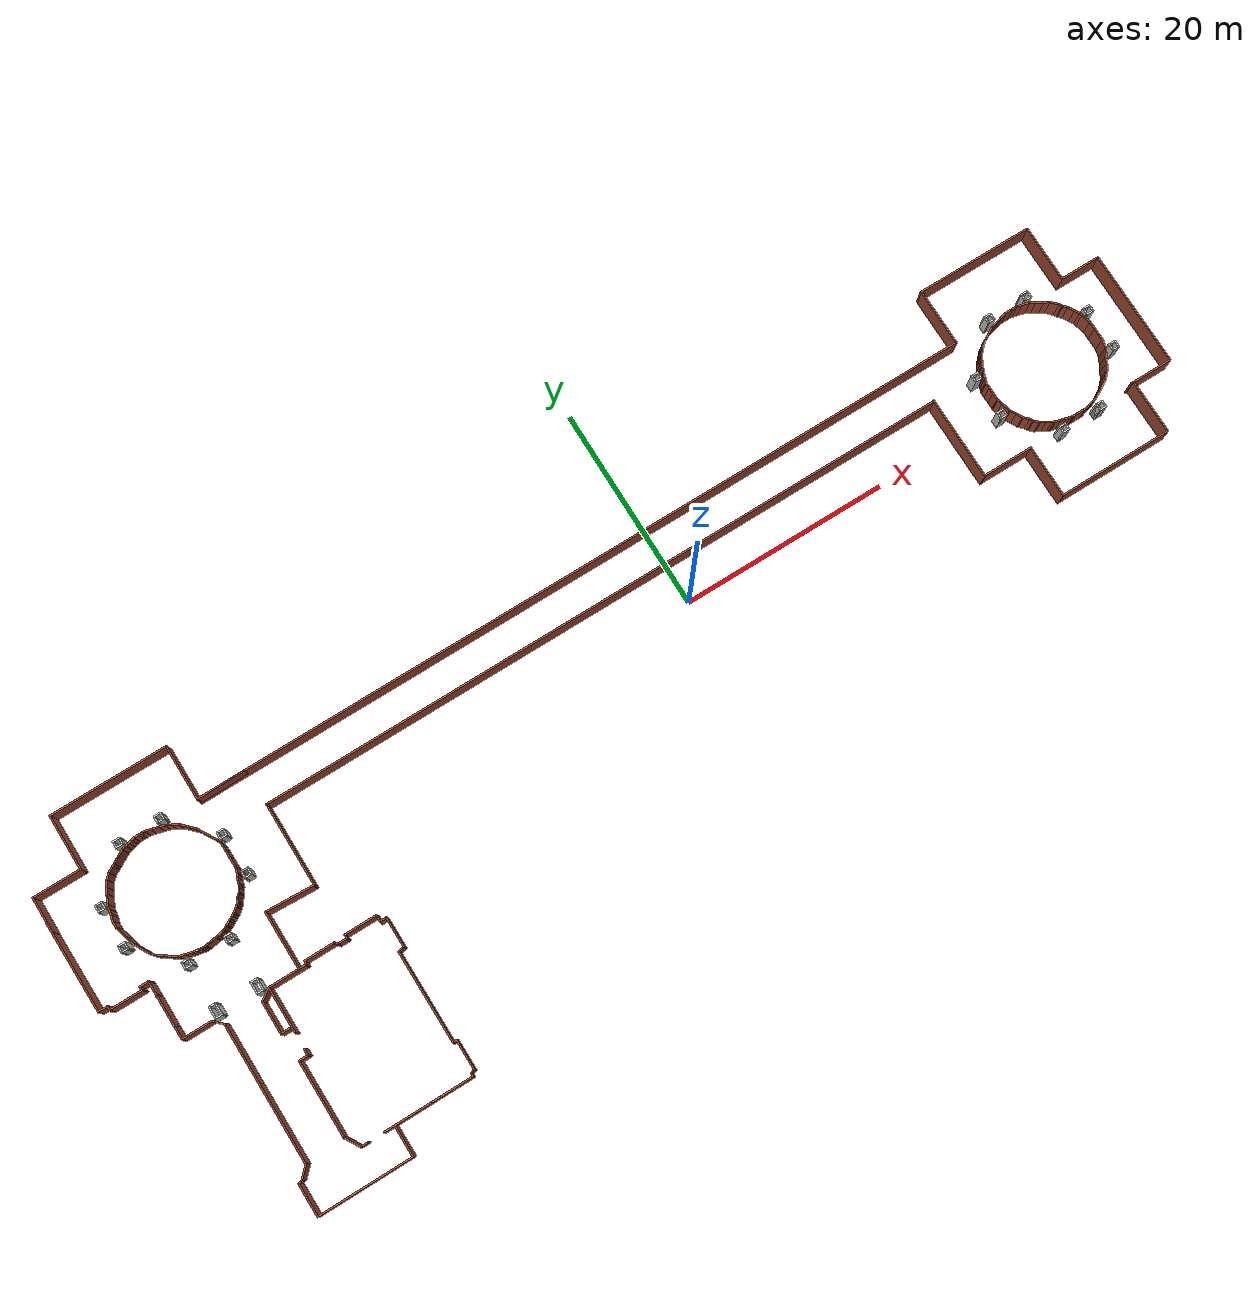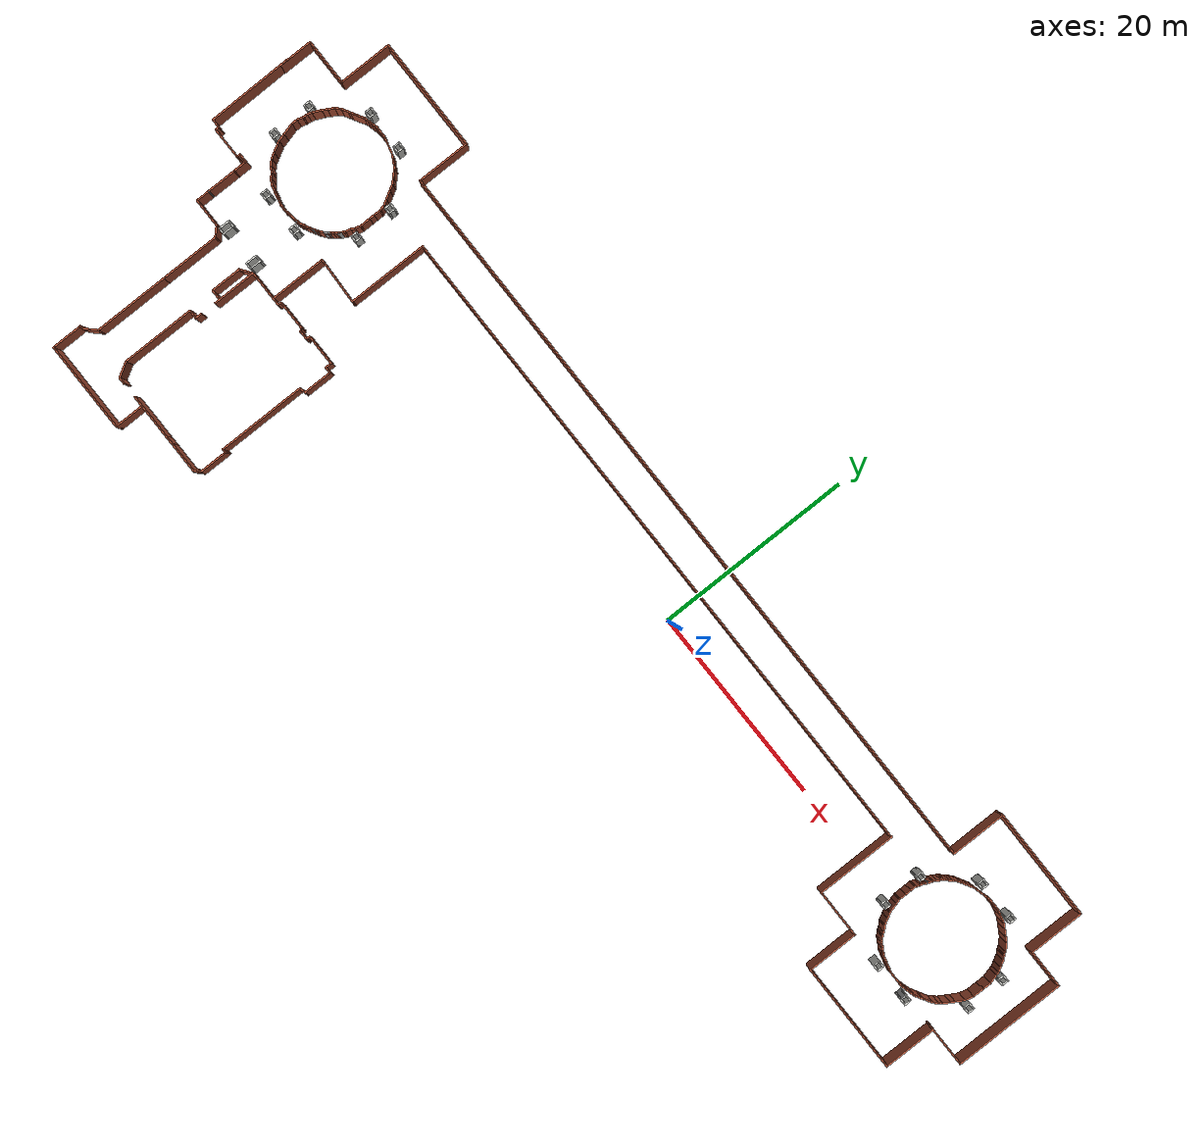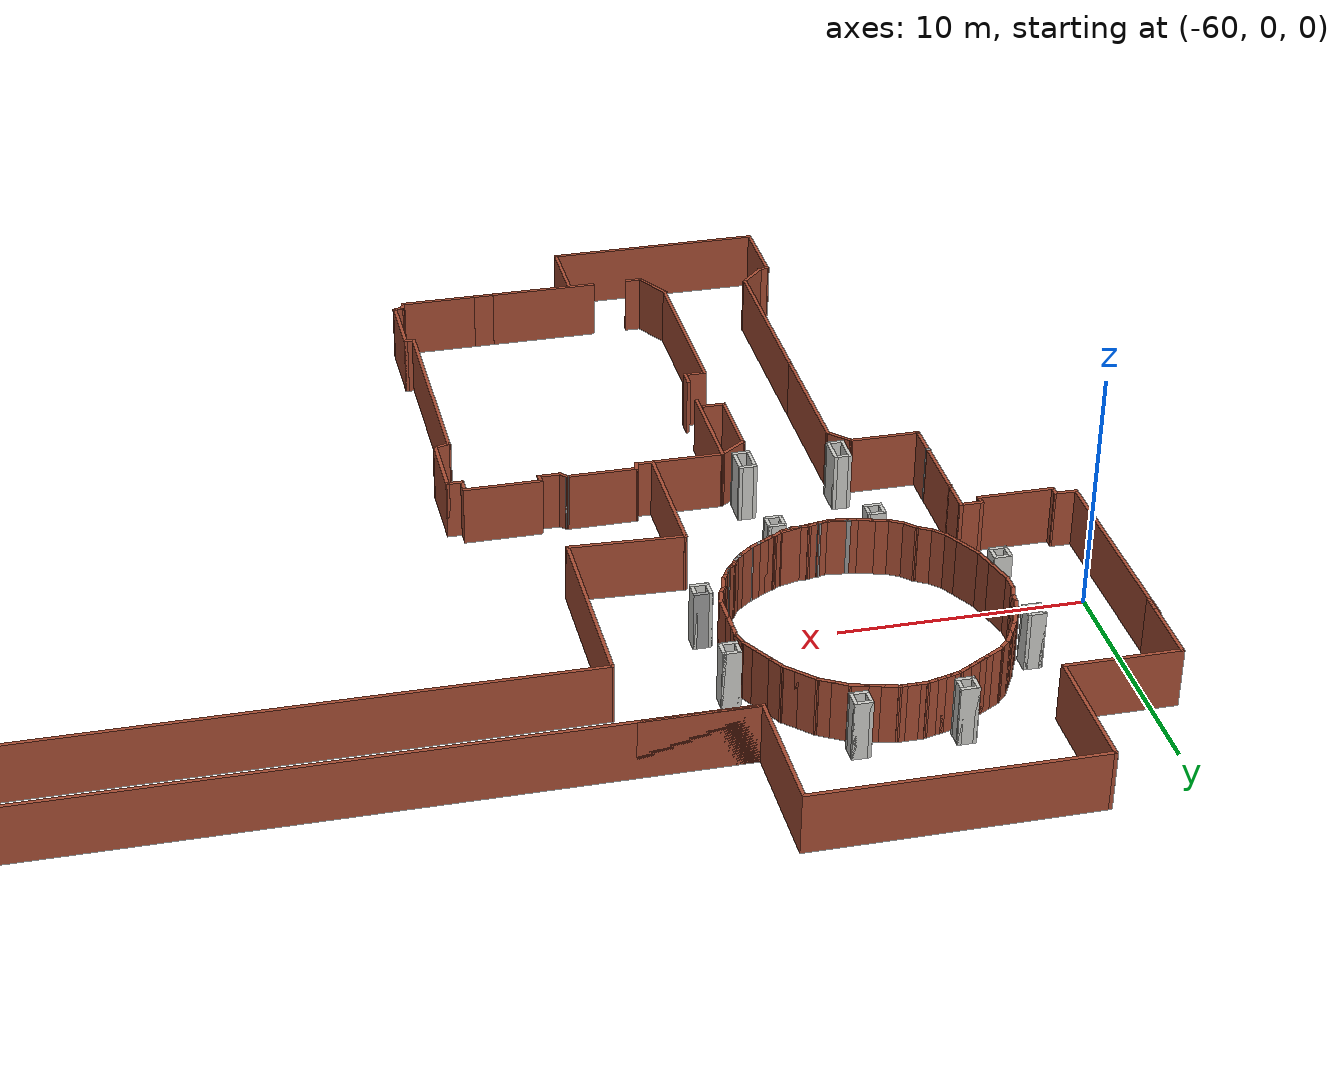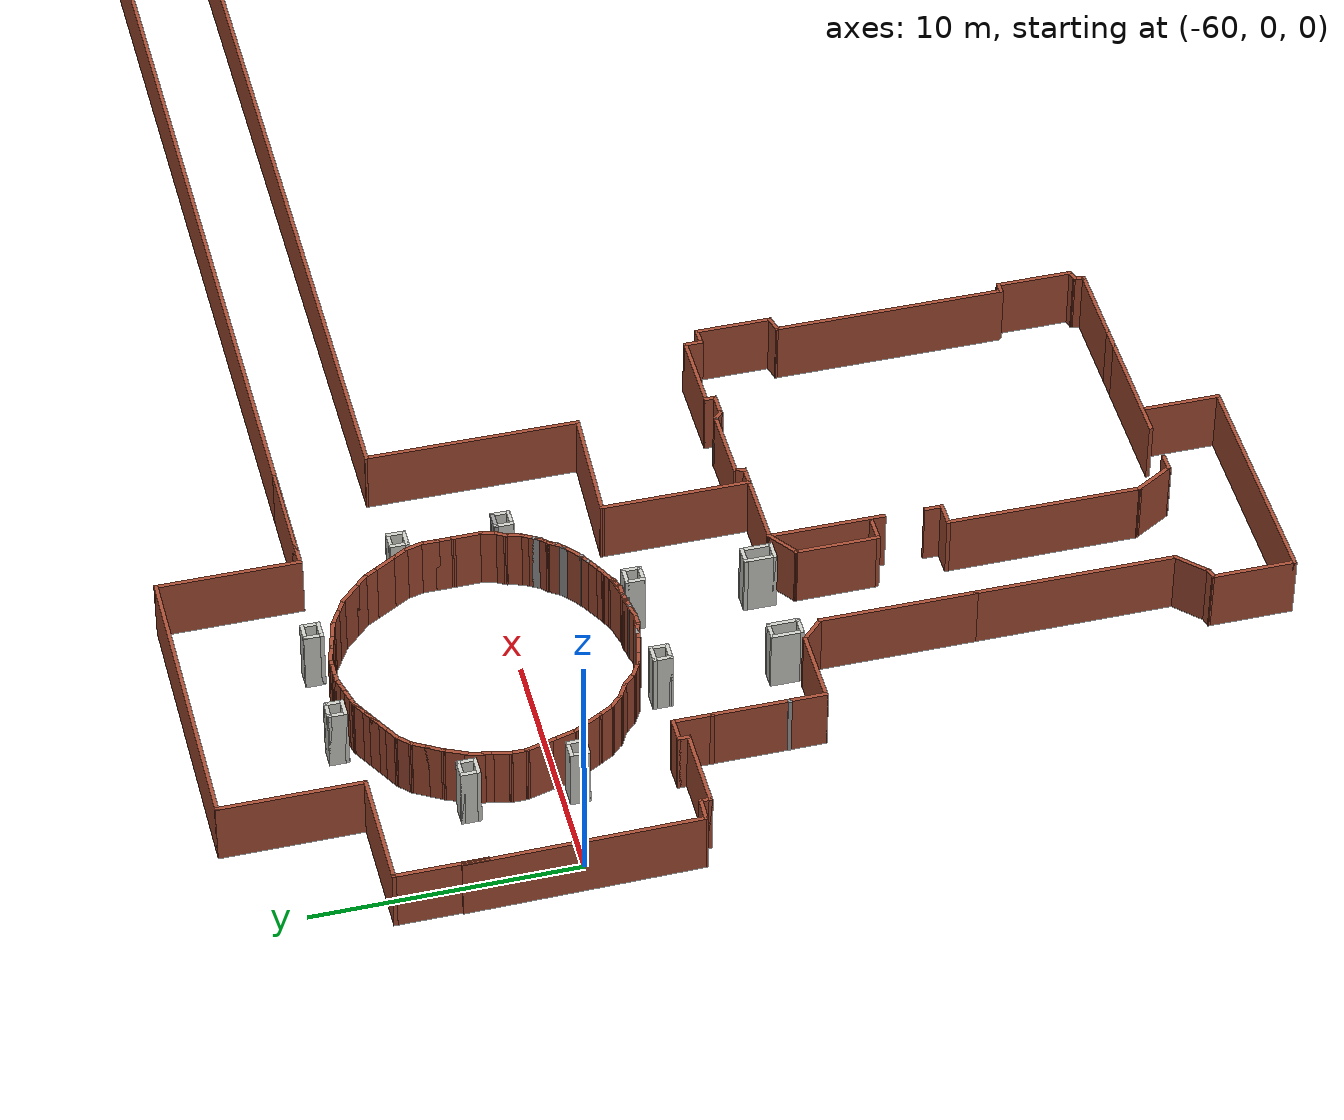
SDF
<?xml version='1.0'?>
<sdf version='1.7'>
  <model name='TD_n1'>
    <pose>-6.73335 -7.75071 0 0 -0 0</pose>
    <link name='Wall_10'>
      <collision name='Wall_10_Collision'>
        <geometry>
          <box>
            <size>0.5 0.15 2.5</size>
          </box>
        </geometry>
        <pose>0 0 1.25 0 -0 0</pose>
      </collision>
      <visual name='Wall_10_Visual'>
        <pose>0 0 1.25 0 -0 0</pose>
        <geometry>
          <box>
            <size>0.5 0.15 2.5</size>
          </box>
        </geometry>
        <material>
          <script>
            <uri>file://media/materials/scripts/gazebo.material</uri>
            <name>Gazebo/Bricks</name>
          </script>
          <ambient>1 1 1 1</ambient>
        </material>
        <meta>
          <layer>0</layer>
        </meta>
      </visual>
      <pose>-33.5245 -1.89044 0 0 -0 1.5708</pose>
    </link>
    <link name='Wall_100'>
      <collision name='Wall_100_Collision'>
        <geometry>
          <box>
            <size>0.25 0.15 2.5</size>
          </box>
        </geometry>
        <pose>0 0 1.25 0 -0 0</pose>
      </collision>
      <visual name='Wall_100_Visual'>
        <pose>0 0 1.25 0 -0 0</pose>
        <geometry>
          <box>
            <size>0.25 0.15 2.5</size>
          </box>
        </geometry>
        <material>
          <script>
            <uri>file://media/materials/scripts/gazebo.material</uri>
            <name>Gazebo/Grey</name>
          </script>
          <ambient>1 1 1 1</ambient>
        </material>
        <meta>
          <layer>0</layer>
        </meta>
      </visual>
      <pose>-39.7639 5.45965 0 0 -0 -2.35619</pose>
    </link>
    <link name='Wall_101'>
      <collision name='Wall_101_Collision'>
        <geometry>
          <box>
            <size>0.5 0.15 2.5</size>
          </box>
        </geometry>
        <pose>0 0 1.25 0 -0 0</pose>
      </collision>
      <visual name='Wall_101_Visual'>
        <pose>0 0 1.25 0 -0 0</pose>
        <geometry>
          <box>
            <size>0.5 0.15 2.5</size>
          </box>
        </geometry>
        <material>
          <script>
            <uri>file://media/materials/scripts/gazebo.material</uri>
            <name>Gazebo/Grey</name>
          </script>
          <ambient>1 1 1 1</ambient>
        </material>
        <meta>
          <layer>0</layer>
        </meta>
      </visual>
      <pose>-39.923 5.30056 0 0 -0 -2.35619</pose>
    </link>
    <link name='Wall_103'>
      <collision name='Wall_103_Collision'>
        <geometry>
          <box>
            <size>0.25 0.15 2.5</size>
          </box>
        </geometry>
        <pose>0 0 1.25 0 -0 0</pose>
      </collision>
      <visual name='Wall_103_Visual'>
        <pose>0 0 1.25 0 -0 0</pose>
        <geometry>
          <box>
            <size>0.25 0.15 2.5</size>
          </box>
        </geometry>
        <material>
          <script>
            <uri>file://media/materials/scripts/gazebo.material</uri>
            <name>Gazebo/Bricks</name>
          </script>
          <ambient>1 1 1 1</ambient>
        </material>
        <meta>
          <layer>0</layer>
        </meta>
      </visual>
      <pose>-41.9705 3.97081 0 0 -0 0.785398</pose>
    </link>
    <link name='Wall_104'>
      <collision name='Wall_104_Collision'>
        <geometry>
          <box>
            <size>0.5 0.15 2.5</size>
          </box>
        </geometry>
        <pose>0 0 1.25 0 -0 0</pose>
      </collision>
      <visual name='Wall_104_Visual'>
        <pose>0 0 1.25 0 -0 0</pose>
        <geometry>
          <box>
            <size>0.5 0.15 2.5</size>
          </box>
        </geometry>
        <material>
          <script>
            <uri>file://media/materials/scripts/gazebo.material</uri>
            <name>Gazebo/Bricks</name>
          </script>
          <ambient>1 1 1 1</ambient>
        </material>
        <meta>
          <layer>0</layer>
        </meta>
      </visual>
      <pose>-41.7836 4.09367 0 0 -0 0.523599</pose>
    </link>
    <link name='Wall_105'>
      <collision name='Wall_105_Collision'>
        <geometry>
          <box>
            <size>0.25 0.15 2.5</size>
          </box>
        </geometry>
        <pose>0 0 1.25 0 -0 0</pose>
      </collision>
      <visual name='Wall_105_Visual'>
        <pose>0 0 1.25 0 -0 0</pose>
        <geometry>
          <box>
            <size>0.25 0.15 2.5</size>
          </box>
        </geometry>
        <material>
          <script>
            <uri>file://media/materials/scripts/gazebo.material</uri>
            <name>Gazebo/Bricks</name>
          </script>
          <ambient>1 1 1 1</ambient>
        </material>
        <meta>
          <layer>0</layer>
        </meta>
      </visual>
      <pose>-41.5837 4.19411 0 0 -0 0.261799</pose>
    </link>
    <link name='Wall_106'>
      <collision name='Wall_106_Collision'>
        <geometry>
          <box>
            <size>0.5 0.15 2.5</size>
          </box>
        </geometry>
        <pose>0 0 1.25 0 -0 0</pose>
      </collision>
      <visual name='Wall_106_Visual'>
        <pose>0 0 1.25 0 -0 0</pose>
        <geometry>
          <box>
            <size>0.5 0.15 2.5</size>
          </box>
        </geometry>
        <material>
          <script>
            <uri>file://media/materials/scripts/gazebo.material</uri>
            <name>Gazebo/Bricks</name>
          </script>
          <ambient>1 1 1 1</ambient>
        </material>
        <meta>
          <layer>0</layer>
        </meta>
      </visual>
      <pose>-41.3839 4.29455 0 0 -0 0.523599</pose>
    </link>
    <link name='Wall_107'>
      <collision name='Wall_107_Collision'>
        <geometry>
          <box>
            <size>0.5 0.15 2.5</size>
          </box>
        </geometry>
        <pose>0 0 1.25 0 -0 0</pose>
      </collision>
      <visual name='Wall_107_Visual'>
        <pose>0 0 1.25 0 -0 0</pose>
        <geometry>
          <box>
            <size>0.5 0.15 2.5</size>
          </box>
        </geometry>
        <material>
          <script>
            <uri>file://media/materials/scripts/gazebo.material</uri>
            <name>Gazebo/Bricks</name>
          </script>
          <ambient>1 1 1 1</ambient>
        </material>
        <meta>
          <layer>0</layer>
        </meta>
      </visual>
      <pose>-41.0808 4.46955 0 0 -0 0.523599</pose>
    </link>
    <link name='Wall_108'>
      <collision name='Wall_108_Collision'>
        <geometry>
          <box>
            <size>0.25 0.15 2.5</size>
          </box>
        </geometry>
        <pose>0 0 1.25 0 -0 0</pose>
      </collision>
      <visual name='Wall_108_Visual'>
        <pose>0 0 1.25 0 -0 0</pose>
        <geometry>
          <box>
            <size>0.25 0.15 2.5</size>
          </box>
        </geometry>
        <material>
          <script>
            <uri>file://media/materials/scripts/gazebo.material</uri>
            <name>Gazebo/Grey</name>
          </script>
          <ambient>1 1 1 1</ambient>
        </material>
        <meta>
          <layer>0</layer>
        </meta>
      </visual>
      <pose>-40.8859 4.58205 0 0 -0 0.523599</pose>
    </link>
    <link name='Wall_109'>
      <collision name='Wall_109_Collision'>
        <geometry>
          <box>
            <size>0.5 0.15 2.5</size>
          </box>
        </geometry>
        <pose>0 0 1.25 0 -0 0</pose>
      </collision>
      <visual name='Wall_109_Visual'>
        <pose>0 0 1.25 0 -0 0</pose>
        <geometry>
          <box>
            <size>0.5 0.15 2.5</size>
          </box>
        </geometry>
        <material>
          <script>
            <uri>file://media/materials/scripts/gazebo.material</uri>
            <name>Gazebo/Bricks</name>
          </script>
          <ambient>1 1 1 1</ambient>
        </material>
        <meta>
          <layer>0</layer>
        </meta>
      </visual>
      <pose>-40.6911 4.69455 0 0 -0 0.523599</pose>
    </link>
    <link name='Wall_11'>
      <collision name='Wall_11_Collision'>
        <geometry>
          <box>
            <size>3.25 0.15 2.5</size>
          </box>
        </geometry>
        <pose>0 0 1.25 0 -0 0</pose>
      </collision>
      <visual name='Wall_11_Visual'>
        <pose>0 0 1.25 0 -0 0</pose>
        <geometry>
          <box>
            <size>3.25 0.15 2.5</size>
          </box>
        </geometry>
        <material>
          <script>
            <uri>file://media/materials/scripts/gazebo.material</uri>
            <name>Gazebo/Bricks</name>
          </script>
          <ambient>1 1 1 1</ambient>
        </material>
        <meta>
          <layer>0</layer>
        </meta>
      </visual>
      <pose>-31.9745 -1.71544 0 0 -0 0</pose>
    </link>
    <link name='Wall_110'>
      <collision name='Wall_110_Collision'>
        <geometry>
          <box>
            <size>0.15 0.15 2.5</size>
          </box>
        </geometry>
        <pose>0 0 1.25 0 -0 0</pose>
      </collision>
      <visual name='Wall_110_Visual'>
        <pose>0 0 1.25 0 -0 0</pose>
        <geometry>
          <box>
            <size>0.15 0.15 2.5</size>
          </box>
        </geometry>
        <material>
          <script>
            <uri>file://media/materials/scripts/gazebo.material</uri>
            <name>Gazebo/Grey</name>
          </script>
          <ambient>1 1 1 1</ambient>
        </material>
        <meta>
          <layer>0</layer>
        </meta>
      </visual>
      <pose>-40.5395 4.78205 0 0 -0 0</pose>
    </link>
    <link name='Wall_111'>
      <collision name='Wall_111_Collision'>
        <geometry>
          <box>
            <size>0.781405 0.15 2.5</size>
          </box>
        </geometry>
        <pose>0 0 1.25 0 -0 0</pose>
      </collision>
      <visual name='Wall_111_Visual'>
        <pose>0 0 1.25 0 -0 0</pose>
        <geometry>
          <box>
            <size>0.781405 0.15 2.5</size>
          </box>
        </geometry>
        <material>
          <script>
            <uri>file://media/materials/scripts/gazebo.material</uri>
            <name>Gazebo/Bricks</name>
          </script>
          <ambient>1 1 1 1</ambient>
        </material>
        <meta>
          <layer>0</layer>
        </meta>
      </visual>
      <pose>-40.2931 4.97943 0 0 -0 0.675405</pose>
    </link>
    <link name='Wall_112'>
      <collision name='Wall_112_Collision'>
        <geometry>
          <box>
            <size>0.5 0.15 2.5</size>
          </box>
        </geometry>
        <pose>0 0 1.25 0 -0 0</pose>
      </collision>
      <visual name='Wall_112_Visual'>
        <pose>0 0 1.25 0 -0 0</pose>
        <geometry>
          <box>
            <size>0.5 0.15 2.5</size>
          </box>
        </geometry>
        <material>
          <script>
            <uri>file://media/materials/scripts/gazebo.material</uri>
            <name>Gazebo/Bricks</name>
          </script>
          <ambient>1 1 1 1</ambient>
        </material>
        <meta>
          <layer>0</layer>
        </meta>
      </visual>
      <pose>-39.923 5.30056 0 0 -0 0.785398</pose>
    </link>
    <link name='Wall_113'>
      <collision name='Wall_113_Collision'>
        <geometry>
          <box>
            <size>0.597342 0.15 2.5</size>
          </box>
        </geometry>
        <pose>0 0 1.25 0 -0 0</pose>
      </collision>
      <visual name='Wall_113_Visual'>
        <pose>0 0 1.25 0 -0 0</pose>
        <geometry>
          <box>
            <size>0.597342 0.15 2.5</size>
          </box>
        </geometry>
        <material>
          <script>
            <uri>file://media/materials/scripts/gazebo.material</uri>
            <name>Gazebo/Bricks</name>
          </script>
          <ambient>1 1 1 1</ambient>
        </material>
        <meta>
          <layer>0</layer>
        </meta>
      </visual>
      <pose>-39.6764 5.61121 0 0 -0 0.989308</pose>
    </link>
    <link name='Wall_114'>
      <collision name='Wall_114_Collision'>
        <geometry>
          <box>
            <size>0.5 0.15 2.5</size>
          </box>
        </geometry>
        <pose>0 0 1.25 0 -0 0</pose>
      </collision>
      <visual name='Wall_114_Visual'>
        <pose>0 0 1.25 0 -0 0</pose>
        <geometry>
          <box>
            <size>0.5 0.15 2.5</size>
          </box>
        </geometry>
        <material>
          <script>
            <uri>file://media/materials/scripts/gazebo.material</uri>
            <name>Gazebo/Bricks</name>
          </script>
          <ambient>1 1 1 1</ambient>
        </material>
        <meta>
          <layer>0</layer>
        </meta>
      </visual>
      <pose>-39.4298 5.92186 0 0 -0 0.785398</pose>
    </link>
    <link name='Wall_115'>
      <collision name='Wall_115_Collision'>
        <geometry>
          <box>
            <size>0.5 0.15 2.5</size>
          </box>
        </geometry>
        <pose>0 0 1.25 0 -0 0</pose>
      </collision>
      <visual name='Wall_115_Visual'>
        <pose>0 0 1.25 0 -0 0</pose>
        <geometry>
          <box>
            <size>0.5 0.15 2.5</size>
          </box>
        </geometry>
        <material>
          <script>
            <uri>file://media/materials/scripts/gazebo.material</uri>
            <name>Gazebo/Bricks</name>
          </script>
          <ambient>1 1 1 1</ambient>
        </material>
        <meta>
          <layer>0</layer>
        </meta>
      </visual>
      <pose>-39.2185 6.19716 0 0 -0 1.0472</pose>
    </link>
    <link name='Wall_116'>
      <collision name='Wall_116_Collision'>
        <geometry>
          <box>
            <size>0.5 0.15 2.5</size>
          </box>
        </geometry>
        <pose>0 0 1.25 0 -0 0</pose>
      </collision>
      <visual name='Wall_116_Visual'>
        <pose>0 0 1.25 0 -0 0</pose>
        <geometry>
          <box>
            <size>0.5 0.15 2.5</size>
          </box>
        </geometry>
        <material>
          <script>
            <uri>file://media/materials/scripts/gazebo.material</uri>
            <name>Gazebo/Bricks</name>
          </script>
          <ambient>1 1 1 1</ambient>
        </material>
        <meta>
          <layer>0</layer>
        </meta>
      </visual>
      <pose>-39.0435 6.50027 0 0 -0 1.0472</pose>
    </link>
    <link name='Wall_117'>
      <collision name='Wall_117_Collision'>
        <geometry>
          <box>
            <size>0.75 0.15 2.5</size>
          </box>
        </geometry>
        <pose>0 0 1.25 0 -0 0</pose>
      </collision>
      <visual name='Wall_117_Visual'>
        <pose>0 0 1.25 0 -0 0</pose>
        <geometry>
          <box>
            <size>0.75 0.15 2.5</size>
          </box>
        </geometry>
        <material>
          <script>
            <uri>file://media/materials/scripts/gazebo.material</uri>
            <name>Gazebo/Bricks</name>
          </script>
          <ambient>1 1 1 1</ambient>
        </material>
        <meta>
          <layer>0</layer>
        </meta>
      </visual>
      <pose>-38.8784 6.9416 0 0 -0 1.309</pose>
    </link>
    <link name='Wall_118'>
      <collision name='Wall_118_Collision'>
        <geometry>
          <box>
            <size>0.5 0.15 2.5</size>
          </box>
        </geometry>
        <pose>0 0 1.25 0 -0 0</pose>
      </collision>
      <visual name='Wall_118_Visual'>
        <pose>0 0 1.25 0 -0 0</pose>
        <geometry>
          <box>
            <size>0.5 0.15 2.5</size>
          </box>
        </geometry>
        <material>
          <script>
            <uri>file://media/materials/scripts/gazebo.material</uri>
            <name>Gazebo/Bricks</name>
          </script>
          <ambient>1 1 1 1</ambient>
        </material>
        <meta>
          <layer>0</layer>
        </meta>
      </visual>
      <pose>-38.7132 7.38293 0 0 -0 1.0472</pose>
    </link>
    <link name='Wall_119'>
      <collision name='Wall_119_Collision'>
        <geometry>
          <box>
            <size>0.75 0.15 2.5</size>
          </box>
        </geometry>
        <pose>0 0 1.25 0 -0 0</pose>
      </collision>
      <visual name='Wall_119_Visual'>
        <pose>0 0 1.25 0 -0 0</pose>
        <geometry>
          <box>
            <size>0.75 0.15 2.5</size>
          </box>
        </geometry>
        <material>
          <script>
            <uri>file://media/materials/scripts/gazebo.material</uri>
            <name>Gazebo/Bricks</name>
          </script>
          <ambient>1 1 1 1</ambient>
        </material>
        <meta>
          <layer>0</layer>
        </meta>
      </visual>
      <pose>-38.5481 7.82426 0 0 -0 1.309</pose>
    </link>
    <link name='Wall_12'>
      <collision name='Wall_12_Collision'>
        <geometry>
          <box>
            <size>0.75 0.15 2.5</size>
          </box>
        </geometry>
        <pose>0 0 1.25 0 -0 0</pose>
      </collision>
      <visual name='Wall_12_Visual'>
        <pose>0 0 1.25 0 -0 0</pose>
        <geometry>
          <box>
            <size>0.75 0.15 2.5</size>
          </box>
        </geometry>
        <material>
          <script>
            <uri>file://media/materials/scripts/gazebo.material</uri>
            <name>Gazebo/Bricks</name>
          </script>
          <ambient>1 1 1 1</ambient>
        </material>
        <meta>
          <layer>0</layer>
        </meta>
      </visual>
      <pose>-30.4245 -2.01544 0 0 -0 -1.5708</pose>
    </link>
    <link name='Wall_121'>
      <collision name='Wall_121_Collision'>
        <geometry>
          <box>
            <size>0.5 0.15 2.5</size>
          </box>
        </geometry>
        <pose>0 0 1.25 0 -0 0</pose>
      </collision>
      <visual name='Wall_121_Visual'>
        <pose>0 0 1.25 0 -0 0</pose>
        <geometry>
          <box>
            <size>0.5 0.15 2.5</size>
          </box>
        </geometry>
        <material>
          <script>
            <uri>file://media/materials/scripts/gazebo.material</uri>
            <name>Gazebo/Bricks</name>
          </script>
          <ambient>1 1 1 1</ambient>
        </material>
        <meta>
          <layer>0</layer>
        </meta>
      </visual>
      <pose>-43.6377 14.7863 0 0 -0 0</pose>
    </link>
    <link name='Wall_122'>
      <collision name='Wall_122_Collision'>
        <geometry>
          <box>
            <size>0.75 0.15 2.5</size>
          </box>
        </geometry>
        <pose>0 0 1.25 0 -0 0</pose>
      </collision>
      <visual name='Wall_122_Visual'>
        <pose>0 0 1.25 0 -0 0</pose>
        <geometry>
          <box>
            <size>0.75 0.15 2.5</size>
          </box>
        </geometry>
        <material>
          <script>
            <uri>file://media/materials/scripts/gazebo.material</uri>
            <name>Gazebo/Bricks</name>
          </script>
          <ambient>1 1 1 1</ambient>
        </material>
        <meta>
          <layer>0</layer>
        </meta>
      </visual>
      <pose>-43.1729 14.7086 0 0 -0 -0.261799</pose>
    </link>
    <link name='Wall_123'>
      <collision name='Wall_123_Collision'>
        <geometry>
          <box>
            <size>0.75 0.15 2.5</size>
          </box>
        </geometry>
        <pose>0 0 1.25 0 -0 0</pose>
      </collision>
      <visual name='Wall_123_Visual'>
        <pose>0 0 1.25 0 -0 0</pose>
        <geometry>
          <box>
            <size>0.75 0.15 2.5</size>
          </box>
        </geometry>
        <material>
          <script>
            <uri>file://media/materials/scripts/gazebo.material</uri>
            <name>Gazebo/Bricks</name>
          </script>
          <ambient>1 1 1 1</ambient>
        </material>
        <meta>
          <layer>0</layer>
        </meta>
      </visual>
      <pose>-42.5934 14.5533 0 0 -0 -0.261799</pose>
    </link>
    <link name='Wall_124'>
      <collision name='Wall_124_Collision'>
        <geometry>
          <box>
            <size>0.75 0.15 2.5</size>
          </box>
        </geometry>
        <pose>0 0 1.25 0 -0 0</pose>
      </collision>
      <visual name='Wall_124_Visual'>
        <pose>0 0 1.25 0 -0 0</pose>
        <geometry>
          <box>
            <size>0.75 0.15 2.5</size>
          </box>
        </geometry>
        <material>
          <script>
            <uri>file://media/materials/scripts/gazebo.material</uri>
            <name>Gazebo/Bricks</name>
          </script>
          <ambient>1 1 1 1</ambient>
        </material>
        <meta>
          <layer>0</layer>
        </meta>
      </visual>
      <pose>-42.0138 14.398 0 0 -0 -0.261799</pose>
    </link>
    <link name='Wall_125'>
      <collision name='Wall_125_Collision'>
        <geometry>
          <box>
            <size>0.75 0.15 2.5</size>
          </box>
        </geometry>
        <pose>0 0 1.25 0 -0 0</pose>
      </collision>
      <visual name='Wall_125_Visual'>
        <pose>0 0 1.25 0 -0 0</pose>
        <geometry>
          <box>
            <size>0.75 0.15 2.5</size>
          </box>
        </geometry>
        <material>
          <script>
            <uri>file://media/materials/scripts/gazebo.material</uri>
            <name>Gazebo/Bricks</name>
          </script>
          <ambient>1 1 1 1</ambient>
        </material>
        <meta>
          <layer>0</layer>
        </meta>
      </visual>
      <pose>-41.4642 14.1704 0 0 -0 -0.523599</pose>
    </link>
    <link name='Wall_126'>
      <collision name='Wall_126_Collision'>
        <geometry>
          <box>
            <size>0.75 0.15 2.5</size>
          </box>
        </geometry>
        <pose>0 0 1.25 0 -0 0</pose>
      </collision>
      <visual name='Wall_126_Visual'>
        <pose>0 0 1.25 0 -0 0</pose>
        <geometry>
          <box>
            <size>0.75 0.15 2.5</size>
          </box>
        </geometry>
        <material>
          <script>
            <uri>file://media/materials/scripts/gazebo.material</uri>
            <name>Gazebo/Bricks</name>
          </script>
          <ambient>1 1 1 1</ambient>
        </material>
        <meta>
          <layer>0</layer>
        </meta>
      </visual>
      <pose>-40.9446 13.8704 0 0 -0 -0.523599</pose>
    </link>
    <link name='Wall_127'>
      <collision name='Wall_127_Collision'>
        <geometry>
          <box>
            <size>1 0.15 2.5</size>
          </box>
        </geometry>
        <pose>0 0 1.25 0 -0 0</pose>
      </collision>
      <visual name='Wall_127_Visual'>
        <pose>0 0 1.25 0 -0 0</pose>
        <geometry>
          <box>
            <size>1 0.15 2.5</size>
          </box>
        </geometry>
        <material>
          <script>
            <uri>file://media/materials/scripts/gazebo.material</uri>
            <name>Gazebo/Bricks</name>
          </script>
          <ambient>1 1 1 1</ambient>
        </material>
        <meta>
          <layer>0</layer>
        </meta>
      </visual>
      <pose>-40.3843 13.4199 0 0 -0 -0.785398</pose>
    </link>
    <link name='Wall_128'>
      <collision name='Wall_128_Collision'>
        <geometry>
          <box>
            <size>0.75 0.15 2.5</size>
          </box>
        </geometry>
        <pose>0 0 1.25 0 -0 0</pose>
      </collision>
      <visual name='Wall_128_Visual'>
        <pose>0 0 1.25 0 -0 0</pose>
        <geometry>
          <box>
            <size>0.75 0.15 2.5</size>
          </box>
        </geometry>
        <material>
          <script>
            <uri>file://media/materials/scripts/gazebo.material</uri>
            <name>Gazebo/Bricks</name>
          </script>
          <ambient>1 1 1 1</ambient>
        </material>
        <meta>
          <layer>0</layer>
        </meta>
      </visual>
      <pose>-39.8716 12.9072 0 0 -0 -0.785398</pose>
    </link>
    <link name='Wall_129'>
      <collision name='Wall_129_Collision'>
        <geometry>
          <box>
            <size>0.75 0.15 2.5</size>
          </box>
        </geometry>
        <pose>0 0 1.25 0 -0 0</pose>
      </collision>
      <visual name='Wall_129_Visual'>
        <pose>0 0 1.25 0 -0 0</pose>
        <geometry>
          <box>
            <size>0.75 0.15 2.5</size>
          </box>
        </geometry>
        <material>
          <script>
            <uri>file://media/materials/scripts/gazebo.material</uri>
            <name>Gazebo/Bricks</name>
          </script>
          <ambient>1 1 1 1</ambient>
        </material>
        <meta>
          <layer>0</layer>
        </meta>
      </visual>
      <pose>-39.5095 12.4353 0 0 -0 -1.0472</pose>
    </link>
    <link name='Wall_13'>
      <collision name='Wall_13_Collision'>
        <geometry>
          <box>
            <size>0.75 0.15 2.5</size>
          </box>
        </geometry>
        <pose>0 0 1.25 0 -0 0</pose>
      </collision>
      <visual name='Wall_13_Visual'>
        <pose>0 0 1.25 0 -0 0</pose>
        <geometry>
          <box>
            <size>0.75 0.15 2.5</size>
          </box>
        </geometry>
        <material>
          <script>
            <uri>file://media/materials/scripts/gazebo.material</uri>
            <name>Gazebo/Bricks</name>
          </script>
          <ambient>1 1 1 1</ambient>
        </material>
        <meta>
          <layer>0</layer>
        </meta>
      </visual>
      <pose>-30.1245 -2.31544 0 0 -0 0</pose>
    </link>
    <link name='Wall_130'>
      <collision name='Wall_130_Collision'>
        <geometry>
          <box>
            <size>1 0.15 2.5</size>
          </box>
        </geometry>
        <pose>0 0 1.25 0 -0 0</pose>
      </collision>
      <visual name='Wall_130_Visual'>
        <pose>0 0 1.25 0 -0 0</pose>
        <geometry>
          <box>
            <size>1 0.15 2.5</size>
          </box>
        </geometry>
        <material>
          <script>
            <uri>file://media/materials/scripts/gazebo.material</uri>
            <name>Gazebo/Bricks</name>
          </script>
          <ambient>1 1 1 1</ambient>
        </material>
        <meta>
          <layer>0</layer>
        </meta>
      </visual>
      <pose>-39.147 11.8074 0 0 -0 -1.0472</pose>
    </link>
    <link name='Wall_131'>
      <collision name='Wall_131_Collision'>
        <geometry>
          <box>
            <size>0.75 0.15 2.5</size>
          </box>
        </geometry>
        <pose>0 0 1.25 0 -0 0</pose>
      </collision>
      <visual name='Wall_131_Visual'>
        <pose>0 0 1.25 0 -0 0</pose>
        <geometry>
          <box>
            <size>0.75 0.15 2.5</size>
          </box>
        </geometry>
        <material>
          <script>
            <uri>file://media/materials/scripts/gazebo.material</uri>
            <name>Gazebo/Bricks</name>
          </script>
          <ambient>1 1 1 1</ambient>
        </material>
        <meta>
          <layer>0</layer>
        </meta>
      </visual>
      <pose>-38.7845 11.1795 0 0 -0 -1.0472</pose>
    </link>
    <link name='Wall_132'>
      <collision name='Wall_132_Collision'>
        <geometry>
          <box>
            <size>0.75 0.15 2.5</size>
          </box>
        </geometry>
        <pose>0 0 1.25 0 -0 0</pose>
      </collision>
      <visual name='Wall_132_Visual'>
        <pose>0 0 1.25 0 -0 0</pose>
        <geometry>
          <box>
            <size>0.75 0.15 2.5</size>
          </box>
        </geometry>
        <material>
          <script>
            <uri>file://media/materials/scripts/gazebo.material</uri>
            <name>Gazebo/Bricks</name>
          </script>
          <ambient>1 1 1 1</ambient>
        </material>
        <meta>
          <layer>0</layer>
        </meta>
      </visual>
      <pose>-38.5568 10.63 0 0 -0 -1.309</pose>
    </link>
    <link name='Wall_133'>
      <collision name='Wall_133_Collision'>
        <geometry>
          <box>
            <size>0.75 0.15 2.5</size>
          </box>
        </geometry>
        <pose>0 0 1.25 0 -0 0</pose>
      </collision>
      <visual name='Wall_133_Visual'>
        <pose>0 0 1.25 0 -0 0</pose>
        <geometry>
          <box>
            <size>0.75 0.15 2.5</size>
          </box>
        </geometry>
        <material>
          <script>
            <uri>file://media/materials/scripts/gazebo.material</uri>
            <name>Gazebo/Bricks</name>
          </script>
          <ambient>1 1 1 1</ambient>
        </material>
        <meta>
          <layer>0</layer>
        </meta>
      </visual>
      <pose>-38.4792 10.0402 0 0 -0 -1.5708</pose>
    </link>
    <link name='Wall_134'>
      <collision name='Wall_134_Collision'>
        <geometry>
          <box>
            <size>0.75 0.15 2.5</size>
          </box>
        </geometry>
        <pose>0 0 1.25 0 -0 0</pose>
      </collision>
      <visual name='Wall_134_Visual'>
        <pose>0 0 1.25 0 -0 0</pose>
        <geometry>
          <box>
            <size>0.75 0.15 2.5</size>
          </box>
        </geometry>
        <material>
          <script>
            <uri>file://media/materials/scripts/gazebo.material</uri>
            <name>Gazebo/Bricks</name>
          </script>
          <ambient>1 1 1 1</ambient>
        </material>
        <meta>
          <layer>0</layer>
        </meta>
      </visual>
      <pose>-38.4792 9.44018 0 0 -0 -1.5708</pose>
    </link>
    <link name='Wall_135'>
      <collision name='Wall_135_Collision'>
        <geometry>
          <box>
            <size>1.17617 0.15 2.5</size>
          </box>
        </geometry>
        <pose>0 0 1.25 0 -0 0</pose>
      </collision>
      <visual name='Wall_135_Visual'>
        <pose>0 0 1.25 0 -0 0</pose>
        <geometry>
          <box>
            <size>1.17617 0.15 2.5</size>
          </box>
        </geometry>
        <material>
          <script>
            <uri>file://media/materials/scripts/gazebo.material</uri>
            <name>Gazebo/Bricks</name>
          </script>
          <ambient>1 1 1 1</ambient>
        </material>
        <meta>
          <layer>0</layer>
        </meta>
      </visual>
      <pose>-38.4748 8.62711 0 0 -0 -1.56228</pose>
    </link>
    <link name='Wall_137'>
      <collision name='Wall_137_Collision'>
        <geometry>
          <box>
            <size>0.5 0.15 2.5</size>
          </box>
        </geometry>
        <pose>0 0 1.25 0 -0 0</pose>
      </collision>
      <visual name='Wall_137_Visual'>
        <pose>0 0 1.25 0 -0 0</pose>
        <geometry>
          <box>
            <size>0.5 0.15 2.5</size>
          </box>
        </geometry>
        <material>
          <script>
            <uri>file://media/materials/scripts/gazebo.material</uri>
            <name>Gazebo/Bricks</name>
          </script>
          <ambient>1 1 1 1</ambient>
        </material>
        <meta>
          <layer>0</layer>
        </meta>
      </visual>
      <pose>-43.9877 14.7863 0 0 -0 3.14159</pose>
    </link>
    <link name='Wall_138'>
      <collision name='Wall_138_Collision'>
        <geometry>
          <box>
            <size>0.5 0.15 2.5</size>
          </box>
        </geometry>
        <pose>0 0 1.25 0 -0 0</pose>
      </collision>
      <visual name='Wall_138_Visual'>
        <pose>0 0 1.25 0 -0 0</pose>
        <geometry>
          <box>
            <size>0.5 0.15 2.5</size>
          </box>
        </geometry>
        <material>
          <script>
            <uri>file://media/materials/scripts/gazebo.material</uri>
            <name>Gazebo/Bricks</name>
          </script>
          <ambient>1 1 1 1</ambient>
        </material>
        <meta>
          <layer>0</layer>
        </meta>
      </visual>
      <pose>-44.3377 14.7863 0 0 -0 3.14159</pose>
    </link>
    <link name='Wall_139'>
      <collision name='Wall_139_Collision'>
        <geometry>
          <box>
            <size>0.5 0.15 2.5</size>
          </box>
        </geometry>
        <pose>0 0 1.25 0 -0 0</pose>
      </collision>
      <visual name='Wall_139_Visual'>
        <pose>0 0 1.25 0 -0 0</pose>
        <geometry>
          <box>
            <size>0.5 0.15 2.5</size>
          </box>
        </geometry>
        <material>
          <script>
            <uri>file://media/materials/scripts/gazebo.material</uri>
            <name>Gazebo/Bricks</name>
          </script>
          <ambient>1 1 1 1</ambient>
        </material>
        <meta>
          <layer>0</layer>
        </meta>
      </visual>
      <pose>-44.6817 14.741 0 0 -0 -2.87979</pose>
    </link>
    <link name='Wall_14'>
      <collision name='Wall_14_Collision'>
        <geometry>
          <box>
            <size>3 0.15 2.5</size>
          </box>
        </geometry>
        <pose>0 0 1.25 0 -0 0</pose>
      </collision>
      <visual name='Wall_14_Visual'>
        <pose>0 0 1.25 0 -0 0</pose>
        <geometry>
          <box>
            <size>3 0.15 2.5</size>
          </box>
        </geometry>
        <material>
          <script>
            <uri>file://media/materials/scripts/gazebo.material</uri>
            <name>Gazebo/Bricks</name>
          </script>
          <ambient>1 1 1 1</ambient>
        </material>
        <meta>
          <layer>0</layer>
        </meta>
      </visual>
      <pose>-29.8245 -3.74044 0 0 -0 -1.5708</pose>
    </link>
    <link name='Wall_140'>
      <collision name='Wall_140_Collision'>
        <geometry>
          <box>
            <size>0.5 0.15 2.5</size>
          </box>
        </geometry>
        <pose>0 0 1.25 0 -0 0</pose>
      </collision>
      <visual name='Wall_140_Visual'>
        <pose>0 0 1.25 0 -0 0</pose>
        <geometry>
          <box>
            <size>0.5 0.15 2.5</size>
          </box>
        </geometry>
        <material>
          <script>
            <uri>file://media/materials/scripts/gazebo.material</uri>
            <name>Gazebo/Bricks</name>
          </script>
          <ambient>1 1 1 1</ambient>
        </material>
        <meta>
          <layer>0</layer>
        </meta>
      </visual>
      <pose>-45.0198 14.6504 0 0 -0 -2.87979</pose>
    </link>
    <link name='Wall_141'>
      <collision name='Wall_141_Collision'>
        <geometry>
          <box>
            <size>0.5 0.15 2.5</size>
          </box>
        </geometry>
        <pose>0 0 1.25 0 -0 0</pose>
      </collision>
      <visual name='Wall_141_Visual'>
        <pose>0 0 1.25 0 -0 0</pose>
        <geometry>
          <box>
            <size>0.5 0.15 2.5</size>
          </box>
        </geometry>
        <material>
          <script>
            <uri>file://media/materials/scripts/gazebo.material</uri>
            <name>Gazebo/Bricks</name>
          </script>
          <ambient>1 1 1 1</ambient>
        </material>
        <meta>
          <layer>0</layer>
        </meta>
      </visual>
      <pose>-45.3579 14.5598 0 0 -0 -2.87979</pose>
    </link>
    <link name='Wall_142'>
      <collision name='Wall_142_Collision'>
        <geometry>
          <box>
            <size>0.5 0.15 2.5</size>
          </box>
        </geometry>
        <pose>0 0 1.25 0 -0 0</pose>
      </collision>
      <visual name='Wall_142_Visual'>
        <pose>0 0 1.25 0 -0 0</pose>
        <geometry>
          <box>
            <size>0.5 0.15 2.5</size>
          </box>
        </geometry>
        <material>
          <script>
            <uri>file://media/materials/scripts/gazebo.material</uri>
            <name>Gazebo/Bricks</name>
          </script>
          <ambient>1 1 1 1</ambient>
        </material>
        <meta>
          <layer>0</layer>
        </meta>
      </visual>
      <pose>-45.6959 14.4692 0 0 -0 -2.87979</pose>
    </link>
    <link name='Wall_143'>
      <collision name='Wall_143_Collision'>
        <geometry>
          <box>
            <size>0.75 0.15 2.5</size>
          </box>
        </geometry>
        <pose>0 0 1.25 0 -0 0</pose>
      </collision>
      <visual name='Wall_143_Visual'>
        <pose>0 0 1.25 0 -0 0</pose>
        <geometry>
          <box>
            <size>0.75 0.15 2.5</size>
          </box>
        </geometry>
        <material>
          <script>
            <uri>file://media/materials/scripts/gazebo.material</uri>
            <name>Gazebo/Bricks</name>
          </script>
          <ambient>1 1 1 1</ambient>
        </material>
        <meta>
          <layer>0</layer>
        </meta>
      </visual>
      <pose>-46.1248 14.2739 0 0 -0 -2.61799</pose>
    </link>
    <link name='Wall_144'>
      <collision name='Wall_144_Collision'>
        <geometry>
          <box>
            <size>0.5 0.15 2.5</size>
          </box>
        </geometry>
        <pose>0 0 1.25 0 -0 0</pose>
      </collision>
      <visual name='Wall_144_Visual'>
        <pose>0 0 1.25 0 -0 0</pose>
        <geometry>
          <box>
            <size>0.5 0.15 2.5</size>
          </box>
        </geometry>
        <material>
          <script>
            <uri>file://media/materials/scripts/gazebo.material</uri>
            <name>Gazebo/Bricks</name>
          </script>
          <ambient>1 1 1 1</ambient>
        </material>
        <meta>
          <layer>0</layer>
        </meta>
      </visual>
      <pose>-46.5362 14.0364 0 0 -0 -2.61799</pose>
    </link>
    <link name='Wall_145'>
      <collision name='Wall_145_Collision'>
        <geometry>
          <box>
            <size>0.5 0.15 2.5</size>
          </box>
        </geometry>
        <pose>0 0 1.25 0 -0 0</pose>
      </collision>
      <visual name='Wall_145_Visual'>
        <pose>0 0 1.25 0 -0 0</pose>
        <geometry>
          <box>
            <size>0.5 0.15 2.5</size>
          </box>
        </geometry>
        <material>
          <script>
            <uri>file://media/materials/scripts/gazebo.material</uri>
            <name>Gazebo/Bricks</name>
          </script>
          <ambient>1 1 1 1</ambient>
        </material>
        <meta>
          <layer>0</layer>
        </meta>
      </visual>
      <pose>-46.8393 13.8614 0 0 -0 -2.61799</pose>
    </link>
    <link name='Wall_147'>
      <collision name='Wall_147_Collision'>
        <geometry>
          <box>
            <size>0.943263 0.15 2.5</size>
          </box>
        </geometry>
        <pose>0 0 1.25 0 -0 0</pose>
      </collision>
      <visual name='Wall_147_Visual'>
        <pose>0 0 1.25 0 -0 0</pose>
        <geometry>
          <box>
            <size>0.943263 0.15 2.5</size>
          </box>
        </geometry>
        <material>
          <script>
            <uri>file://media/materials/scripts/gazebo.material</uri>
            <name>Gazebo/Bricks</name>
          </script>
          <ambient>1 1 1 1</ambient>
        </material>
        <meta>
          <layer>0</layer>
        </meta>
      </visual>
      <pose>-44.3007 3.65899 0 0 -0 -0.114445</pose>
    </link>
    <link name='Wall_148'>
      <collision name='Wall_148_Collision'>
        <geometry>
          <box>
            <size>1.29063 0.15 2.5</size>
          </box>
        </geometry>
        <pose>0 0 1.25 0 -0 0</pose>
      </collision>
      <visual name='Wall_148_Visual'>
        <pose>0 0 1.25 0 -0 0</pose>
        <geometry>
          <box>
            <size>1.29063 0.15 2.5</size>
          </box>
        </geometry>
        <material>
          <script>
            <uri>file://media/materials/scripts/gazebo.material</uri>
            <name>Gazebo/Bricks</name>
          </script>
          <ambient>1 1 1 1</ambient>
        </material>
        <meta>
          <layer>0</layer>
        </meta>
      </visual>
      <pose>-43.3436 3.70428 0 0 -0 0.159512</pose>
    </link>
    <link name='Wall_149'>
      <collision name='Wall_149_Collision'>
        <geometry>
          <box>
            <size>1.02139 0.15 2.5</size>
          </box>
        </geometry>
        <pose>0 0 1.25 0 -0 0</pose>
      </collision>
      <visual name='Wall_149_Visual'>
        <pose>0 0 1.25 0 -0 0</pose>
        <geometry>
          <box>
            <size>1.02139 0.15 2.5</size>
          </box>
        </geometry>
        <material>
          <script>
            <uri>file://media/materials/scripts/gazebo.material</uri>
            <name>Gazebo/Bricks</name>
          </script>
          <ambient>1 1 1 1</ambient>
        </material>
        <meta>
          <layer>0</layer>
        </meta>
      </visual>
      <pose>-42.3578 3.90052 0 0 -0 0.244924</pose>
    </link>
    <link name='Wall_15'>
      <collision name='Wall_15_Collision'>
        <geometry>
          <box>
            <size>0.75 0.15 2.5</size>
          </box>
        </geometry>
        <pose>0 0 1.25 0 -0 0</pose>
      </collision>
      <visual name='Wall_15_Visual'>
        <pose>0 0 1.25 0 -0 0</pose>
        <geometry>
          <box>
            <size>0.75 0.15 2.5</size>
          </box>
        </geometry>
        <material>
          <script>
            <uri>file://media/materials/scripts/gazebo.material</uri>
            <name>Gazebo/Bricks</name>
          </script>
          <ambient>1 1 1 1</ambient>
        </material>
        <meta>
          <layer>0</layer>
        </meta>
      </visual>
      <pose>-30.1143 -5.24309 0 0 -0 -2.87979</pose>
    </link>
    <link name='Wall_151'>
      <collision name='Wall_151_Collision'>
        <geometry>
          <box>
            <size>0.75 0.15 2.5</size>
          </box>
        </geometry>
        <pose>0 0 1.25 0 -0 0</pose>
      </collision>
      <visual name='Wall_151_Visual'>
        <pose>0 0 1.25 0 -0 0</pose>
        <geometry>
          <box>
            <size>0.75 0.15 2.5</size>
          </box>
        </geometry>
        <material>
          <script>
            <uri>file://media/materials/scripts/gazebo.material</uri>
            <name>Gazebo/Bricks</name>
          </script>
          <ambient>1 1 1 1</ambient>
        </material>
        <meta>
          <layer>0</layer>
        </meta>
      </visual>
      <pose>-48.3443 5.79796 0 0 -0 -1.0472</pose>
    </link>
    <link name='Wall_152'>
      <collision name='Wall_152_Collision'>
        <geometry>
          <box>
            <size>0.75 0.15 2.5</size>
          </box>
        </geometry>
        <pose>0 0 1.25 0 -0 0</pose>
      </collision>
      <visual name='Wall_152_Visual'>
        <pose>0 0 1.25 0 -0 0</pose>
        <geometry>
          <box>
            <size>0.75 0.15 2.5</size>
          </box>
        </geometry>
        <material>
          <script>
            <uri>file://media/materials/scripts/gazebo.material</uri>
            <name>Gazebo/Bricks</name>
          </script>
          <ambient>1 1 1 1</ambient>
        </material>
        <meta>
          <layer>0</layer>
        </meta>
      </visual>
      <pose>-47.9822 5.32602 0 0 -0 -0.785398</pose>
    </link>
    <link name='Wall_153'>
      <collision name='Wall_153_Collision'>
        <geometry>
          <box>
            <size>0.75 0.15 2.5</size>
          </box>
        </geometry>
        <pose>0 0 1.25 0 -0 0</pose>
      </collision>
      <visual name='Wall_153_Visual'>
        <pose>0 0 1.25 0 -0 0</pose>
        <geometry>
          <box>
            <size>0.75 0.15 2.5</size>
          </box>
        </geometry>
        <material>
          <script>
            <uri>file://media/materials/scripts/gazebo.material</uri>
            <name>Gazebo/Bricks</name>
          </script>
          <ambient>1 1 1 1</ambient>
        </material>
        <meta>
          <layer>0</layer>
        </meta>
      </visual>
      <pose>-47.5103 4.96389 0 0 -0 -0.523599</pose>
    </link>
    <link name='Wall_154'>
      <collision name='Wall_154_Collision'>
        <geometry>
          <box>
            <size>0.75 0.15 2.5</size>
          </box>
        </geometry>
        <pose>0 0 1.25 0 -0 0</pose>
      </collision>
      <visual name='Wall_154_Visual'>
        <pose>0 0 1.25 0 -0 0</pose>
        <geometry>
          <box>
            <size>0.75 0.15 2.5</size>
          </box>
        </geometry>
        <material>
          <script>
            <uri>file://media/materials/scripts/gazebo.material</uri>
            <name>Gazebo/Bricks</name>
          </script>
          <ambient>1 1 1 1</ambient>
        </material>
        <meta>
          <layer>0</layer>
        </meta>
      </visual>
      <pose>-47.0383 4.60175 0 0 -0 -0.785398</pose>
    </link>
    <link name='Wall_155'>
      <collision name='Wall_155_Collision'>
        <geometry>
          <box>
            <size>0.75 0.15 2.5</size>
          </box>
        </geometry>
        <pose>0 0 1.25 0 -0 0</pose>
      </collision>
      <visual name='Wall_155_Visual'>
        <pose>0 0 1.25 0 -0 0</pose>
        <geometry>
          <box>
            <size>0.75 0.15 2.5</size>
          </box>
        </geometry>
        <material>
          <script>
            <uri>file://media/materials/scripts/gazebo.material</uri>
            <name>Gazebo/Bricks</name>
          </script>
          <ambient>1 1 1 1</ambient>
        </material>
        <meta>
          <layer>0</layer>
        </meta>
      </visual>
      <pose>-46.5664 4.23962 0 0 -0 -0.523599</pose>
    </link>
    <link name='Wall_156'>
      <collision name='Wall_156_Collision'>
        <geometry>
          <box>
            <size>0.75 0.15 2.5</size>
          </box>
        </geometry>
        <pose>0 0 1.25 0 -0 0</pose>
      </collision>
      <visual name='Wall_156_Visual'>
        <pose>0 0 1.25 0 -0 0</pose>
        <geometry>
          <box>
            <size>0.75 0.15 2.5</size>
          </box>
        </geometry>
        <material>
          <script>
            <uri>file://media/materials/scripts/gazebo.material</uri>
            <name>Gazebo/Bricks</name>
          </script>
          <ambient>1 1 1 1</ambient>
        </material>
        <meta>
          <layer>0</layer>
        </meta>
      </visual>
      <pose>-46.0168 4.01197 0 0 -0 -0.261799</pose>
    </link>
    <link name='Wall_157'>
      <collision name='Wall_157_Collision'>
        <geometry>
          <box>
            <size>0.75 0.15 2.5</size>
          </box>
        </geometry>
        <pose>0 0 1.25 0 -0 0</pose>
      </collision>
      <visual name='Wall_157_Visual'>
        <pose>0 0 1.25 0 -0 0</pose>
        <geometry>
          <box>
            <size>0.75 0.15 2.5</size>
          </box>
        </geometry>
        <material>
          <script>
            <uri>file://media/materials/scripts/gazebo.material</uri>
            <name>Gazebo/Bricks</name>
          </script>
          <ambient>1 1 1 1</ambient>
        </material>
        <meta>
          <layer>0</layer>
        </meta>
      </visual>
      <pose>-45.4372 3.85668 0 0 -0 -0.261799</pose>
    </link>
    <link name='Wall_158'>
      <collision name='Wall_158_Collision'>
        <geometry>
          <box>
            <size>0.608853 0.15 2.5</size>
          </box>
        </geometry>
        <pose>0 0 1.25 0 -0 0</pose>
      </collision>
      <visual name='Wall_158_Visual'>
        <pose>0 0 1.25 0 -0 0</pose>
        <geometry>
          <box>
            <size>0.608853 0.15 2.5</size>
          </box>
        </geometry>
        <material>
          <script>
            <uri>file://media/materials/scripts/gazebo.material</uri>
            <name>Gazebo/Bricks</name>
          </script>
          <ambient>1 1 1 1</ambient>
        </material>
        <meta>
          <layer>0</layer>
        </meta>
      </visual>
      <pose>-44.9211 3.74166 0 0 -0 -0.163648</pose>
    </link>
    <link name='Wall_160'>
      <collision name='Wall_160_Collision'>
        <geometry>
          <box>
            <size>1.45 0.15 2.5</size>
          </box>
        </geometry>
        <pose>0 0 1.25 0 -0 0</pose>
      </collision>
      <visual name='Wall_160_Visual'>
        <pose>0 0 1.25 0 -0 0</pose>
        <geometry>
          <box>
            <size>1.45 0.15 2.5</size>
          </box>
        </geometry>
        <material>
          <script>
            <uri>file://media/materials/scripts/gazebo.material</uri>
            <name>Gazebo/Bricks</name>
          </script>
          <ambient>1 1 1 1</ambient>
        </material>
        <meta>
          <layer>0</layer>
        </meta>
      </visual>
      <pose>-46.4279 14.0989 0 0 -0 -2.61799</pose>
    </link>
    <link name='Wall_161'>
      <collision name='Wall_161_Collision'>
        <geometry>
          <box>
            <size>0.5 0.15 2.5</size>
          </box>
        </geometry>
        <pose>0 0 1.25 0 -0 0</pose>
      </collision>
      <visual name='Wall_161_Visual'>
        <pose>0 0 1.25 0 -0 0</pose>
        <geometry>
          <box>
            <size>0.5 0.15 2.5</size>
          </box>
        </geometry>
        <material>
          <script>
            <uri>file://media/materials/scripts/gazebo.material</uri>
            <name>Gazebo/Bricks</name>
          </script>
          <ambient>1 1 1 1</ambient>
        </material>
        <meta>
          <layer>0</layer>
        </meta>
      </visual>
      <pose>-47.1424 13.6864 0 0 -0 -2.61799</pose>
    </link>
    <link name='Wall_162'>
      <collision name='Wall_162_Collision'>
        <geometry>
          <box>
            <size>0.75 0.15 2.5</size>
          </box>
        </geometry>
        <pose>0 0 1.25 0 -0 0</pose>
      </collision>
      <visual name='Wall_162_Visual'>
        <pose>0 0 1.25 0 -0 0</pose>
        <geometry>
          <box>
            <size>0.75 0.15 2.5</size>
          </box>
        </geometry>
        <material>
          <script>
            <uri>file://media/materials/scripts/gazebo.material</uri>
            <name>Gazebo/Bricks</name>
          </script>
          <ambient>1 1 1 1</ambient>
        </material>
        <meta>
          <layer>0</layer>
        </meta>
      </visual>
      <pose>-47.5537 13.4489 0 0 -0 -2.61799</pose>
    </link>
    <link name='Wall_163'>
      <collision name='Wall_163_Collision'>
        <geometry>
          <box>
            <size>0.75 0.15 2.5</size>
          </box>
        </geometry>
        <pose>0 0 1.25 0 -0 0</pose>
      </collision>
      <visual name='Wall_163_Visual'>
        <pose>0 0 1.25 0 -0 0</pose>
        <geometry>
          <box>
            <size>0.75 0.15 2.5</size>
          </box>
        </geometry>
        <material>
          <script>
            <uri>file://media/materials/scripts/gazebo.material</uri>
            <name>Gazebo/Bricks</name>
          </script>
          <ambient>1 1 1 1</ambient>
        </material>
        <meta>
          <layer>0</layer>
        </meta>
      </visual>
      <pose>-48.0257 13.0868 0 0 -0 -2.35619</pose>
    </link>
    <link name='Wall_164'>
      <collision name='Wall_164_Collision'>
        <geometry>
          <box>
            <size>0.75 0.15 2.5</size>
          </box>
        </geometry>
        <pose>0 0 1.25 0 -0 0</pose>
      </collision>
      <visual name='Wall_164_Visual'>
        <pose>0 0 1.25 0 -0 0</pose>
        <geometry>
          <box>
            <size>0.75 0.15 2.5</size>
          </box>
        </geometry>
        <material>
          <script>
            <uri>file://media/materials/scripts/gazebo.material</uri>
            <name>Gazebo/Bricks</name>
          </script>
          <ambient>1 1 1 1</ambient>
        </material>
        <meta>
          <layer>0</layer>
        </meta>
      </visual>
      <pose>-48.3878 12.6148 0 0 -0 -2.0944</pose>
    </link>
    <link name='Wall_165'>
      <collision name='Wall_165_Collision'>
        <geometry>
          <box>
            <size>0.75 0.15 2.5</size>
          </box>
        </geometry>
        <pose>0 0 1.25 0 -0 0</pose>
      </collision>
      <visual name='Wall_165_Visual'>
        <pose>0 0 1.25 0 -0 0</pose>
        <geometry>
          <box>
            <size>0.75 0.15 2.5</size>
          </box>
        </geometry>
        <material>
          <script>
            <uri>file://media/materials/scripts/gazebo.material</uri>
            <name>Gazebo/Bricks</name>
          </script>
          <ambient>1 1 1 1</ambient>
        </material>
        <meta>
          <layer>0</layer>
        </meta>
      </visual>
      <pose>-48.6878 12.0952 0 0 -0 -2.0944</pose>
    </link>
    <link name='Wall_166'>
      <collision name='Wall_166_Collision'>
        <geometry>
          <box>
            <size>0.973409 0.15 2.5</size>
          </box>
        </geometry>
        <pose>0 0 1.25 0 -0 0</pose>
      </collision>
      <visual name='Wall_166_Visual'>
        <pose>0 0 1.25 0 -0 0</pose>
        <geometry>
          <box>
            <size>0.973409 0.15 2.5</size>
          </box>
        </geometry>
        <material>
          <script>
            <uri>file://media/materials/scripts/gazebo.material</uri>
            <name>Gazebo/Bricks</name>
          </script>
          <ambient>1 1 1 1</ambient>
        </material>
        <meta>
          <layer>0</layer>
        </meta>
      </visual>
      <pose>-49.0047 11.459 0 0 -0 -1.98807</pose>
    </link>
    <link name='Wall_167'>
      <collision name='Wall_167_Collision'>
        <geometry>
          <box>
            <size>0.75 0.15 2.5</size>
          </box>
        </geometry>
        <pose>0 0 1.25 0 -0 0</pose>
      </collision>
      <visual name='Wall_167_Visual'>
        <pose>0 0 1.25 0 -0 0</pose>
        <geometry>
          <box>
            <size>0.75 0.15 2.5</size>
          </box>
        </geometry>
        <material>
          <script>
            <uri>file://media/materials/scripts/gazebo.material</uri>
            <name>Gazebo/Bricks</name>
          </script>
          <ambient>1 1 1 1</ambient>
        </material>
        <meta>
          <layer>0</layer>
        </meta>
      </visual>
      <pose>-49.2756 10.7929 0 0 -0 -1.8326</pose>
    </link>
    <link name='Wall_168'>
      <collision name='Wall_168_Collision'>
        <geometry>
          <box>
            <size>0.526411 0.15 2.5</size>
          </box>
        </geometry>
        <pose>0 0 1.25 0 -0 0</pose>
      </collision>
      <visual name='Wall_168_Visual'>
        <pose>0 0 1.25 0 -0 0</pose>
        <geometry>
          <box>
            <size>0.526411 0.15 2.5</size>
          </box>
        </geometry>
        <material>
          <script>
            <uri>file://media/materials/scripts/gazebo.material</uri>
            <name>Gazebo/Bricks</name>
          </script>
          <ambient>1 1 1 1</ambient>
        </material>
        <meta>
          <layer>0</layer>
        </meta>
      </visual>
      <pose>-49.3574 10.3174 0 0 -0 -1.73437</pose>
    </link>
    <link name='Wall_169'>
      <collision name='Wall_169_Collision'>
        <geometry>
          <box>
            <size>0.75 0.15 2.5</size>
          </box>
        </geometry>
        <pose>0 0 1.25 0 -0 0</pose>
      </collision>
      <visual name='Wall_169_Visual'>
        <pose>0 0 1.25 0 -0 0</pose>
        <geometry>
          <box>
            <size>0.75 0.15 2.5</size>
          </box>
        </geometry>
        <material>
          <script>
            <uri>file://media/materials/scripts/gazebo.material</uri>
            <name>Gazebo/Bricks</name>
          </script>
          <ambient>1 1 1 1</ambient>
        </material>
        <meta>
          <layer>0</layer>
        </meta>
      </visual>
      <pose>-49.4657 9.84194 0 0 -0 -1.8326</pose>
    </link>
    <link name='Wall_17'>
      <collision name='Wall_17_Collision'>
        <geometry>
          <box>
            <size>9 0.15 2.5</size>
          </box>
        </geometry>
        <pose>0 0 1.25 0 -0 0</pose>
      </collision>
      <visual name='Wall_17_Visual'>
        <pose>0 0 1.25 0 -0 0</pose>
        <geometry>
          <box>
            <size>9 0.15 2.5</size>
          </box>
        </geometry>
        <material>
          <script>
            <uri>file://media/materials/scripts/gazebo.material</uri>
            <name>Gazebo/Bricks</name>
          </script>
          <ambient>1 1 1 1</ambient>
        </material>
        <meta>
          <layer>0</layer>
        </meta>
      </visual>
      <pose>-30.4041 -9.74573 0 0 -0 -1.5708</pose>
    </link>
    <link name='Wall_170'>
      <collision name='Wall_170_Collision'>
        <geometry>
          <box>
            <size>0.75 0.15 2.5</size>
          </box>
        </geometry>
        <pose>0 0 1.25 0 -0 0</pose>
      </collision>
      <visual name='Wall_170_Visual'>
        <pose>0 0 1.25 0 -0 0</pose>
        <geometry>
          <box>
            <size>0.75 0.15 2.5</size>
          </box>
        </geometry>
        <material>
          <script>
            <uri>file://media/materials/scripts/gazebo.material</uri>
            <name>Gazebo/Bricks</name>
          </script>
          <ambient>1 1 1 1</ambient>
        </material>
        <meta>
          <layer>0</layer>
        </meta>
      </visual>
      <pose>-49.5434 9.25217 0 0 -0 -1.5708</pose>
    </link>
    <link name='Wall_171'>
      <collision name='Wall_171_Collision'>
        <geometry>
          <box>
            <size>1.25 0.15 2.5</size>
          </box>
        </geometry>
        <pose>0 0 1.25 0 -0 0</pose>
      </collision>
      <visual name='Wall_171_Visual'>
        <pose>0 0 1.25 0 -0 0</pose>
        <geometry>
          <box>
            <size>1.25 0.15 2.5</size>
          </box>
        </geometry>
        <material>
          <script>
            <uri>file://media/materials/scripts/gazebo.material</uri>
            <name>Gazebo/Bricks</name>
          </script>
          <ambient>1 1 1 1</ambient>
        </material>
        <meta>
          <layer>0</layer>
        </meta>
      </visual>
      <pose>-49.401 8.42091 0 0 -0 -1.309</pose>
    </link>
    <link name='Wall_172'>
      <collision name='Wall_172_Collision'>
        <geometry>
          <box>
            <size>1 0.15 2.5</size>
          </box>
        </geometry>
        <pose>0 0 1.25 0 -0 0</pose>
      </collision>
      <visual name='Wall_172_Visual'>
        <pose>0 0 1.25 0 -0 0</pose>
        <geometry>
          <box>
            <size>1 0.15 2.5</size>
          </box>
        </geometry>
        <material>
          <script>
            <uri>file://media/materials/scripts/gazebo.material</uri>
            <name>Gazebo/Bricks</name>
          </script>
          <ambient>1 1 1 1</ambient>
        </material>
        <meta>
          <layer>0</layer>
        </meta>
      </visual>
      <pose>-49.1487 7.47913 0 0 -0 -1.309</pose>
    </link>
    <link name='Wall_174'>
      <collision name='Wall_174_Collision'>
        <geometry>
          <box>
            <size>1.2981 0.15 2.5</size>
          </box>
        </geometry>
        <pose>0 0 1.25 0 -0 0</pose>
      </collision>
      <visual name='Wall_174_Visual'>
        <pose>0 0 1.25 0 -0 0</pose>
        <geometry>
          <box>
            <size>1.2981 0.15 2.5</size>
          </box>
        </geometry>
        <material>
          <script>
            <uri>file://media/materials/scripts/gazebo.material</uri>
            <name>Gazebo/Bricks</name>
          </script>
          <ambient>1 1 1 1</ambient>
        </material>
        <meta>
          <layer>0</layer>
        </meta>
      </visual>
      <pose>-48.7665 6.56319 0 0 -0 2.06477</pose>
    </link>
    <link name='Wall_177'>
      <collision name='Wall_177_Collision'>
        <geometry>
          <box>
            <size>68 0.15 2.5</size>
          </box>
        </geometry>
        <pose>0 0 1.25 0 -0 0</pose>
      </collision>
      <visual name='Wall_177_Visual'>
        <pose>0 0 1.25 0 -0 0</pose>
        <geometry>
          <box>
            <size>68 0.15 2.5</size>
          </box>
        </geometry>
        <material>
          <script>
            <uri>file://media/materials/scripts/gazebo.material</uri>
            <name>Gazebo/Bricks</name>
          </script>
          <ambient>1 1 1 1</ambient>
        </material>
        <meta>
          <layer>0</layer>
        </meta>
      </visual>
      <pose>0.366626 11.3292 0 0 -0 0</pose>
    </link>
    <link name='Wall_179'>
      <collision name='Wall_179_Collision'>
        <geometry>
          <box>
            <size>8.25 0.15 2.5</size>
          </box>
        </geometry>
        <pose>0 0 1.25 0 -0 0</pose>
      </collision>
      <visual name='Wall_179_Visual'>
        <pose>0 0 1.25 0 -0 0</pose>
        <geometry>
          <box>
            <size>8.25 0.15 2.5</size>
          </box>
        </geometry>
        <material>
          <script>
            <uri>file://media/materials/scripts/gazebo.material</uri>
            <name>Gazebo/Bricks</name>
          </script>
          <ambient>1 1 1 1</ambient>
        </material>
        <meta>
          <layer>0</layer>
        </meta>
      </visual>
      <pose>34.4522 7.31198 0 0 -0 -1.5708</pose>
    </link>
    <link name='Wall_18'>
      <collision name='Wall_18_Collision'>
        <geometry>
          <box>
            <size>0.5 0.15 2.5</size>
          </box>
        </geometry>
        <pose>0 0 1.25 0 -0 0</pose>
      </collision>
      <visual name='Wall_18_Visual'>
        <pose>0 0 1.25 0 -0 0</pose>
        <geometry>
          <box>
            <size>0.5 0.15 2.5</size>
          </box>
        </geometry>
        <material>
          <script>
            <uri>file://media/materials/scripts/gazebo.material</uri>
            <name>Gazebo/Bricks</name>
          </script>
          <ambient>1 1 1 1</ambient>
        </material>
        <meta>
          <layer>0</layer>
        </meta>
      </visual>
      <pose>-30.2291 -14.1707 0 0 -0 0</pose>
    </link>
    <link name='Wall_180'>
      <collision name='Wall_180_Collision'>
        <geometry>
          <box>
            <size>5 0.15 2.5</size>
          </box>
        </geometry>
        <pose>0 0 1.25 0 -0 0</pose>
      </collision>
      <visual name='Wall_180_Visual'>
        <pose>0 0 1.25 0 -0 0</pose>
        <geometry>
          <box>
            <size>5 0.15 2.5</size>
          </box>
        </geometry>
        <material>
          <script>
            <uri>file://media/materials/scripts/gazebo.material</uri>
            <name>Gazebo/Bricks</name>
          </script>
          <ambient>1 1 1 1</ambient>
        </material>
        <meta>
          <layer>0</layer>
        </meta>
      </visual>
      <pose>36.8772 3.26199 0 0 -0 0</pose>
    </link>
    <link name='Wall_181'>
      <collision name='Wall_181_Collision'>
        <geometry>
          <box>
            <size>5.25 0.15 2.5</size>
          </box>
        </geometry>
        <pose>0 0 1.25 0 -0 0</pose>
      </collision>
      <visual name='Wall_181_Visual'>
        <pose>0 0 1.25 0 -0 0</pose>
        <geometry>
          <box>
            <size>5.25 0.15 2.5</size>
          </box>
        </geometry>
        <material>
          <script>
            <uri>file://media/materials/scripts/gazebo.material</uri>
            <name>Gazebo/Bricks</name>
          </script>
          <ambient>1 1 1 1</ambient>
        </material>
        <meta>
          <layer>0</layer>
        </meta>
      </visual>
      <pose>39.3022 0.711985 0 0 -0 -1.5708</pose>
    </link>
    <link name='Wall_182'>
      <collision name='Wall_182_Collision'>
        <geometry>
          <box>
            <size>11.25 0.15 2.5</size>
          </box>
        </geometry>
        <pose>0 0 1.25 0 -0 0</pose>
      </collision>
      <visual name='Wall_182_Visual'>
        <pose>0 0 1.25 0 -0 0</pose>
        <geometry>
          <box>
            <size>11.25 0.15 2.5</size>
          </box>
        </geometry>
        <material>
          <script>
            <uri>file://media/materials/scripts/gazebo.material</uri>
            <name>Gazebo/Bricks</name>
          </script>
          <ambient>1 1 1 1</ambient>
        </material>
        <meta>
          <layer>0</layer>
        </meta>
      </visual>
      <pose>44.8522 -1.83801 0 0 -0 0</pose>
    </link>
    <link name='Wall_183'>
      <collision name='Wall_183_Collision'>
        <geometry>
          <box>
            <size>5.5 0.15 2.5</size>
          </box>
        </geometry>
        <pose>0 0 1.25 0 -0 0</pose>
      </collision>
      <visual name='Wall_183_Visual'>
        <pose>0 0 1.25 0 -0 0</pose>
        <geometry>
          <box>
            <size>5.5 0.15 2.5</size>
          </box>
        </geometry>
        <material>
          <script>
            <uri>file://media/materials/scripts/gazebo.material</uri>
            <name>Gazebo/Bricks</name>
          </script>
          <ambient>1 1 1 1</ambient>
        </material>
        <meta>
          <layer>0</layer>
        </meta>
      </visual>
      <pose>50.4022 0.836985 0 0 -0 1.5708</pose>
    </link>
    <link name='Wall_185'>
      <collision name='Wall_185_Collision'>
        <geometry>
          <box>
            <size>5.75 0.15 2.5</size>
          </box>
        </geometry>
        <pose>0 0 1.25 0 -0 0</pose>
      </collision>
      <visual name='Wall_185_Visual'>
        <pose>0 0 1.25 0 -0 0</pose>
        <geometry>
          <box>
            <size>5.75 0.15 2.5</size>
          </box>
        </geometry>
        <material>
          <script>
            <uri>file://media/materials/scripts/gazebo.material</uri>
            <name>Gazebo/Bricks</name>
          </script>
          <ambient>1 1 1 1</ambient>
        </material>
        <meta>
          <layer>0</layer>
        </meta>
      </visual>
      <pose>39.1365 17.6264 0 0 -0 -1.5708</pose>
    </link>
    <link name='Wall_187'>
      <collision name='Wall_187_Collision'>
        <geometry>
          <box>
            <size>11.5 0.15 2.5</size>
          </box>
        </geometry>
        <pose>0 0 1.25 0 -0 0</pose>
      </collision>
      <visual name='Wall_187_Visual'>
        <pose>0 0 1.25 0 -0 0</pose>
        <geometry>
          <box>
            <size>11.5 0.15 2.5</size>
          </box>
        </geometry>
        <material>
          <script>
            <uri>file://media/materials/scripts/gazebo.material</uri>
            <name>Gazebo/Bricks</name>
          </script>
          <ambient>1 1 1 1</ambient>
        </material>
        <meta>
          <layer>0</layer>
        </meta>
      </visual>
      <pose>44.8115 20.4264 0 0 -0 0</pose>
    </link>
    <link name='Wall_188'>
      <collision name='Wall_188_Collision'>
        <geometry>
          <box>
            <size>5.75 0.15 2.5</size>
          </box>
        </geometry>
        <pose>0 0 1.25 0 -0 0</pose>
      </collision>
      <visual name='Wall_188_Visual'>
        <pose>0 0 1.25 0 -0 0</pose>
        <geometry>
          <box>
            <size>5.75 0.15 2.5</size>
          </box>
        </geometry>
        <material>
          <script>
            <uri>file://media/materials/scripts/gazebo.material</uri>
            <name>Gazebo/Bricks</name>
          </script>
          <ambient>1 1 1 1</ambient>
        </material>
        <meta>
          <layer>0</layer>
        </meta>
      </visual>
      <pose>50.4865 17.6264 0 0 -0 -1.5708</pose>
    </link>
    <link name='Wall_189'>
      <collision name='Wall_189_Collision'>
        <geometry>
          <box>
            <size>4 0.15 2.5</size>
          </box>
        </geometry>
        <pose>0 0 1.25 0 -0 0</pose>
      </collision>
      <visual name='Wall_189_Visual'>
        <pose>0 0 1.25 0 -0 0</pose>
        <geometry>
          <box>
            <size>4 0.15 2.5</size>
          </box>
        </geometry>
        <material>
          <script>
            <uri>file://media/materials/scripts/gazebo.material</uri>
            <name>Gazebo/Bricks</name>
          </script>
          <ambient>1 1 1 1</ambient>
        </material>
        <meta>
          <layer>0</layer>
        </meta>
      </visual>
      <pose>52.4115 14.8264 0 0 -0 0</pose>
    </link>
    <link name='Wall_19'>
      <collision name='Wall_19_Collision'>
        <geometry>
          <box>
            <size>3 0.15 2.5</size>
          </box>
        </geometry>
        <pose>0 0 1.25 0 -0 0</pose>
      </collision>
      <visual name='Wall_19_Visual'>
        <pose>0 0 1.25 0 -0 0</pose>
        <geometry>
          <box>
            <size>3 0.15 2.5</size>
          </box>
        </geometry>
        <material>
          <script>
            <uri>file://media/materials/scripts/gazebo.material</uri>
            <name>Gazebo/Bricks</name>
          </script>
          <ambient>1 1 1 1</ambient>
        </material>
        <meta>
          <layer>0</layer>
        </meta>
      </visual>
      <pose>-30.0541 -15.5957 0 0 -0 -1.5708</pose>
    </link>
    <link name='Wall_190'>
      <collision name='Wall_190_Collision'>
        <geometry>
          <box>
            <size>11.5 0.15 2.5</size>
          </box>
        </geometry>
        <pose>0 0 1.25 0 -0 0</pose>
      </collision>
      <visual name='Wall_190_Visual'>
        <pose>0 0 1.25 0 -0 0</pose>
        <geometry>
          <box>
            <size>11.5 0.15 2.5</size>
          </box>
        </geometry>
        <material>
          <script>
            <uri>file://media/materials/scripts/gazebo.material</uri>
            <name>Gazebo/Bricks</name>
          </script>
          <ambient>1 1 1 1</ambient>
        </material>
        <meta>
          <layer>0</layer>
        </meta>
      </visual>
      <pose>54.3365 9.1514 0 0 -0 -1.5708</pose>
    </link>
    <link name='Wall_191'>
      <collision name='Wall_191_Collision'>
        <geometry>
          <box>
            <size>4.25 0.15 2.5</size>
          </box>
        </geometry>
        <pose>0 0 1.25 0 -0 0</pose>
      </collision>
      <visual name='Wall_191_Visual'>
        <pose>0 0 1.25 0 -0 0</pose>
        <geometry>
          <box>
            <size>4.25 0.15 2.5</size>
          </box>
        </geometry>
        <material>
          <script>
            <uri>file://media/materials/scripts/gazebo.material</uri>
            <name>Gazebo/Bricks</name>
          </script>
          <ambient>1 1 1 1</ambient>
        </material>
        <meta>
          <layer>0</layer>
        </meta>
      </visual>
      <pose>52.2865 3.4764 0 0 -0 3.14159</pose>
    </link>
    <link name='Wall_193'>
      <collision name='Wall_193_Collision'>
        <geometry>
          <box>
            <size>77.5 0.15 2.5</size>
          </box>
        </geometry>
        <pose>0 0 1.25 0 -0 0</pose>
      </collision>
      <visual name='Wall_193_Visual'>
        <pose>0 0 1.25 0 -0 0</pose>
        <geometry>
          <box>
            <size>77.5 0.15 2.5</size>
          </box>
        </geometry>
        <material>
          <script>
            <uri>file://media/materials/scripts/gazebo.material</uri>
            <name>Gazebo/Bricks</name>
          </script>
          <ambient>1 1 1 1</ambient>
        </material>
        <meta>
          <layer>0</layer>
        </meta>
      </visual>
      <pose>0.335305 14.8366 0 0 -0 0</pose>
    </link>
    <link name='Wall_2'>
      <collision name='Wall_2_Collision'>
        <geometry>
          <box>
            <size>4.5 0.15 2.5</size>
          </box>
        </geometry>
        <pose>0 0 1.25 0 -0 0</pose>
      </collision>
      <visual name='Wall_2_Visual'>
        <pose>0 0 1.25 0 -0 0</pose>
        <geometry>
          <box>
            <size>4.5 0.15 2.5</size>
          </box>
        </geometry>
        <material>
          <script>
            <uri>file://media/materials/scripts/gazebo.material</uri>
            <name>Gazebo/Bricks</name>
          </script>
          <ambient>1 1 1 1</ambient>
        </material>
        <meta>
          <layer>0</layer>
        </meta>
      </visual>
      <pose>-41.1626 -4.33103 0 0 -0 1.5708</pose>
    </link>
    <link name='Wall_20'>
      <collision name='Wall_20_Collision'>
        <geometry>
          <box>
            <size>0.5 0.15 2.5</size>
          </box>
        </geometry>
        <pose>0 0 1.25 0 -0 0</pose>
      </collision>
      <visual name='Wall_20_Visual'>
        <pose>0 0 1.25 0 -0 0</pose>
        <geometry>
          <box>
            <size>0.5 0.15 2.5</size>
          </box>
        </geometry>
        <material>
          <script>
            <uri>file://media/materials/scripts/gazebo.material</uri>
            <name>Gazebo/Bricks</name>
          </script>
          <ambient>1 1 1 1</ambient>
        </material>
        <meta>
          <layer>0</layer>
        </meta>
      </visual>
      <pose>-30.2231 -17.066 0 0 -0 -2.87979</pose>
    </link>
    <link name='Wall_207'>
      <collision name='Wall_207_Collision'>
        <geometry>
          <box>
            <size>1.25 0.15 2.5</size>
          </box>
        </geometry>
        <pose>0 0 1.25 0 -0 0</pose>
      </collision>
      <visual name='Wall_207_Visual'>
        <pose>0 0 1.25 0 -0 0</pose>
        <geometry>
          <box>
            <size>1.25 0.15 2.5</size>
          </box>
        </geometry>
        <material>
          <script>
            <uri>file://media/materials/scripts/gazebo.material</uri>
            <name>Gazebo/CeilingTiled</name>
          </script>
          <ambient>1 1 1 1</ambient>
        </material>
        <meta>
          <layer>0</layer>
        </meta>
      </visual>
      <pose>-42.2198 -1.5338 0 0 -0 -1.5708</pose>
    </link>
    <link name='Wall_208'>
      <collision name='Wall_208_Collision'>
        <geometry>
          <box>
            <size>0.75 0.15 2.5</size>
          </box>
        </geometry>
        <pose>0 0 1.25 0 -0 0</pose>
      </collision>
      <visual name='Wall_208_Visual'>
        <pose>0 0 1.25 0 -0 0</pose>
        <geometry>
          <box>
            <size>0.75 0.15 2.5</size>
          </box>
        </geometry>
        <material>
          <script>
            <uri>file://media/materials/scripts/gazebo.material</uri>
            <name>Gazebo/CeilingTiled</name>
          </script>
          <ambient>1 1 1 1</ambient>
        </material>
        <meta>
          <layer>0</layer>
        </meta>
      </visual>
      <pose>-41.9198 -2.0838 0 0 -0 0</pose>
    </link>
    <link name='Wall_209'>
      <collision name='Wall_209_Collision'>
        <geometry>
          <box>
            <size>1.25 0.15 2.5</size>
          </box>
        </geometry>
        <pose>0 0 1.25 0 -0 0</pose>
      </collision>
      <visual name='Wall_209_Visual'>
        <pose>0 0 1.25 0 -0 0</pose>
        <geometry>
          <box>
            <size>1.25 0.15 2.5</size>
          </box>
        </geometry>
        <material>
          <script>
            <uri>file://media/materials/scripts/gazebo.material</uri>
            <name>Gazebo/CeilingTiled</name>
          </script>
          <ambient>1 1 1 1</ambient>
        </material>
        <meta>
          <layer>0</layer>
        </meta>
      </visual>
      <pose>-41.6198 -1.5338 0 0 -0 1.5708</pose>
    </link>
    <link name='Wall_21'>
      <collision name='Wall_21_Collision'>
        <geometry>
          <box>
            <size>0.5 0.15 2.5</size>
          </box>
        </geometry>
        <pose>0 0 1.25 0 -0 0</pose>
      </collision>
      <visual name='Wall_21_Visual'>
        <pose>0 0 1.25 0 -0 0</pose>
        <geometry>
          <box>
            <size>0.5 0.15 2.5</size>
          </box>
        </geometry>
        <material>
          <script>
            <uri>file://media/materials/scripts/gazebo.material</uri>
            <name>Gazebo/Bricks</name>
          </script>
          <ambient>1 1 1 1</ambient>
        </material>
        <meta>
          <layer>0</layer>
        </meta>
      </visual>
      <pose>-30.4374 -17.2804 0 0 -0 -1.8326</pose>
    </link>
    <link name='Wall_210'>
      <collision name='Wall_210_Collision'>
        <geometry>
          <box>
            <size>0.75 0.15 2.5</size>
          </box>
        </geometry>
        <pose>0 0 1.25 0 -0 0</pose>
      </collision>
      <visual name='Wall_210_Visual'>
        <pose>0 0 1.25 0 -0 0</pose>
        <geometry>
          <box>
            <size>0.75 0.15 2.5</size>
          </box>
        </geometry>
        <material>
          <script>
            <uri>file://media/materials/scripts/gazebo.material</uri>
            <name>Gazebo/CeilingTiled</name>
          </script>
          <ambient>1 1 1 1</ambient>
        </material>
        <meta>
          <layer>0</layer>
        </meta>
      </visual>
      <pose>-41.9198 -0.983803 0 0 -0 3.14159</pose>
    </link>
    <link name='Wall_212'>
      <collision name='Wall_212_Collision'>
        <geometry>
          <box>
            <size>0.75 0.15 2.5</size>
          </box>
        </geometry>
        <pose>0 0 1.25 0 -0 0</pose>
      </collision>
      <visual name='Wall_212_Visual'>
        <pose>0 0 1.25 0 -0 0</pose>
        <geometry>
          <box>
            <size>0.75 0.15 2.5</size>
          </box>
        </geometry>
        <material>
          <script>
            <uri>file://media/materials/scripts/gazebo.material</uri>
            <name>Gazebo/CeilingTiled</name>
          </script>
          <ambient>1 1 1 1</ambient>
        </material>
        <meta>
          <layer>0</layer>
        </meta>
      </visual>
      <pose>-45.8945 -0.944253 0 0 -0 0</pose>
    </link>
    <link name='Wall_213'>
      <collision name='Wall_213_Collision'>
        <geometry>
          <box>
            <size>1.25 0.15 2.5</size>
          </box>
        </geometry>
        <pose>0 0 1.25 0 -0 0</pose>
      </collision>
      <visual name='Wall_213_Visual'>
        <pose>0 0 1.25 0 -0 0</pose>
        <geometry>
          <box>
            <size>1.25 0.15 2.5</size>
          </box>
        </geometry>
        <material>
          <script>
            <uri>file://media/materials/scripts/gazebo.material</uri>
            <name>Gazebo/CeilingTiled</name>
          </script>
          <ambient>1 1 1 1</ambient>
        </material>
        <meta>
          <layer>0</layer>
        </meta>
      </visual>
      <pose>-45.5945 -1.49425 0 0 -0 -1.5708</pose>
    </link>
    <link name='Wall_214'>
      <collision name='Wall_214_Collision'>
        <geometry>
          <box>
            <size>0.75 0.15 2.5</size>
          </box>
        </geometry>
        <pose>0 0 1.25 0 -0 0</pose>
      </collision>
      <visual name='Wall_214_Visual'>
        <pose>0 0 1.25 0 -0 0</pose>
        <geometry>
          <box>
            <size>0.75 0.15 2.5</size>
          </box>
        </geometry>
        <material>
          <script>
            <uri>file://media/materials/scripts/gazebo.material</uri>
            <name>Gazebo/CeilingTiled</name>
          </script>
          <ambient>1 1 1 1</ambient>
        </material>
        <meta>
          <layer>0</layer>
        </meta>
      </visual>
      <pose>-45.8945 -2.04425 0 0 -0 3.14159</pose>
    </link>
    <link name='Wall_215'>
      <collision name='Wall_215_Collision'>
        <geometry>
          <box>
            <size>1.25 0.15 2.5</size>
          </box>
        </geometry>
        <pose>0 0 1.25 0 -0 0</pose>
      </collision>
      <visual name='Wall_215_Visual'>
        <pose>0 0 1.25 0 -0 0</pose>
        <geometry>
          <box>
            <size>1.25 0.15 2.5</size>
          </box>
        </geometry>
        <material>
          <script>
            <uri>file://media/materials/scripts/gazebo.material</uri>
            <name>Gazebo/CeilingTiled</name>
          </script>
          <ambient>1 1 1 1</ambient>
        </material>
        <meta>
          <layer>0</layer>
        </meta>
      </visual>
      <pose>-46.1945 -1.49425 0 0 -0 1.5708</pose>
    </link>
    <link name='Wall_217'>
      <collision name='Wall_217_Collision'>
        <geometry>
          <box>
            <size>0.75 0.15 2.5</size>
          </box>
        </geometry>
        <pose>0 0 1.25 0 -0 0</pose>
      </collision>
      <visual name='Wall_217_Visual'>
        <pose>0 0 1.25 0 -0 0</pose>
        <geometry>
          <box>
            <size>0.75 0.15 2.5</size>
          </box>
        </geometry>
        <material>
          <script>
            <uri>file://media/materials/scripts/gazebo.material</uri>
            <name>Gazebo/CeilingTiled</name>
          </script>
          <ambient>1 1 1 1</ambient>
        </material>
        <meta>
          <layer>0</layer>
        </meta>
      </visual>
      <pose>-49.8572 7.47951 0 0 -0 0</pose>
    </link>
    <link name='Wall_218'>
      <collision name='Wall_218_Collision'>
        <geometry>
          <box>
            <size>0.75 0.15 2.5</size>
          </box>
        </geometry>
        <pose>0 0 1.25 0 -0 0</pose>
      </collision>
      <visual name='Wall_218_Visual'>
        <pose>0 0 1.25 0 -0 0</pose>
        <geometry>
          <box>
            <size>0.75 0.15 2.5</size>
          </box>
        </geometry>
        <material>
          <script>
            <uri>file://media/materials/scripts/gazebo.material</uri>
            <name>Gazebo/CeilingTiled</name>
          </script>
          <ambient>1 1 1 1</ambient>
        </material>
        <meta>
          <layer>0</layer>
        </meta>
      </visual>
      <pose>-49.5572 7.17951 0 0 -0 -1.5708</pose>
    </link>
    <link name='Wall_219'>
      <collision name='Wall_219_Collision'>
        <geometry>
          <box>
            <size>0.75 0.15 2.5</size>
          </box>
        </geometry>
        <pose>0 0 1.25 0 -0 0</pose>
      </collision>
      <visual name='Wall_219_Visual'>
        <pose>0 0 1.25 0 -0 0</pose>
        <geometry>
          <box>
            <size>0.75 0.15 2.5</size>
          </box>
        </geometry>
        <material>
          <script>
            <uri>file://media/materials/scripts/gazebo.material</uri>
            <name>Gazebo/CeilingTiled</name>
          </script>
          <ambient>1 1 1 1</ambient>
        </material>
        <meta>
          <layer>0</layer>
        </meta>
      </visual>
      <pose>-49.8572 6.87951 0 0 -0 3.14159</pose>
    </link>
    <link name='Wall_22'>
      <collision name='Wall_22_Collision'>
        <geometry>
          <box>
            <size>3.25 0.15 2.5</size>
          </box>
        </geometry>
        <pose>0 0 1.25 0 -0 0</pose>
      </collision>
      <visual name='Wall_22_Visual'>
        <pose>0 0 1.25 0 -0 0</pose>
        <geometry>
          <box>
            <size>3.25 0.15 2.5</size>
          </box>
        </geometry>
        <material>
          <script>
            <uri>file://media/materials/scripts/gazebo.material</uri>
            <name>Gazebo/Bricks</name>
          </script>
          <ambient>1 1 1 1</ambient>
        </material>
        <meta>
          <layer>0</layer>
        </meta>
      </visual>
      <pose>-32.0327 -17.4494 0 0 -0 3.14159</pose>
    </link>
    <link name='Wall_220'>
      <collision name='Wall_220_Collision'>
        <geometry>
          <box>
            <size>0.75 0.15 2.5</size>
          </box>
        </geometry>
        <pose>0 0 1.25 0 -0 0</pose>
      </collision>
      <visual name='Wall_220_Visual'>
        <pose>0 0 1.25 0 -0 0</pose>
        <geometry>
          <box>
            <size>0.75 0.15 2.5</size>
          </box>
        </geometry>
        <material>
          <script>
            <uri>file://media/materials/scripts/gazebo.material</uri>
            <name>Gazebo/CeilingTiled</name>
          </script>
          <ambient>1 1 1 1</ambient>
        </material>
        <meta>
          <layer>0</layer>
        </meta>
      </visual>
      <pose>-50.1572 7.17951 0 0 -0 1.5708</pose>
    </link>
    <link name='Wall_222'>
      <collision name='Wall_222_Collision'>
        <geometry>
          <box>
            <size>0.75 0.15 2.5</size>
          </box>
        </geometry>
        <pose>0 0 1.25 0 -0 0</pose>
      </collision>
      <visual name='Wall_222_Visual'>
        <pose>0 0 1.25 0 -0 0</pose>
        <geometry>
          <box>
            <size>0.75 0.15 2.5</size>
          </box>
        </geometry>
        <material>
          <script>
            <uri>file://media/materials/scripts/gazebo.material</uri>
            <name>Gazebo/CeilingTiled</name>
          </script>
          <ambient>1 1 1 1</ambient>
        </material>
        <meta>
          <layer>0</layer>
        </meta>
      </visual>
      <pose>-49.8458 11.4592 0 0 -0 0</pose>
    </link>
    <link name='Wall_223'>
      <collision name='Wall_223_Collision'>
        <geometry>
          <box>
            <size>0.75 0.15 2.5</size>
          </box>
        </geometry>
        <pose>0 0 1.25 0 -0 0</pose>
      </collision>
      <visual name='Wall_223_Visual'>
        <pose>0 0 1.25 0 -0 0</pose>
        <geometry>
          <box>
            <size>0.75 0.15 2.5</size>
          </box>
        </geometry>
        <material>
          <script>
            <uri>file://media/materials/scripts/gazebo.material</uri>
            <name>Gazebo/CeilingTiled</name>
          </script>
          <ambient>1 1 1 1</ambient>
        </material>
        <meta>
          <layer>0</layer>
        </meta>
      </visual>
      <pose>-49.5458 11.1592 0 0 -0 -1.5708</pose>
    </link>
    <link name='Wall_224'>
      <collision name='Wall_224_Collision'>
        <geometry>
          <box>
            <size>0.75 0.15 2.5</size>
          </box>
        </geometry>
        <pose>0 0 1.25 0 -0 0</pose>
      </collision>
      <visual name='Wall_224_Visual'>
        <pose>0 0 1.25 0 -0 0</pose>
        <geometry>
          <box>
            <size>0.75 0.15 2.5</size>
          </box>
        </geometry>
        <material>
          <script>
            <uri>file://media/materials/scripts/gazebo.material</uri>
            <name>Gazebo/CeilingTiled</name>
          </script>
          <ambient>1 1 1 1</ambient>
        </material>
        <meta>
          <layer>0</layer>
        </meta>
      </visual>
      <pose>-49.8458 10.8592 0 0 -0 3.14159</pose>
    </link>
    <link name='Wall_225'>
      <collision name='Wall_225_Collision'>
        <geometry>
          <box>
            <size>0.75 0.15 2.5</size>
          </box>
        </geometry>
        <pose>0 0 1.25 0 -0 0</pose>
      </collision>
      <visual name='Wall_225_Visual'>
        <pose>0 0 1.25 0 -0 0</pose>
        <geometry>
          <box>
            <size>0.75 0.15 2.5</size>
          </box>
        </geometry>
        <material>
          <script>
            <uri>file://media/materials/scripts/gazebo.material</uri>
            <name>Gazebo/CeilingTiled</name>
          </script>
          <ambient>1 1 1 1</ambient>
        </material>
        <meta>
          <layer>0</layer>
        </meta>
      </visual>
      <pose>-50.1458 11.1592 0 0 -0 1.5708</pose>
    </link>
    <link name='Wall_227'>
      <collision name='Wall_227_Collision'>
        <geometry>
          <box>
            <size>0.75 0.15 2.5</size>
          </box>
        </geometry>
        <pose>0 0 1.25 0 -0 0</pose>
      </collision>
      <visual name='Wall_227_Visual'>
        <pose>0 0 1.25 0 -0 0</pose>
        <geometry>
          <box>
            <size>0.75 0.15 2.5</size>
          </box>
        </geometry>
        <material>
          <script>
            <uri>file://media/materials/scripts/gazebo.material</uri>
            <name>Gazebo/CeilingTiled</name>
          </script>
          <ambient>1 1 1 1</ambient>
        </material>
        <meta>
          <layer>0</layer>
        </meta>
      </visual>
      <pose>-45.923 15.4275 0 0 -0 0</pose>
    </link>
    <link name='Wall_228'>
      <collision name='Wall_228_Collision'>
        <geometry>
          <box>
            <size>0.75 0.15 2.5</size>
          </box>
        </geometry>
        <pose>0 0 1.25 0 -0 0</pose>
      </collision>
      <visual name='Wall_228_Visual'>
        <pose>0 0 1.25 0 -0 0</pose>
        <geometry>
          <box>
            <size>0.75 0.15 2.5</size>
          </box>
        </geometry>
        <material>
          <script>
            <uri>file://media/materials/scripts/gazebo.material</uri>
            <name>Gazebo/CeilingTiled</name>
          </script>
          <ambient>1 1 1 1</ambient>
        </material>
        <meta>
          <layer>0</layer>
        </meta>
      </visual>
      <pose>-45.623 15.1275 0 0 -0 -1.5708</pose>
    </link>
    <link name='Wall_229'>
      <collision name='Wall_229_Collision'>
        <geometry>
          <box>
            <size>0.75 0.15 2.5</size>
          </box>
        </geometry>
        <pose>0 0 1.25 0 -0 0</pose>
      </collision>
      <visual name='Wall_229_Visual'>
        <pose>0 0 1.25 0 -0 0</pose>
        <geometry>
          <box>
            <size>0.75 0.15 2.5</size>
          </box>
        </geometry>
        <material>
          <script>
            <uri>file://media/materials/scripts/gazebo.material</uri>
            <name>Gazebo/CeilingTiled</name>
          </script>
          <ambient>1 1 1 1</ambient>
        </material>
        <meta>
          <layer>0</layer>
        </meta>
      </visual>
      <pose>-45.923 14.8275 0 0 -0 3.14159</pose>
    </link>
    <link name='Wall_23'>
      <collision name='Wall_23_Collision'>
        <geometry>
          <box>
            <size>1 0.15 2.5</size>
          </box>
        </geometry>
        <pose>0 0 1.25 0 -0 0</pose>
      </collision>
      <visual name='Wall_23_Visual'>
        <pose>0 0 1.25 0 -0 0</pose>
        <geometry>
          <box>
            <size>1 0.15 2.5</size>
          </box>
        </geometry>
        <material>
          <script>
            <uri>file://media/materials/scripts/gazebo.material</uri>
            <name>Gazebo/Bricks</name>
          </script>
          <ambient>1 1 1 1</ambient>
        </material>
        <meta>
          <layer>0</layer>
        </meta>
      </visual>
      <pose>-34.0077 -17.4494 0 0 -0 3.14159</pose>
    </link>
    <link name='Wall_230'>
      <collision name='Wall_230_Collision'>
        <geometry>
          <box>
            <size>0.75 0.15 2.5</size>
          </box>
        </geometry>
        <pose>0 0 1.25 0 -0 0</pose>
      </collision>
      <visual name='Wall_230_Visual'>
        <pose>0 0 1.25 0 -0 0</pose>
        <geometry>
          <box>
            <size>0.75 0.15 2.5</size>
          </box>
        </geometry>
        <material>
          <script>
            <uri>file://media/materials/scripts/gazebo.material</uri>
            <name>Gazebo/CeilingTiled</name>
          </script>
          <ambient>1 1 1 1</ambient>
        </material>
        <meta>
          <layer>0</layer>
        </meta>
      </visual>
      <pose>-46.223 15.1275 0 0 -0 1.5708</pose>
    </link>
    <link name='Wall_232'>
      <collision name='Wall_232_Collision'>
        <geometry>
          <box>
            <size>0.75 0.15 2.5</size>
          </box>
        </geometry>
        <pose>0 0 1.25 0 -0 0</pose>
      </collision>
      <visual name='Wall_232_Visual'>
        <pose>0 0 1.25 0 -0 0</pose>
        <geometry>
          <box>
            <size>0.75 0.15 2.5</size>
          </box>
        </geometry>
        <material>
          <script>
            <uri>file://media/materials/scripts/gazebo.material</uri>
            <name>Gazebo/CeilingTiled</name>
          </script>
          <ambient>1 1 1 1</ambient>
        </material>
        <meta>
          <layer>0</layer>
        </meta>
      </visual>
      <pose>-41.8978 15.4502 0 0 -0 0</pose>
    </link>
    <link name='Wall_233'>
      <collision name='Wall_233_Collision'>
        <geometry>
          <box>
            <size>0.75 0.15 2.5</size>
          </box>
        </geometry>
        <pose>0 0 1.25 0 -0 0</pose>
      </collision>
      <visual name='Wall_233_Visual'>
        <pose>0 0 1.25 0 -0 0</pose>
        <geometry>
          <box>
            <size>0.75 0.15 2.5</size>
          </box>
        </geometry>
        <material>
          <script>
            <uri>file://media/materials/scripts/gazebo.material</uri>
            <name>Gazebo/CeilingTiled</name>
          </script>
          <ambient>1 1 1 1</ambient>
        </material>
        <meta>
          <layer>0</layer>
        </meta>
      </visual>
      <pose>-41.5978 15.1502 0 0 -0 -1.5708</pose>
    </link>
    <link name='Wall_234'>
      <collision name='Wall_234_Collision'>
        <geometry>
          <box>
            <size>0.75 0.15 2.5</size>
          </box>
        </geometry>
        <pose>0 0 1.25 0 -0 0</pose>
      </collision>
      <visual name='Wall_234_Visual'>
        <pose>0 0 1.25 0 -0 0</pose>
        <geometry>
          <box>
            <size>0.75 0.15 2.5</size>
          </box>
        </geometry>
        <material>
          <script>
            <uri>file://media/materials/scripts/gazebo.material</uri>
            <name>Gazebo/CeilingTiled</name>
          </script>
          <ambient>1 1 1 1</ambient>
        </material>
        <meta>
          <layer>0</layer>
        </meta>
      </visual>
      <pose>-41.8978 14.8502 0 0 -0 3.14159</pose>
    </link>
    <link name='Wall_235'>
      <collision name='Wall_235_Collision'>
        <geometry>
          <box>
            <size>0.75 0.15 2.5</size>
          </box>
        </geometry>
        <pose>0 0 1.25 0 -0 0</pose>
      </collision>
      <visual name='Wall_235_Visual'>
        <pose>0 0 1.25 0 -0 0</pose>
        <geometry>
          <box>
            <size>0.75 0.15 2.5</size>
          </box>
        </geometry>
        <material>
          <script>
            <uri>file://media/materials/scripts/gazebo.material</uri>
            <name>Gazebo/CeilingTiled</name>
          </script>
          <ambient>1 1 1 1</ambient>
        </material>
        <meta>
          <layer>0</layer>
        </meta>
      </visual>
      <pose>-42.1978 15.1502 0 0 -0 1.5708</pose>
    </link>
    <link name='Wall_237'>
      <collision name='Wall_237_Collision'>
        <geometry>
          <box>
            <size>0.75 0.15 2.5</size>
          </box>
        </geometry>
        <pose>0 0 1.25 0 -0 0</pose>
      </collision>
      <visual name='Wall_237_Visual'>
        <pose>0 0 1.25 0 -0 0</pose>
        <geometry>
          <box>
            <size>0.75 0.15 2.5</size>
          </box>
        </geometry>
        <material>
          <script>
            <uri>file://media/materials/scripts/gazebo.material</uri>
            <name>Gazebo/CeilingTiled</name>
          </script>
          <ambient>1 1 1 1</ambient>
        </material>
        <meta>
          <layer>0</layer>
        </meta>
      </visual>
      <pose>-38.0519 11.4364 0 0 -0 3.14159</pose>
    </link>
    <link name='Wall_238'>
      <collision name='Wall_238_Collision'>
        <geometry>
          <box>
            <size>0.75 0.15 2.5</size>
          </box>
        </geometry>
        <pose>0 0 1.25 0 -0 0</pose>
      </collision>
      <visual name='Wall_238_Visual'>
        <pose>0 0 1.25 0 -0 0</pose>
        <geometry>
          <box>
            <size>0.75 0.15 2.5</size>
          </box>
        </geometry>
        <material>
          <script>
            <uri>file://media/materials/scripts/gazebo.material</uri>
            <name>Gazebo/CeilingTiled</name>
          </script>
          <ambient>1 1 1 1</ambient>
        </material>
        <meta>
          <layer>0</layer>
        </meta>
      </visual>
      <pose>-38.3519 11.1364 0 0 -0 -1.5708</pose>
    </link>
    <link name='Wall_239'>
      <collision name='Wall_239_Collision'>
        <geometry>
          <box>
            <size>0.75 0.15 2.5</size>
          </box>
        </geometry>
        <pose>0 0 1.25 0 -0 0</pose>
      </collision>
      <visual name='Wall_239_Visual'>
        <pose>0 0 1.25 0 -0 0</pose>
        <geometry>
          <box>
            <size>0.75 0.15 2.5</size>
          </box>
        </geometry>
        <material>
          <script>
            <uri>file://media/materials/scripts/gazebo.material</uri>
            <name>Gazebo/CeilingTiled</name>
          </script>
          <ambient>1 1 1 1</ambient>
        </material>
        <meta>
          <layer>0</layer>
        </meta>
      </visual>
      <pose>-38.0519 10.8364 0 0 -0 0</pose>
    </link>
    <link name='Wall_24'>
      <collision name='Wall_24_Collision'>
        <geometry>
          <box>
            <size>4.75 0.15 2.5</size>
          </box>
        </geometry>
        <pose>0 0 1.25 0 -0 0</pose>
      </collision>
      <visual name='Wall_24_Visual'>
        <pose>0 0 1.25 0 -0 0</pose>
        <geometry>
          <box>
            <size>4.75 0.15 2.5</size>
          </box>
        </geometry>
        <material>
          <script>
            <uri>file://media/materials/scripts/gazebo.material</uri>
            <name>Gazebo/Bricks</name>
          </script>
          <ambient>1 1 1 1</ambient>
        </material>
        <meta>
          <layer>0</layer>
        </meta>
      </visual>
      <pose>-36.7327 -17.4494 0 0 -0 3.14159</pose>
    </link>
    <link name='Wall_240'>
      <collision name='Wall_240_Collision'>
        <geometry>
          <box>
            <size>0.75 0.15 2.5</size>
          </box>
        </geometry>
        <pose>0 0 1.25 0 -0 0</pose>
      </collision>
      <visual name='Wall_240_Visual'>
        <pose>0 0 1.25 0 -0 0</pose>
        <geometry>
          <box>
            <size>0.75 0.15 2.5</size>
          </box>
        </geometry>
        <material>
          <script>
            <uri>file://media/materials/scripts/gazebo.material</uri>
            <name>Gazebo/CeilingTiled</name>
          </script>
          <ambient>1 1 1 1</ambient>
        </material>
        <meta>
          <layer>0</layer>
        </meta>
      </visual>
      <pose>-37.7519 11.1364 0 0 -0 1.5708</pose>
    </link>
    <link name='Wall_242'>
      <collision name='Wall_242_Collision'>
        <geometry>
          <box>
            <size>0.75 0.15 2.5</size>
          </box>
        </geometry>
        <pose>0 0 1.25 0 -0 0</pose>
      </collision>
      <visual name='Wall_242_Visual'>
        <pose>0 0 1.25 0 -0 0</pose>
        <geometry>
          <box>
            <size>0.75 0.15 2.5</size>
          </box>
        </geometry>
        <material>
          <script>
            <uri>file://media/materials/scripts/gazebo.material</uri>
            <name>Gazebo/Grey</name>
          </script>
          <ambient>1 1 1 1</ambient>
        </material>
        <meta>
          <layer>0</layer>
        </meta>
      </visual>
      <pose>-37.9409 7.46814 0 0 -0 0</pose>
    </link>
    <link name='Wall_243'>
      <collision name='Wall_243_Collision'>
        <geometry>
          <box>
            <size>0.75 0.15 2.5</size>
          </box>
        </geometry>
        <pose>0 0 1.25 0 -0 0</pose>
      </collision>
      <visual name='Wall_243_Visual'>
        <pose>0 0 1.25 0 -0 0</pose>
        <geometry>
          <box>
            <size>0.75 0.15 2.5</size>
          </box>
        </geometry>
        <material>
          <script>
            <uri>file://media/materials/scripts/gazebo.material</uri>
            <name>Gazebo/CeilingTiled</name>
          </script>
          <ambient>1 1 1 1</ambient>
        </material>
        <meta>
          <layer>0</layer>
        </meta>
      </visual>
      <pose>-37.6409 7.16814 0 0 -0 -1.5708</pose>
    </link>
    <link name='Wall_244'>
      <collision name='Wall_244_Collision'>
        <geometry>
          <box>
            <size>0.75 0.15 2.5</size>
          </box>
        </geometry>
        <pose>0 0 1.25 0 -0 0</pose>
      </collision>
      <visual name='Wall_244_Visual'>
        <pose>0 0 1.25 0 -0 0</pose>
        <geometry>
          <box>
            <size>0.75 0.15 2.5</size>
          </box>
        </geometry>
        <material>
          <script>
            <uri>file://media/materials/scripts/gazebo.material</uri>
            <name>Gazebo/CeilingTiled</name>
          </script>
          <ambient>1 1 1 1</ambient>
        </material>
        <meta>
          <layer>0</layer>
        </meta>
      </visual>
      <pose>-37.9409 6.86814 0 0 -0 3.14159</pose>
    </link>
    <link name='Wall_245'>
      <collision name='Wall_245_Collision'>
        <geometry>
          <box>
            <size>0.75 0.15 2.5</size>
          </box>
        </geometry>
        <pose>0 0 1.25 0 -0 0</pose>
      </collision>
      <visual name='Wall_245_Visual'>
        <pose>0 0 1.25 0 -0 0</pose>
        <geometry>
          <box>
            <size>0.75 0.15 2.5</size>
          </box>
        </geometry>
        <material>
          <script>
            <uri>file://media/materials/scripts/gazebo.material</uri>
            <name>Gazebo/CeilingTiled</name>
          </script>
          <ambient>1 1 1 1</ambient>
        </material>
        <meta>
          <layer>0</layer>
        </meta>
      </visual>
      <pose>-38.2409 7.16814 0 0 -0 1.5708</pose>
    </link>
    <link name='Wall_247'>
      <collision name='Wall_247_Collision'>
        <geometry>
          <box>
            <size>0.75 0.15 2.5</size>
          </box>
        </geometry>
        <pose>0 0 1.25 0 -0 0</pose>
      </collision>
      <visual name='Wall_247_Visual'>
        <pose>0 0 1.25 0 -0 0</pose>
        <geometry>
          <box>
            <size>0.75 0.15 2.5</size>
          </box>
        </geometry>
        <material>
          <script>
            <uri>file://media/materials/scripts/gazebo.material</uri>
            <name>Gazebo/CeilingTiled</name>
          </script>
          <ambient>1 1 1 1</ambient>
        </material>
        <meta>
          <layer>0</layer>
        </meta>
      </visual>
      <pose>-41.9226 3.4816 0 0 -0 0</pose>
    </link>
    <link name='Wall_248'>
      <collision name='Wall_248_Collision'>
        <geometry>
          <box>
            <size>0.75 0.15 2.5</size>
          </box>
        </geometry>
        <pose>0 0 1.25 0 -0 0</pose>
      </collision>
      <visual name='Wall_248_Visual'>
        <pose>0 0 1.25 0 -0 0</pose>
        <geometry>
          <box>
            <size>0.75 0.15 2.5</size>
          </box>
        </geometry>
        <material>
          <script>
            <uri>file://media/materials/scripts/gazebo.material</uri>
            <name>Gazebo/CeilingTiled</name>
          </script>
          <ambient>1 1 1 1</ambient>
        </material>
        <meta>
          <layer>0</layer>
        </meta>
      </visual>
      <pose>-41.6226 3.1816 0 0 -0 -1.5708</pose>
    </link>
    <link name='Wall_249'>
      <collision name='Wall_249_Collision'>
        <geometry>
          <box>
            <size>0.75 0.15 2.5</size>
          </box>
        </geometry>
        <pose>0 0 1.25 0 -0 0</pose>
      </collision>
      <visual name='Wall_249_Visual'>
        <pose>0 0 1.25 0 -0 0</pose>
        <geometry>
          <box>
            <size>0.75 0.15 2.5</size>
          </box>
        </geometry>
        <material>
          <script>
            <uri>file://media/materials/scripts/gazebo.material</uri>
            <name>Gazebo/CeilingTiled</name>
          </script>
          <ambient>1 1 1 1</ambient>
        </material>
        <meta>
          <layer>0</layer>
        </meta>
      </visual>
      <pose>-41.9226 2.8816 0 0 -0 3.14159</pose>
    </link>
    <link name='Wall_250'>
      <collision name='Wall_250_Collision'>
        <geometry>
          <box>
            <size>0.75 0.15 2.5</size>
          </box>
        </geometry>
        <pose>0 0 1.25 0 -0 0</pose>
      </collision>
      <visual name='Wall_250_Visual'>
        <pose>0 0 1.25 0 -0 0</pose>
        <geometry>
          <box>
            <size>0.75 0.15 2.5</size>
          </box>
        </geometry>
        <material>
          <script>
            <uri>file://media/materials/scripts/gazebo.material</uri>
            <name>Gazebo/CeilingTiled</name>
          </script>
          <ambient>1 1 1 1</ambient>
        </material>
        <meta>
          <layer>0</layer>
        </meta>
      </visual>
      <pose>-42.2226 3.1816 0 0 -0 1.5708</pose>
    </link>
    <link name='Wall_252'>
      <collision name='Wall_252_Collision'>
        <geometry>
          <box>
            <size>0.75 0.15 2.5</size>
          </box>
        </geometry>
        <pose>0 0 1.25 0 -0 0</pose>
      </collision>
      <visual name='Wall_252_Visual'>
        <pose>0 0 1.25 0 -0 0</pose>
        <geometry>
          <box>
            <size>0.75 0.15 2.5</size>
          </box>
        </geometry>
        <material>
          <script>
            <uri>file://media/materials/scripts/gazebo.material</uri>
            <name>Gazebo/CeilingTiled</name>
          </script>
          <ambient>1 1 1 1</ambient>
        </material>
        <meta>
          <layer>0</layer>
        </meta>
      </visual>
      <pose>-46.0047 3.473 0 0 -0 3.14159</pose>
    </link>
    <link name='Wall_253'>
      <collision name='Wall_253_Collision'>
        <geometry>
          <box>
            <size>0.75 0.15 2.5</size>
          </box>
        </geometry>
        <pose>0 0 1.25 0 -0 0</pose>
      </collision>
      <visual name='Wall_253_Visual'>
        <pose>0 0 1.25 0 -0 0</pose>
        <geometry>
          <box>
            <size>0.75 0.15 2.5</size>
          </box>
        </geometry>
        <material>
          <script>
            <uri>file://media/materials/scripts/gazebo.material</uri>
            <name>Gazebo/CeilingTiled</name>
          </script>
          <ambient>1 1 1 1</ambient>
        </material>
        <meta>
          <layer>0</layer>
        </meta>
      </visual>
      <pose>-46.3047 3.173 0 0 -0 -1.5708</pose>
    </link>
    <link name='Wall_254'>
      <collision name='Wall_254_Collision'>
        <geometry>
          <box>
            <size>0.75 0.15 2.5</size>
          </box>
        </geometry>
        <pose>0 0 1.25 0 -0 0</pose>
      </collision>
      <visual name='Wall_254_Visual'>
        <pose>0 0 1.25 0 -0 0</pose>
        <geometry>
          <box>
            <size>0.75 0.15 2.5</size>
          </box>
        </geometry>
        <material>
          <script>
            <uri>file://media/materials/scripts/gazebo.material</uri>
            <name>Gazebo/CeilingTiled</name>
          </script>
          <ambient>1 1 1 1</ambient>
        </material>
        <meta>
          <layer>0</layer>
        </meta>
      </visual>
      <pose>-46.0047 2.873 0 0 -0 0</pose>
    </link>
    <link name='Wall_255'>
      <collision name='Wall_255_Collision'>
        <geometry>
          <box>
            <size>0.75 0.15 2.5</size>
          </box>
        </geometry>
        <pose>0 0 1.25 0 -0 0</pose>
      </collision>
      <visual name='Wall_255_Visual'>
        <pose>0 0 1.25 0 -0 0</pose>
        <geometry>
          <box>
            <size>0.75 0.15 2.5</size>
          </box>
        </geometry>
        <material>
          <script>
            <uri>file://media/materials/scripts/gazebo.material</uri>
            <name>Gazebo/CeilingTiled</name>
          </script>
          <ambient>1 1 1 1</ambient>
        </material>
        <meta>
          <layer>0</layer>
        </meta>
      </visual>
      <pose>-45.7047 3.173 0 0 -0 1.5708</pose>
    </link>
    <link name='Wall_257'>
      <collision name='Wall_257_Collision'>
        <geometry>
          <box>
            <size>8.22693 0.15 2.5</size>
          </box>
        </geometry>
        <pose>0 0 1.25 0 -0 0</pose>
      </collision>
      <visual name='Wall_257_Visual'>
        <pose>0 0 1.25 0 -0 0</pose>
        <geometry>
          <box>
            <size>8.22693 0.15 2.5</size>
          </box>
        </geometry>
        <material>
          <script>
            <uri>file://media/materials/scripts/gazebo.material</uri>
            <name>Gazebo/Bricks</name>
          </script>
          <ambient>1 1 1 1</ambient>
        </material>
        <meta>
          <layer>0</layer>
        </meta>
      </visual>
      <pose>-33.5717 7.29077 0 0 -0 1.56749</pose>
    </link>
    <link name='Wall_259'>
      <collision name='Wall_259_Collision'>
        <geometry>
          <box>
            <size>0.75 0.15 2.5</size>
          </box>
        </geometry>
        <pose>0 0 1.25 0 -0 0</pose>
      </collision>
      <visual name='Wall_259_Visual'>
        <pose>0 0 1.25 0 -0 0</pose>
        <geometry>
          <box>
            <size>0.75 0.15 2.5</size>
          </box>
        </geometry>
        <material>
          <script>
            <uri>file://media/materials/scripts/gazebo.material</uri>
            <name>Gazebo/CeilingTiled</name>
          </script>
          <ambient>1 1 1 1</ambient>
        </material>
        <meta>
          <layer>0</layer>
        </meta>
      </visual>
      <pose>38.8926 11.485 0 0 -0 0</pose>
    </link>
    <link name='Wall_260'>
      <collision name='Wall_260_Collision'>
        <geometry>
          <box>
            <size>0.75 0.15 2.5</size>
          </box>
        </geometry>
        <pose>0 0 1.25 0 -0 0</pose>
      </collision>
      <visual name='Wall_260_Visual'>
        <pose>0 0 1.25 0 -0 0</pose>
        <geometry>
          <box>
            <size>0.75 0.15 2.5</size>
          </box>
        </geometry>
        <material>
          <script>
            <uri>file://media/materials/scripts/gazebo.material</uri>
            <name>Gazebo/CeilingTiled</name>
          </script>
          <ambient>1 1 1 1</ambient>
        </material>
        <meta>
          <layer>0</layer>
        </meta>
      </visual>
      <pose>39.1926 11.185 0 0 -0 -1.5708</pose>
    </link>
    <link name='Wall_261'>
      <collision name='Wall_261_Collision'>
        <geometry>
          <box>
            <size>0.75 0.15 2.5</size>
          </box>
        </geometry>
        <pose>0 0 1.25 0 -0 0</pose>
      </collision>
      <visual name='Wall_261_Visual'>
        <pose>0 0 1.25 0 -0 0</pose>
        <geometry>
          <box>
            <size>0.75 0.15 2.5</size>
          </box>
        </geometry>
        <material>
          <script>
            <uri>file://media/materials/scripts/gazebo.material</uri>
            <name>Gazebo/CeilingTiled</name>
          </script>
          <ambient>1 1 1 1</ambient>
        </material>
        <meta>
          <layer>0</layer>
        </meta>
      </visual>
      <pose>38.8926 10.885 0 0 -0 3.14159</pose>
    </link>
    <link name='Wall_262'>
      <collision name='Wall_262_Collision'>
        <geometry>
          <box>
            <size>0.75 0.15 2.5</size>
          </box>
        </geometry>
        <pose>0 0 1.25 0 -0 0</pose>
      </collision>
      <visual name='Wall_262_Visual'>
        <pose>0 0 1.25 0 -0 0</pose>
        <geometry>
          <box>
            <size>0.75 0.15 2.5</size>
          </box>
        </geometry>
        <material>
          <script>
            <uri>file://media/materials/scripts/gazebo.material</uri>
            <name>Gazebo/CeilingTiled</name>
          </script>
          <ambient>1 1 1 1</ambient>
        </material>
        <meta>
          <layer>0</layer>
        </meta>
      </visual>
      <pose>38.5926 11.185 0 0 -0 1.5708</pose>
    </link>
    <link name='Wall_264'>
      <collision name='Wall_264_Collision'>
        <geometry>
          <box>
            <size>0.75 0.15 2.5</size>
          </box>
        </geometry>
        <pose>0 0 1.25 0 -0 0</pose>
      </collision>
      <visual name='Wall_264_Visual'>
        <pose>0 0 1.25 0 -0 0</pose>
        <geometry>
          <box>
            <size>0.75 0.15 2.5</size>
          </box>
        </geometry>
        <material>
          <script>
            <uri>file://media/materials/scripts/gazebo.material</uri>
            <name>Gazebo/CeilingTiled</name>
          </script>
          <ambient>1 1 1 1</ambient>
        </material>
        <meta>
          <layer>0</layer>
        </meta>
      </visual>
      <pose>42.8999 15.4624 0 0 -0 0</pose>
    </link>
    <link name='Wall_265'>
      <collision name='Wall_265_Collision'>
        <geometry>
          <box>
            <size>0.75 0.15 2.5</size>
          </box>
        </geometry>
        <pose>0 0 1.25 0 -0 0</pose>
      </collision>
      <visual name='Wall_265_Visual'>
        <pose>0 0 1.25 0 -0 0</pose>
        <geometry>
          <box>
            <size>0.75 0.15 2.5</size>
          </box>
        </geometry>
        <material>
          <script>
            <uri>file://media/materials/scripts/gazebo.material</uri>
            <name>Gazebo/CeilingTiled</name>
          </script>
          <ambient>1 1 1 1</ambient>
        </material>
        <meta>
          <layer>0</layer>
        </meta>
      </visual>
      <pose>43.1999 15.1624 0 0 -0 -1.5708</pose>
    </link>
    <link name='Wall_266'>
      <collision name='Wall_266_Collision'>
        <geometry>
          <box>
            <size>0.75 0.15 2.5</size>
          </box>
        </geometry>
        <pose>0 0 1.25 0 -0 0</pose>
      </collision>
      <visual name='Wall_266_Visual'>
        <pose>0 0 1.25 0 -0 0</pose>
        <geometry>
          <box>
            <size>0.75 0.15 2.5</size>
          </box>
        </geometry>
        <material>
          <script>
            <uri>file://media/materials/scripts/gazebo.material</uri>
            <name>Gazebo/CeilingTiled</name>
          </script>
          <ambient>1 1 1 1</ambient>
        </material>
        <meta>
          <layer>0</layer>
        </meta>
      </visual>
      <pose>42.8999 14.8624 0 0 -0 3.14159</pose>
    </link>
    <link name='Wall_267'>
      <collision name='Wall_267_Collision'>
        <geometry>
          <box>
            <size>0.75 0.15 2.5</size>
          </box>
        </geometry>
        <pose>0 0 1.25 0 -0 0</pose>
      </collision>
      <visual name='Wall_267_Visual'>
        <pose>0 0 1.25 0 -0 0</pose>
        <geometry>
          <box>
            <size>0.75 0.15 2.5</size>
          </box>
        </geometry>
        <material>
          <script>
            <uri>file://media/materials/scripts/gazebo.material</uri>
            <name>Gazebo/CeilingTiled</name>
          </script>
          <ambient>1 1 1 1</ambient>
        </material>
        <meta>
          <layer>0</layer>
        </meta>
      </visual>
      <pose>42.5999 15.1624 0 0 -0 1.5708</pose>
    </link>
    <link name='Wall_269'>
      <collision name='Wall_269_Collision'>
        <geometry>
          <box>
            <size>0.75 0.15 2.5</size>
          </box>
        </geometry>
        <pose>0 0 1.25 0 -0 0</pose>
      </collision>
      <visual name='Wall_269_Visual'>
        <pose>0 0 1.25 0 -0 0</pose>
        <geometry>
          <box>
            <size>0.75 0.15 2.5</size>
          </box>
        </geometry>
        <material>
          <script>
            <uri>file://media/materials/scripts/gazebo.material</uri>
            <name>Gazebo/CeilingTiled</name>
          </script>
          <ambient>1 1 1 1</ambient>
        </material>
        <meta>
          <layer>0</layer>
        </meta>
      </visual>
      <pose>46.8623 15.4923 0 0 -0 0</pose>
    </link>
    <link name='Wall_27'>
      <collision name='Wall_27_Collision'>
        <geometry>
          <box>
            <size>0.75 0.15 2.5</size>
          </box>
        </geometry>
        <pose>0 0 1.25 0 -0 0</pose>
      </collision>
      <visual name='Wall_27_Visual'>
        <pose>0 0 1.25 0 -0 0</pose>
        <geometry>
          <box>
            <size>0.75 0.15 2.5</size>
          </box>
        </geometry>
        <material>
          <script>
            <uri>file://media/materials/scripts/gazebo.material</uri>
            <name>Gazebo/Bricks</name>
          </script>
          <ambient>1 1 1 1</ambient>
        </material>
        <meta>
          <layer>0</layer>
        </meta>
      </visual>
      <pose>-41.1968 -8.42368 0 0 -0 -1.5708</pose>
    </link>
    <link name='Wall_270'>
      <collision name='Wall_270_Collision'>
        <geometry>
          <box>
            <size>0.75 0.15 2.5</size>
          </box>
        </geometry>
        <pose>0 0 1.25 0 -0 0</pose>
      </collision>
      <visual name='Wall_270_Visual'>
        <pose>0 0 1.25 0 -0 0</pose>
        <geometry>
          <box>
            <size>0.75 0.15 2.5</size>
          </box>
        </geometry>
        <material>
          <script>
            <uri>file://media/materials/scripts/gazebo.material</uri>
            <name>Gazebo/CeilingTiled</name>
          </script>
          <ambient>1 1 1 1</ambient>
        </material>
        <meta>
          <layer>0</layer>
        </meta>
      </visual>
      <pose>47.1623 15.1923 0 0 -0 -1.5708</pose>
    </link>
    <link name='Wall_271'>
      <collision name='Wall_271_Collision'>
        <geometry>
          <box>
            <size>0.75 0.15 2.5</size>
          </box>
        </geometry>
        <pose>0 0 1.25 0 -0 0</pose>
      </collision>
      <visual name='Wall_271_Visual'>
        <pose>0 0 1.25 0 -0 0</pose>
        <geometry>
          <box>
            <size>0.75 0.15 2.5</size>
          </box>
        </geometry>
        <material>
          <script>
            <uri>file://media/materials/scripts/gazebo.material</uri>
            <name>Gazebo/CeilingTiled</name>
          </script>
          <ambient>1 1 1 1</ambient>
        </material>
        <meta>
          <layer>0</layer>
        </meta>
      </visual>
      <pose>46.8623 14.8923 0 0 -0 3.14159</pose>
    </link>
    <link name='Wall_272'>
      <collision name='Wall_272_Collision'>
        <geometry>
          <box>
            <size>0.75 0.15 2.5</size>
          </box>
        </geometry>
        <pose>0 0 1.25 0 -0 0</pose>
      </collision>
      <visual name='Wall_272_Visual'>
        <pose>0 0 1.25 0 -0 0</pose>
        <geometry>
          <box>
            <size>0.75 0.15 2.5</size>
          </box>
        </geometry>
        <material>
          <script>
            <uri>file://media/materials/scripts/gazebo.material</uri>
            <name>Gazebo/CeilingTiled</name>
          </script>
          <ambient>1 1 1 1</ambient>
        </material>
        <meta>
          <layer>0</layer>
        </meta>
      </visual>
      <pose>46.5623 15.1923 0 0 -0 1.5708</pose>
    </link>
    <link name='Wall_274'>
      <collision name='Wall_274_Collision'>
        <geometry>
          <box>
            <size>0.75 0.15 2.5</size>
          </box>
        </geometry>
        <pose>0 0 1.25 0 -0 0</pose>
      </collision>
      <visual name='Wall_274_Visual'>
        <pose>0 0 1.25 0 -0 0</pose>
        <geometry>
          <box>
            <size>0.75 0.15 2.5</size>
          </box>
        </geometry>
        <material>
          <script>
            <uri>file://media/materials/scripts/gazebo.material</uri>
            <name>Gazebo/CeilingTiled</name>
          </script>
          <ambient>1 1 1 1</ambient>
        </material>
        <meta>
          <layer>0</layer>
        </meta>
      </visual>
      <pose>50.8098 11.485 0 0 -0 0</pose>
    </link>
    <link name='Wall_275'>
      <collision name='Wall_275_Collision'>
        <geometry>
          <box>
            <size>0.75 0.15 2.5</size>
          </box>
        </geometry>
        <pose>0 0 1.25 0 -0 0</pose>
      </collision>
      <visual name='Wall_275_Visual'>
        <pose>0 0 1.25 0 -0 0</pose>
        <geometry>
          <box>
            <size>0.75 0.15 2.5</size>
          </box>
        </geometry>
        <material>
          <script>
            <uri>file://media/materials/scripts/gazebo.material</uri>
            <name>Gazebo/CeilingTiled</name>
          </script>
          <ambient>1 1 1 1</ambient>
        </material>
        <meta>
          <layer>0</layer>
        </meta>
      </visual>
      <pose>51.1098 11.185 0 0 -0 -1.5708</pose>
    </link>
    <link name='Wall_276'>
      <collision name='Wall_276_Collision'>
        <geometry>
          <box>
            <size>0.75 0.15 2.5</size>
          </box>
        </geometry>
        <pose>0 0 1.25 0 -0 0</pose>
      </collision>
      <visual name='Wall_276_Visual'>
        <pose>0 0 1.25 0 -0 0</pose>
        <geometry>
          <box>
            <size>0.75 0.15 2.5</size>
          </box>
        </geometry>
        <material>
          <script>
            <uri>file://media/materials/scripts/gazebo.material</uri>
            <name>Gazebo/CeilingTiled</name>
          </script>
          <ambient>1 1 1 1</ambient>
        </material>
        <meta>
          <layer>0</layer>
        </meta>
      </visual>
      <pose>50.8098 10.885 0 0 -0 3.14159</pose>
    </link>
    <link name='Wall_277'>
      <collision name='Wall_277_Collision'>
        <geometry>
          <box>
            <size>0.75 0.15 2.5</size>
          </box>
        </geometry>
        <pose>0 0 1.25 0 -0 0</pose>
      </collision>
      <visual name='Wall_277_Visual'>
        <pose>0 0 1.25 0 -0 0</pose>
        <geometry>
          <box>
            <size>0.75 0.15 2.5</size>
          </box>
        </geometry>
        <material>
          <script>
            <uri>file://media/materials/scripts/gazebo.material</uri>
            <name>Gazebo/CeilingTiled</name>
          </script>
          <ambient>1 1 1 1</ambient>
        </material>
        <meta>
          <layer>0</layer>
        </meta>
      </visual>
      <pose>50.5098 11.185 0 0 -0 1.5708</pose>
    </link>
    <link name='Wall_279'>
      <collision name='Wall_279_Collision'>
        <geometry>
          <box>
            <size>0.75 0.15 2.5</size>
          </box>
        </geometry>
        <pose>0 0 1.25 0 -0 0</pose>
      </collision>
      <visual name='Wall_279_Visual'>
        <pose>0 0 1.25 0 -0 0</pose>
        <geometry>
          <box>
            <size>0.75 0.15 2.5</size>
          </box>
        </geometry>
        <material>
          <script>
            <uri>file://media/materials/scripts/gazebo.material</uri>
            <name>Gazebo/CeilingTiled</name>
          </script>
          <ambient>1 1 1 1</ambient>
        </material>
        <meta>
          <layer>0</layer>
        </meta>
      </visual>
      <pose>50.8696 7.52258 0 0 -0 0</pose>
    </link>
    <link name='Wall_28'>
      <collision name='Wall_28_Collision'>
        <geometry>
          <box>
            <size>1 0.15 2.5</size>
          </box>
        </geometry>
        <pose>0 0 1.25 0 -0 0</pose>
      </collision>
      <visual name='Wall_28_Visual'>
        <pose>0 0 1.25 0 -0 0</pose>
        <geometry>
          <box>
            <size>1 0.15 2.5</size>
          </box>
        </geometry>
        <material>
          <script>
            <uri>file://media/materials/scripts/gazebo.material</uri>
            <name>Gazebo/Bricks</name>
          </script>
          <ambient>1 1 1 1</ambient>
        </material>
        <meta>
          <layer>0</layer>
        </meta>
      </visual>
      <pose>-41.6218 -8.72368 0 0 -0 3.14159</pose>
    </link>
    <link name='Wall_280'>
      <collision name='Wall_280_Collision'>
        <geometry>
          <box>
            <size>0.75 0.15 2.5</size>
          </box>
        </geometry>
        <pose>0 0 1.25 0 -0 0</pose>
      </collision>
      <visual name='Wall_280_Visual'>
        <pose>0 0 1.25 0 -0 0</pose>
        <geometry>
          <box>
            <size>0.75 0.15 2.5</size>
          </box>
        </geometry>
        <material>
          <script>
            <uri>file://media/materials/scripts/gazebo.material</uri>
            <name>Gazebo/CeilingTiled</name>
          </script>
          <ambient>1 1 1 1</ambient>
        </material>
        <meta>
          <layer>0</layer>
        </meta>
      </visual>
      <pose>51.1696 7.22258 0 0 -0 -1.5708</pose>
    </link>
    <link name='Wall_281'>
      <collision name='Wall_281_Collision'>
        <geometry>
          <box>
            <size>0.75 0.15 2.5</size>
          </box>
        </geometry>
        <pose>0 0 1.25 0 -0 0</pose>
      </collision>
      <visual name='Wall_281_Visual'>
        <pose>0 0 1.25 0 -0 0</pose>
        <geometry>
          <box>
            <size>0.75 0.15 2.5</size>
          </box>
        </geometry>
        <material>
          <script>
            <uri>file://media/materials/scripts/gazebo.material</uri>
            <name>Gazebo/CeilingTiled</name>
          </script>
          <ambient>1 1 1 1</ambient>
        </material>
        <meta>
          <layer>0</layer>
        </meta>
      </visual>
      <pose>50.8696 6.92258 0 0 -0 3.14159</pose>
    </link>
    <link name='Wall_282'>
      <collision name='Wall_282_Collision'>
        <geometry>
          <box>
            <size>0.75 0.15 2.5</size>
          </box>
        </geometry>
        <pose>0 0 1.25 0 -0 0</pose>
      </collision>
      <visual name='Wall_282_Visual'>
        <pose>0 0 1.25 0 -0 0</pose>
        <geometry>
          <box>
            <size>0.75 0.15 2.5</size>
          </box>
        </geometry>
        <material>
          <script>
            <uri>file://media/materials/scripts/gazebo.material</uri>
            <name>Gazebo/CeilingTiled</name>
          </script>
          <ambient>1 1 1 1</ambient>
        </material>
        <meta>
          <layer>0</layer>
        </meta>
      </visual>
      <pose>50.5696 7.22258 0 0 -0 1.5708</pose>
    </link>
    <link name='Wall_285'>
      <collision name='Wall_285_Collision'>
        <geometry>
          <box>
            <size>0.75 0.15 2.5</size>
          </box>
        </geometry>
        <pose>0 0 1.25 0 -0 0</pose>
      </collision>
      <visual name='Wall_285_Visual'>
        <pose>0 0 1.25 0 -0 0</pose>
        <geometry>
          <box>
            <size>0.75 0.15 2.5</size>
          </box>
        </geometry>
        <material>
          <script>
            <uri>file://media/materials/scripts/gazebo.material</uri>
            <name>Gazebo/CeilingTiled</name>
          </script>
          <ambient>1 1 1 1</ambient>
        </material>
        <meta>
          <layer>0</layer>
        </meta>
      </visual>
      <pose>46.7578 3.50191 0 0 -0 0</pose>
    </link>
    <link name='Wall_286'>
      <collision name='Wall_286_Collision'>
        <geometry>
          <box>
            <size>0.75 0.15 2.5</size>
          </box>
        </geometry>
        <pose>0 0 1.25 0 -0 0</pose>
      </collision>
      <visual name='Wall_286_Visual'>
        <pose>0 0 1.25 0 -0 0</pose>
        <geometry>
          <box>
            <size>0.75 0.15 2.5</size>
          </box>
        </geometry>
        <material>
          <script>
            <uri>file://media/materials/scripts/gazebo.material</uri>
            <name>Gazebo/CeilingTiled</name>
          </script>
          <ambient>1 1 1 1</ambient>
        </material>
        <meta>
          <layer>0</layer>
        </meta>
      </visual>
      <pose>47.0578 3.20191 0 0 -0 -1.5708</pose>
    </link>
    <link name='Wall_287'>
      <collision name='Wall_287_Collision'>
        <geometry>
          <box>
            <size>0.75 0.15 2.5</size>
          </box>
        </geometry>
        <pose>0 0 1.25 0 -0 0</pose>
      </collision>
      <visual name='Wall_287_Visual'>
        <pose>0 0 1.25 0 -0 0</pose>
        <geometry>
          <box>
            <size>0.75 0.15 2.5</size>
          </box>
        </geometry>
        <material>
          <script>
            <uri>file://media/materials/scripts/gazebo.material</uri>
            <name>Gazebo/CeilingTiled</name>
          </script>
          <ambient>1 1 1 1</ambient>
        </material>
        <meta>
          <layer>0</layer>
        </meta>
      </visual>
      <pose>46.7578 2.90191 0 0 -0 3.14159</pose>
    </link>
    <link name='Wall_288'>
      <collision name='Wall_288_Collision'>
        <geometry>
          <box>
            <size>0.75 0.15 2.5</size>
          </box>
        </geometry>
        <pose>0 0 1.25 0 -0 0</pose>
      </collision>
      <visual name='Wall_288_Visual'>
        <pose>0 0 1.25 0 -0 0</pose>
        <geometry>
          <box>
            <size>0.75 0.15 2.5</size>
          </box>
        </geometry>
        <material>
          <script>
            <uri>file://media/materials/scripts/gazebo.material</uri>
            <name>Gazebo/Grey</name>
          </script>
          <ambient>1 1 1 1</ambient>
        </material>
        <meta>
          <layer>0</layer>
        </meta>
      </visual>
      <pose>46.4578 3.20191 0 0 -0 1.5708</pose>
    </link>
    <link name='Wall_289'>
      <collision name='Wall_289_Collision'>
        <geometry>
          <box>
            <size>0.75 0.15 2.5</size>
          </box>
        </geometry>
        <pose>0 0 1.25 0 -0 0</pose>
      </collision>
      <visual name='Wall_289_Visual'>
        <pose>0 0 1.25 0 -0 0</pose>
        <geometry>
          <box>
            <size>0.75 0.15 2.5</size>
          </box>
        </geometry>
        <material>
          <script>
            <uri>file://media/materials/scripts/gazebo.material</uri>
            <name>Gazebo/CeilingTiled</name>
          </script>
          <ambient>1 1 1 1</ambient>
        </material>
        <meta>
          <layer>0</layer>
        </meta>
      </visual>
      <pose>46.4578 3.20191 0 0 -0 -1.5708</pose>
    </link>
    <link name='Wall_291'>
      <collision name='Wall_291_Collision'>
        <geometry>
          <box>
            <size>0.75 0.15 2.5</size>
          </box>
        </geometry>
        <pose>0 0 1.25 0 -0 0</pose>
      </collision>
      <visual name='Wall_291_Visual'>
        <pose>0 0 1.25 0 -0 0</pose>
        <geometry>
          <box>
            <size>0.75 0.15 2.5</size>
          </box>
        </geometry>
        <material>
          <script>
            <uri>file://media/materials/scripts/gazebo.material</uri>
            <name>Gazebo/CeilingTiled</name>
          </script>
          <ambient>1 1 1 1</ambient>
        </material>
        <meta>
          <layer>0</layer>
        </meta>
      </visual>
      <pose>42.8402 3.49559 0 0 -0 0</pose>
    </link>
    <link name='Wall_292'>
      <collision name='Wall_292_Collision'>
        <geometry>
          <box>
            <size>0.75 0.15 2.5</size>
          </box>
        </geometry>
        <pose>0 0 1.25 0 -0 0</pose>
      </collision>
      <visual name='Wall_292_Visual'>
        <pose>0 0 1.25 0 -0 0</pose>
        <geometry>
          <box>
            <size>0.75 0.15 2.5</size>
          </box>
        </geometry>
        <material>
          <script>
            <uri>file://media/materials/scripts/gazebo.material</uri>
            <name>Gazebo/CeilingTiled</name>
          </script>
          <ambient>1 1 1 1</ambient>
        </material>
        <meta>
          <layer>0</layer>
        </meta>
      </visual>
      <pose>43.1402 3.19559 0 0 -0 -1.5708</pose>
    </link>
    <link name='Wall_293'>
      <collision name='Wall_293_Collision'>
        <geometry>
          <box>
            <size>0.75 0.15 2.5</size>
          </box>
        </geometry>
        <pose>0 0 1.25 0 -0 0</pose>
      </collision>
      <visual name='Wall_293_Visual'>
        <pose>0 0 1.25 0 -0 0</pose>
        <geometry>
          <box>
            <size>0.75 0.15 2.5</size>
          </box>
        </geometry>
        <material>
          <script>
            <uri>file://media/materials/scripts/gazebo.material</uri>
            <name>Gazebo/CeilingTiled</name>
          </script>
          <ambient>1 1 1 1</ambient>
        </material>
        <meta>
          <layer>0</layer>
        </meta>
      </visual>
      <pose>42.8402 2.89559 0 0 -0 3.14159</pose>
    </link>
    <link name='Wall_294'>
      <collision name='Wall_294_Collision'>
        <geometry>
          <box>
            <size>0.75 0.15 2.5</size>
          </box>
        </geometry>
        <pose>0 0 1.25 0 -0 0</pose>
      </collision>
      <visual name='Wall_294_Visual'>
        <pose>0 0 1.25 0 -0 0</pose>
        <geometry>
          <box>
            <size>0.75 0.15 2.5</size>
          </box>
        </geometry>
        <material>
          <script>
            <uri>file://media/materials/scripts/gazebo.material</uri>
            <name>Gazebo/CeilingTiled</name>
          </script>
          <ambient>1 1 1 1</ambient>
        </material>
        <meta>
          <layer>0</layer>
        </meta>
      </visual>
      <pose>42.5402 3.19559 0 0 -0 1.5708</pose>
    </link>
    <link name='Wall_296'>
      <collision name='Wall_296_Collision'>
        <geometry>
          <box>
            <size>0.75 0.15 2.5</size>
          </box>
        </geometry>
        <pose>0 0 1.25 0 -0 0</pose>
      </collision>
      <visual name='Wall_296_Visual'>
        <pose>0 0 1.25 0 -0 0</pose>
        <geometry>
          <box>
            <size>0.75 0.15 2.5</size>
          </box>
        </geometry>
        <material>
          <script>
            <uri>file://media/materials/scripts/gazebo.material</uri>
            <name>Gazebo/CeilingTiled</name>
          </script>
          <ambient>1 1 1 1</ambient>
        </material>
        <meta>
          <layer>0</layer>
        </meta>
      </visual>
      <pose>38.9056 7.4641 0 0 -0 0</pose>
    </link>
    <link name='Wall_297'>
      <collision name='Wall_297_Collision'>
        <geometry>
          <box>
            <size>0.75 0.15 2.5</size>
          </box>
        </geometry>
        <pose>0 0 1.25 0 -0 0</pose>
      </collision>
      <visual name='Wall_297_Visual'>
        <pose>0 0 1.25 0 -0 0</pose>
        <geometry>
          <box>
            <size>0.75 0.15 2.5</size>
          </box>
        </geometry>
        <material>
          <script>
            <uri>file://media/materials/scripts/gazebo.material</uri>
            <name>Gazebo/CeilingTiled</name>
          </script>
          <ambient>1 1 1 1</ambient>
        </material>
        <meta>
          <layer>0</layer>
        </meta>
      </visual>
      <pose>39.2056 7.16409 0 0 -0 -1.5708</pose>
    </link>
    <link name='Wall_298'>
      <collision name='Wall_298_Collision'>
        <geometry>
          <box>
            <size>0.75 0.15 2.5</size>
          </box>
        </geometry>
        <pose>0 0 1.25 0 -0 0</pose>
      </collision>
      <visual name='Wall_298_Visual'>
        <pose>0 0 1.25 0 -0 0</pose>
        <geometry>
          <box>
            <size>0.75 0.15 2.5</size>
          </box>
        </geometry>
        <material>
          <script>
            <uri>file://media/materials/scripts/gazebo.material</uri>
            <name>Gazebo/CeilingTiled</name>
          </script>
          <ambient>1 1 1 1</ambient>
        </material>
        <meta>
          <layer>0</layer>
        </meta>
      </visual>
      <pose>38.9056 6.86409 0 0 -0 3.14159</pose>
    </link>
    <link name='Wall_299'>
      <collision name='Wall_299_Collision'>
        <geometry>
          <box>
            <size>0.75 0.15 2.5</size>
          </box>
        </geometry>
        <pose>0 0 1.25 0 -0 0</pose>
      </collision>
      <visual name='Wall_299_Visual'>
        <pose>0 0 1.25 0 -0 0</pose>
        <geometry>
          <box>
            <size>0.75 0.15 2.5</size>
          </box>
        </geometry>
        <material>
          <script>
            <uri>file://media/materials/scripts/gazebo.material</uri>
            <name>Gazebo/CeilingTiled</name>
          </script>
          <ambient>1 1 1 1</ambient>
        </material>
        <meta>
          <layer>0</layer>
        </meta>
      </visual>
      <pose>38.6056 7.16409 0 0 -0 1.5708</pose>
    </link>
    <link name='Wall_3'>
      <collision name='Wall_3_Collision'>
        <geometry>
          <box>
            <size>3.75 0.15 2.5</size>
          </box>
        </geometry>
        <pose>0 0 1.25 0 -0 0</pose>
      </collision>
      <visual name='Wall_3_Visual'>
        <pose>0 0 1.25 0 -0 0</pose>
        <geometry>
          <box>
            <size>3.75 0.15 2.5</size>
          </box>
        </geometry>
        <material>
          <script>
            <uri>file://media/materials/scripts/gazebo.material</uri>
            <name>Gazebo/Bricks</name>
          </script>
          <ambient>1 1 1 1</ambient>
        </material>
        <meta>
          <layer>0</layer>
        </meta>
      </visual>
      <pose>-39.3626 -2.15603 0 0 -0 0</pose>
    </link>
    <link name='Wall_302'>
      <collision name='Wall_302_Collision'>
        <geometry>
          <box>
            <size>0.75 0.15 2.5</size>
          </box>
        </geometry>
        <pose>0 0 1.25 0 -0 0</pose>
      </collision>
      <visual name='Wall_302_Visual'>
        <pose>0 0 1.25 0 -0 0</pose>
        <geometry>
          <box>
            <size>0.75 0.15 2.5</size>
          </box>
        </geometry>
        <material>
          <script>
            <uri>file://media/materials/scripts/gazebo.material</uri>
            <name>Gazebo/Bricks</name>
          </script>
          <ambient>1 1 1 1</ambient>
        </material>
        <meta>
          <layer>0</layer>
        </meta>
      </visual>
      <pose>39.8185 6.79608 0 0 -0 2.0944</pose>
    </link>
    <link name='Wall_303'>
      <collision name='Wall_303_Collision'>
        <geometry>
          <box>
            <size>1 0.15 2.5</size>
          </box>
        </geometry>
        <pose>0 0 1.25 0 -0 0</pose>
      </collision>
      <visual name='Wall_303_Visual'>
        <pose>0 0 1.25 0 -0 0</pose>
        <geometry>
          <box>
            <size>1 0.15 2.5</size>
          </box>
        </geometry>
        <material>
          <script>
            <uri>file://media/materials/scripts/gazebo.material</uri>
            <name>Gazebo/Bricks</name>
          </script>
          <ambient>1 1 1 1</ambient>
        </material>
        <meta>
          <layer>0</layer>
        </meta>
      </visual>
      <pose>39.5585 7.4664 0 0 -0 1.8326</pose>
    </link>
    <link name='Wall_304'>
      <collision name='Wall_304_Collision'>
        <geometry>
          <box>
            <size>0.75 0.15 2.5</size>
          </box>
        </geometry>
        <pose>0 0 1.25 0 -0 0</pose>
      </collision>
      <visual name='Wall_304_Visual'>
        <pose>0 0 1.25 0 -0 0</pose>
        <geometry>
          <box>
            <size>0.75 0.15 2.5</size>
          </box>
        </geometry>
        <material>
          <script>
            <uri>file://media/materials/scripts/gazebo.material</uri>
            <name>Gazebo/Bricks</name>
          </script>
          <ambient>1 1 1 1</ambient>
        </material>
        <meta>
          <layer>0</layer>
        </meta>
      </visual>
      <pose>39.3709 8.1667 0 0 -0 1.8326</pose>
    </link>
    <link name='Wall_305'>
      <collision name='Wall_305_Collision'>
        <geometry>
          <box>
            <size>0.75 0.15 2.5</size>
          </box>
        </geometry>
        <pose>0 0 1.25 0 -0 0</pose>
      </collision>
      <visual name='Wall_305_Visual'>
        <pose>0 0 1.25 0 -0 0</pose>
        <geometry>
          <box>
            <size>0.75 0.15 2.5</size>
          </box>
        </geometry>
        <material>
          <script>
            <uri>file://media/materials/scripts/gazebo.material</uri>
            <name>Gazebo/Bricks</name>
          </script>
          <ambient>1 1 1 1</ambient>
        </material>
        <meta>
          <layer>0</layer>
        </meta>
      </visual>
      <pose>39.2932 8.75648 0 0 -0 1.5708</pose>
    </link>
    <link name='Wall_306'>
      <collision name='Wall_306_Collision'>
        <geometry>
          <box>
            <size>0.75 0.15 2.5</size>
          </box>
        </geometry>
        <pose>0 0 1.25 0 -0 0</pose>
      </collision>
      <visual name='Wall_306_Visual'>
        <pose>0 0 1.25 0 -0 0</pose>
        <geometry>
          <box>
            <size>0.75 0.15 2.5</size>
          </box>
        </geometry>
        <material>
          <script>
            <uri>file://media/materials/scripts/gazebo.material</uri>
            <name>Gazebo/Bricks</name>
          </script>
          <ambient>1 1 1 1</ambient>
        </material>
        <meta>
          <layer>0</layer>
        </meta>
      </visual>
      <pose>39.2932 9.35648 0 0 -0 1.5708</pose>
    </link>
    <link name='Wall_308'>
      <collision name='Wall_308_Collision'>
        <geometry>
          <box>
            <size>0.75 0.15 2.5</size>
          </box>
        </geometry>
        <pose>0 0 1.25 0 -0 0</pose>
      </collision>
      <visual name='Wall_308_Visual'>
        <pose>0 0 1.25 0 -0 0</pose>
        <geometry>
          <box>
            <size>0.75 0.15 2.5</size>
          </box>
        </geometry>
        <material>
          <script>
            <uri>file://media/materials/scripts/gazebo.material</uri>
            <name>Gazebo/Bricks</name>
          </script>
          <ambient>1 1 1 1</ambient>
        </material>
        <meta>
          <layer>0</layer>
        </meta>
      </visual>
      <pose>39.2932 9.95648 0 0 -0 1.5708</pose>
    </link>
    <link name='Wall_310'>
      <collision name='Wall_310_Collision'>
        <geometry>
          <box>
            <size>0.5 0.15 2.5</size>
          </box>
        </geometry>
        <pose>0 0 1.25 0 -0 0</pose>
      </collision>
      <visual name='Wall_310_Visual'>
        <pose>0 0 1.25 0 -0 0</pose>
        <geometry>
          <box>
            <size>0.5 0.15 2.5</size>
          </box>
        </geometry>
        <material>
          <script>
            <uri>file://media/materials/scripts/gazebo.material</uri>
            <name>Gazebo/Bricks</name>
          </script>
          <ambient>1 1 1 1</ambient>
        </material>
        <meta>
          <layer>0</layer>
        </meta>
      </visual>
      <pose>40.5079 12.7706 0 0 -0 -2.35619</pose>
    </link>
    <link name='Wall_311'>
      <collision name='Wall_311_Collision'>
        <geometry>
          <box>
            <size>0.5 0.15 2.5</size>
          </box>
        </geometry>
        <pose>0 0 1.25 0 -0 0</pose>
      </collision>
      <visual name='Wall_311_Visual'>
        <pose>0 0 1.25 0 -0 0</pose>
        <geometry>
          <box>
            <size>0.5 0.15 2.5</size>
          </box>
        </geometry>
        <material>
          <script>
            <uri>file://media/materials/scripts/gazebo.material</uri>
            <name>Gazebo/Bricks</name>
          </script>
          <ambient>1 1 1 1</ambient>
        </material>
        <meta>
          <layer>0</layer>
        </meta>
      </visual>
      <pose>40.2967 12.4953 0 0 -0 -2.0944</pose>
    </link>
    <link name='Wall_312'>
      <collision name='Wall_312_Collision'>
        <geometry>
          <box>
            <size>0.5 0.15 2.5</size>
          </box>
        </geometry>
        <pose>0 0 1.25 0 -0 0</pose>
      </collision>
      <visual name='Wall_312_Visual'>
        <pose>0 0 1.25 0 -0 0</pose>
        <geometry>
          <box>
            <size>0.5 0.15 2.5</size>
          </box>
        </geometry>
        <material>
          <script>
            <uri>file://media/materials/scripts/gazebo.material</uri>
            <name>Gazebo/Bricks</name>
          </script>
          <ambient>1 1 1 1</ambient>
        </material>
        <meta>
          <layer>0</layer>
        </meta>
      </visual>
      <pose>40.1217 12.1922 0 0 -0 -2.0944</pose>
    </link>
    <link name='Wall_313'>
      <collision name='Wall_313_Collision'>
        <geometry>
          <box>
            <size>0.5 0.15 2.5</size>
          </box>
        </geometry>
        <pose>0 0 1.25 0 -0 0</pose>
      </collision>
      <visual name='Wall_313_Visual'>
        <pose>0 0 1.25 0 -0 0</pose>
        <geometry>
          <box>
            <size>0.5 0.15 2.5</size>
          </box>
        </geometry>
        <material>
          <script>
            <uri>file://media/materials/scripts/gazebo.material</uri>
            <name>Gazebo/Bricks</name>
          </script>
          <ambient>1 1 1 1</ambient>
        </material>
        <meta>
          <layer>0</layer>
        </meta>
      </visual>
      <pose>39.9467 11.8891 0 0 -0 -2.0944</pose>
    </link>
    <link name='Wall_314'>
      <collision name='Wall_314_Collision'>
        <geometry>
          <box>
            <size>0.5 0.15 2.5</size>
          </box>
        </geometry>
        <pose>0 0 1.25 0 -0 0</pose>
      </collision>
      <visual name='Wall_314_Visual'>
        <pose>0 0 1.25 0 -0 0</pose>
        <geometry>
          <box>
            <size>0.5 0.15 2.5</size>
          </box>
        </geometry>
        <material>
          <script>
            <uri>file://media/materials/scripts/gazebo.material</uri>
            <name>Gazebo/Bricks</name>
          </script>
          <ambient>1 1 1 1</ambient>
        </material>
        <meta>
          <layer>0</layer>
        </meta>
      </visual>
      <pose>39.8139 11.5685 0 0 -0 -1.8326</pose>
    </link>
    <link name='Wall_315'>
      <collision name='Wall_315_Collision'>
        <geometry>
          <box>
            <size>0.25 0.15 2.5</size>
          </box>
        </geometry>
        <pose>0 0 1.25 0 -0 0</pose>
      </collision>
      <visual name='Wall_315_Visual'>
        <pose>0 0 1.25 0 -0 0</pose>
        <geometry>
          <box>
            <size>0.25 0.15 2.5</size>
          </box>
        </geometry>
        <material>
          <script>
            <uri>file://media/materials/scripts/gazebo.material</uri>
            <name>Gazebo/Grey</name>
          </script>
          <ambient>1 1 1 1</ambient>
        </material>
        <meta>
          <layer>0</layer>
        </meta>
      </visual>
      <pose>39.7436 11.3562 0 0 -0 -2.0944</pose>
    </link>
    <link name='Wall_316'>
      <collision name='Wall_316_Collision'>
        <geometry>
          <box>
            <size>0.5 0.15 2.5</size>
          </box>
        </geometry>
        <pose>0 0 1.25 0 -0 0</pose>
      </collision>
      <visual name='Wall_316_Visual'>
        <pose>0 0 1.25 0 -0 0</pose>
        <geometry>
          <box>
            <size>0.5 0.15 2.5</size>
          </box>
        </geometry>
        <material>
          <script>
            <uri>file://media/materials/scripts/gazebo.material</uri>
            <name>Gazebo/Bricks</name>
          </script>
          <ambient>1 1 1 1</ambient>
        </material>
        <meta>
          <layer>0</layer>
        </meta>
      </visual>
      <pose>39.6311 11.1613 0 0 -0 -2.0944</pose>
    </link>
    <link name='Wall_317'>
      <collision name='Wall_317_Collision'>
        <geometry>
          <box>
            <size>0.5 0.15 2.5</size>
          </box>
        </geometry>
        <pose>0 0 1.25 0 -0 0</pose>
      </collision>
      <visual name='Wall_317_Visual'>
        <pose>0 0 1.25 0 -0 0</pose>
        <geometry>
          <box>
            <size>0.5 0.15 2.5</size>
          </box>
        </geometry>
        <material>
          <script>
            <uri>file://media/materials/scripts/gazebo.material</uri>
            <name>Gazebo/Bricks</name>
          </script>
          <ambient>1 1 1 1</ambient>
        </material>
        <meta>
          <layer>0</layer>
        </meta>
      </visual>
      <pose>39.4983 10.8407 0 0 -0 -1.8326</pose>
    </link>
    <link name='Wall_318'>
      <collision name='Wall_318_Collision'>
        <geometry>
          <box>
            <size>0.59488 0.15 2.5</size>
          </box>
        </geometry>
        <pose>0 0 1.25 0 -0 0</pose>
      </collision>
      <visual name='Wall_318_Visual'>
        <pose>0 0 1.25 0 -0 0</pose>
        <geometry>
          <box>
            <size>0.59488 0.15 2.5</size>
          </box>
        </geometry>
        <material>
          <script>
            <uri>file://media/materials/scripts/gazebo.material</uri>
            <name>Gazebo/Bricks</name>
          </script>
          <ambient>1 1 1 1</ambient>
        </material>
        <meta>
          <layer>0</layer>
        </meta>
      </visual>
      <pose>39.3731 10.4641 0 0 -0 -1.93806</pose>
    </link>
    <link name='Wall_32'>
      <collision name='Wall_32_Collision'>
        <geometry>
          <box>
            <size>7.5 0.15 2.5</size>
          </box>
        </geometry>
        <pose>0 0 1.25 0 -0 0</pose>
      </collision>
      <visual name='Wall_32_Visual'>
        <pose>0 0 1.25 0 -0 0</pose>
        <geometry>
          <box>
            <size>7.5 0.15 2.5</size>
          </box>
        </geometry>
        <material>
          <script>
            <uri>file://media/materials/scripts/gazebo.material</uri>
            <name>Gazebo/Bricks</name>
          </script>
          <ambient>1 1 1 1</ambient>
        </material>
        <meta>
          <layer>0</layer>
        </meta>
      </visual>
      <pose>-42.0468 -12.3987 0 0 -0 -1.5708</pose>
    </link>
    <link name='Wall_320'>
      <collision name='Wall_320_Collision'>
        <geometry>
          <box>
            <size>0.5 0.15 2.5</size>
          </box>
        </geometry>
        <pose>0 0 1.25 0 -0 0</pose>
      </collision>
      <visual name='Wall_320_Visual'>
        <pose>0 0 1.25 0 -0 0</pose>
        <geometry>
          <box>
            <size>0.5 0.15 2.5</size>
          </box>
        </geometry>
        <material>
          <script>
            <uri>file://media/materials/scripts/gazebo.material</uri>
            <name>Gazebo/Bricks</name>
          </script>
          <ambient>1 1 1 1</ambient>
        </material>
        <meta>
          <layer>0</layer>
        </meta>
      </visual>
      <pose>40.7554 13.0181 0 0 -0 0.785398</pose>
    </link>
    <link name='Wall_321'>
      <collision name='Wall_321_Collision'>
        <geometry>
          <box>
            <size>0.75 0.15 2.5</size>
          </box>
        </geometry>
        <pose>0 0 1.25 0 -0 0</pose>
      </collision>
      <visual name='Wall_321_Visual'>
        <pose>0 0 1.25 0 -0 0</pose>
        <geometry>
          <box>
            <size>0.75 0.15 2.5</size>
          </box>
        </geometry>
        <material>
          <script>
            <uri>file://media/materials/scripts/gazebo.material</uri>
            <name>Gazebo/Bricks</name>
          </script>
          <ambient>1 1 1 1</ambient>
        </material>
        <meta>
          <layer>0</layer>
        </meta>
      </visual>
      <pose>41.0913 13.354 0 0 -0 0.785398</pose>
    </link>
    <link name='Wall_322'>
      <collision name='Wall_322_Collision'>
        <geometry>
          <box>
            <size>0.5 0.15 2.5</size>
          </box>
        </geometry>
        <pose>0 0 1.25 0 -0 0</pose>
      </collision>
      <visual name='Wall_322_Visual'>
        <pose>0 0 1.25 0 -0 0</pose>
        <geometry>
          <box>
            <size>0.5 0.15 2.5</size>
          </box>
        </geometry>
        <material>
          <script>
            <uri>file://media/materials/scripts/gazebo.material</uri>
            <name>Gazebo/Bricks</name>
          </script>
          <ambient>1 1 1 1</ambient>
        </material>
        <meta>
          <layer>0</layer>
        </meta>
      </visual>
      <pose>41.455 13.6536 0 0 -0 0.523599</pose>
    </link>
    <link name='Wall_323'>
      <collision name='Wall_323_Collision'>
        <geometry>
          <box>
            <size>0.75 0.15 2.5</size>
          </box>
        </geometry>
        <pose>0 0 1.25 0 -0 0</pose>
      </collision>
      <visual name='Wall_323_Visual'>
        <pose>0 0 1.25 0 -0 0</pose>
        <geometry>
          <box>
            <size>0.75 0.15 2.5</size>
          </box>
        </geometry>
        <material>
          <script>
            <uri>file://media/materials/scripts/gazebo.material</uri>
            <name>Gazebo/Bricks</name>
          </script>
          <ambient>1 1 1 1</ambient>
        </material>
        <meta>
          <layer>0</layer>
        </meta>
      </visual>
      <pose>41.8663 13.8911 0 0 -0 0.523599</pose>
    </link>
    <link name='Wall_324'>
      <collision name='Wall_324_Collision'>
        <geometry>
          <box>
            <size>0.75 0.15 2.5</size>
          </box>
        </geometry>
        <pose>0 0 1.25 0 -0 0</pose>
      </collision>
      <visual name='Wall_324_Visual'>
        <pose>0 0 1.25 0 -0 0</pose>
        <geometry>
          <box>
            <size>0.75 0.15 2.5</size>
          </box>
        </geometry>
        <material>
          <script>
            <uri>file://media/materials/scripts/gazebo.material</uri>
            <name>Gazebo/Bricks</name>
          </script>
          <ambient>1 1 1 1</ambient>
        </material>
        <meta>
          <layer>0</layer>
        </meta>
      </visual>
      <pose>42.3859 14.1911 0 0 -0 0.523599</pose>
    </link>
    <link name='Wall_325'>
      <collision name='Wall_325_Collision'>
        <geometry>
          <box>
            <size>0.75 0.15 2.5</size>
          </box>
        </geometry>
        <pose>0 0 1.25 0 -0 0</pose>
      </collision>
      <visual name='Wall_325_Visual'>
        <pose>0 0 1.25 0 -0 0</pose>
        <geometry>
          <box>
            <size>0.75 0.15 2.5</size>
          </box>
        </geometry>
        <material>
          <script>
            <uri>file://media/materials/scripts/gazebo.material</uri>
            <name>Gazebo/Bricks</name>
          </script>
          <ambient>1 1 1 1</ambient>
        </material>
        <meta>
          <layer>0</layer>
        </meta>
      </visual>
      <pose>42.9355 14.4188 0 0 -0 0.261799</pose>
    </link>
    <link name='Wall_326'>
      <collision name='Wall_326_Collision'>
        <geometry>
          <box>
            <size>0.75 0.15 2.5</size>
          </box>
        </geometry>
        <pose>0 0 1.25 0 -0 0</pose>
      </collision>
      <visual name='Wall_326_Visual'>
        <pose>0 0 1.25 0 -0 0</pose>
        <geometry>
          <box>
            <size>0.75 0.15 2.5</size>
          </box>
        </geometry>
        <material>
          <script>
            <uri>file://media/materials/scripts/gazebo.material</uri>
            <name>Gazebo/Bricks</name>
          </script>
          <ambient>1 1 1 1</ambient>
        </material>
        <meta>
          <layer>0</layer>
        </meta>
      </visual>
      <pose>43.5151 14.5741 0 0 -0 0.261799</pose>
    </link>
    <link name='Wall_327'>
      <collision name='Wall_327_Collision'>
        <geometry>
          <box>
            <size>0.75 0.15 2.5</size>
          </box>
        </geometry>
        <pose>0 0 1.25 0 -0 0</pose>
      </collision>
      <visual name='Wall_327_Visual'>
        <pose>0 0 1.25 0 -0 0</pose>
        <geometry>
          <box>
            <size>0.75 0.15 2.5</size>
          </box>
        </geometry>
        <material>
          <script>
            <uri>file://media/materials/scripts/gazebo.material</uri>
            <name>Gazebo/Bricks</name>
          </script>
          <ambient>1 1 1 1</ambient>
        </material>
        <meta>
          <layer>0</layer>
        </meta>
      </visual>
      <pose>44.0946 14.7293 0 0 -0 0.261799</pose>
    </link>
    <link name='Wall_328'>
      <collision name='Wall_328_Collision'>
        <geometry>
          <box>
            <size>0.75 0.15 2.5</size>
          </box>
        </geometry>
        <pose>0 0 1.25 0 -0 0</pose>
      </collision>
      <visual name='Wall_328_Visual'>
        <pose>0 0 1.25 0 -0 0</pose>
        <geometry>
          <box>
            <size>0.75 0.15 2.5</size>
          </box>
        </geometry>
        <material>
          <script>
            <uri>file://media/materials/scripts/gazebo.material</uri>
            <name>Gazebo/Bricks</name>
          </script>
          <ambient>1 1 1 1</ambient>
        </material>
        <meta>
          <layer>0</layer>
        </meta>
      </visual>
      <pose>44.6844 14.807 0 0 -0 0</pose>
    </link>
    <link name='Wall_329'>
      <collision name='Wall_329_Collision'>
        <geometry>
          <box>
            <size>0.75 0.15 2.5</size>
          </box>
        </geometry>
        <pose>0 0 1.25 0 -0 0</pose>
      </collision>
      <visual name='Wall_329_Visual'>
        <pose>0 0 1.25 0 -0 0</pose>
        <geometry>
          <box>
            <size>0.75 0.15 2.5</size>
          </box>
        </geometry>
        <material>
          <script>
            <uri>file://media/materials/scripts/gazebo.material</uri>
            <name>Gazebo/Bricks</name>
          </script>
          <ambient>1 1 1 1</ambient>
        </material>
        <meta>
          <layer>0</layer>
        </meta>
      </visual>
      <pose>45.2844 14.807 0 0 -0 0</pose>
    </link>
    <link name='Wall_33'>
      <collision name='Wall_33_Collision'>
        <geometry>
          <box>
            <size>1.75 0.15 2.5</size>
          </box>
        </geometry>
        <pose>0 0 1.25 0 -0 0</pose>
      </collision>
      <visual name='Wall_33_Visual'>
        <pose>0 0 1.25 0 -0 0</pose>
        <geometry>
          <box>
            <size>1.75 0.15 2.5</size>
          </box>
        </geometry>
        <material>
          <script>
            <uri>file://media/materials/scripts/gazebo.material</uri>
            <name>Gazebo/Bricks</name>
          </script>
          <ambient>1 1 1 1</ambient>
        </material>
        <meta>
          <layer>0</layer>
        </meta>
      </visual>
      <pose>-41.6468 -16.7665 0 0 -0 -1.0472</pose>
    </link>
    <link name='Wall_330'>
      <collision name='Wall_330_Collision'>
        <geometry>
          <box>
            <size>0.5 0.15 2.5</size>
          </box>
        </geometry>
        <pose>0 0 1.25 0 -0 0</pose>
      </collision>
      <visual name='Wall_330_Visual'>
        <pose>0 0 1.25 0 -0 0</pose>
        <geometry>
          <box>
            <size>0.5 0.15 2.5</size>
          </box>
        </geometry>
        <material>
          <script>
            <uri>file://media/materials/scripts/gazebo.material</uri>
            <name>Gazebo/Bricks</name>
          </script>
          <ambient>1 1 1 1</ambient>
        </material>
        <meta>
          <layer>0</layer>
        </meta>
      </visual>
      <pose>45.7534 14.7617 0 0 -0 -0.261799</pose>
    </link>
    <link name='Wall_332'>
      <collision name='Wall_332_Collision'>
        <geometry>
          <box>
            <size>1 0.15 2.5</size>
          </box>
        </geometry>
        <pose>0 0 1.25 0 -0 0</pose>
      </collision>
      <visual name='Wall_332_Visual'>
        <pose>0 0 1.25 0 -0 0</pose>
        <geometry>
          <box>
            <size>1 0.15 2.5</size>
          </box>
        </geometry>
        <material>
          <script>
            <uri>file://media/materials/scripts/gazebo.material</uri>
            <name>Gazebo/Bricks</name>
          </script>
          <ambient>1 1 1 1</ambient>
        </material>
        <meta>
          <layer>0</layer>
        </meta>
      </visual>
      <pose>46.333 14.6064 0 0 -0 -0.261799</pose>
    </link>
    <link name='Wall_333'>
      <collision name='Wall_333_Collision'>
        <geometry>
          <box>
            <size>0.75 0.15 2.5</size>
          </box>
        </geometry>
        <pose>0 0 1.25 0 -0 0</pose>
      </collision>
      <visual name='Wall_333_Visual'>
        <pose>0 0 1.25 0 -0 0</pose>
        <geometry>
          <box>
            <size>0.75 0.15 2.5</size>
          </box>
        </geometry>
        <material>
          <script>
            <uri>file://media/materials/scripts/gazebo.material</uri>
            <name>Gazebo/Bricks</name>
          </script>
          <ambient>1 1 1 1</ambient>
        </material>
        <meta>
          <layer>0</layer>
        </meta>
      </visual>
      <pose>47.0033 14.3464 0 0 -0 -0.523599</pose>
    </link>
    <link name='Wall_334'>
      <collision name='Wall_334_Collision'>
        <geometry>
          <box>
            <size>0.75 0.15 2.5</size>
          </box>
        </geometry>
        <pose>0 0 1.25 0 -0 0</pose>
      </collision>
      <visual name='Wall_334_Visual'>
        <pose>0 0 1.25 0 -0 0</pose>
        <geometry>
          <box>
            <size>0.75 0.15 2.5</size>
          </box>
        </geometry>
        <material>
          <script>
            <uri>file://media/materials/scripts/gazebo.material</uri>
            <name>Gazebo/Bricks</name>
          </script>
          <ambient>1 1 1 1</ambient>
        </material>
        <meta>
          <layer>0</layer>
        </meta>
      </visual>
      <pose>47.5229 14.0464 0 0 -0 -0.523599</pose>
    </link>
    <link name='Wall_335'>
      <collision name='Wall_335_Collision'>
        <geometry>
          <box>
            <size>0.75 0.15 2.5</size>
          </box>
        </geometry>
        <pose>0 0 1.25 0 -0 0</pose>
      </collision>
      <visual name='Wall_335_Visual'>
        <pose>0 0 1.25 0 -0 0</pose>
        <geometry>
          <box>
            <size>0.75 0.15 2.5</size>
          </box>
        </geometry>
        <material>
          <script>
            <uri>file://media/materials/scripts/gazebo.material</uri>
            <name>Gazebo/Bricks</name>
          </script>
          <ambient>1 1 1 1</ambient>
        </material>
        <meta>
          <layer>0</layer>
        </meta>
      </visual>
      <pose>48.0426 13.7464 0 0 -0 -0.523599</pose>
    </link>
    <link name='Wall_336'>
      <collision name='Wall_336_Collision'>
        <geometry>
          <box>
            <size>1 0.15 2.5</size>
          </box>
        </geometry>
        <pose>0 0 1.25 0 -0 0</pose>
      </collision>
      <visual name='Wall_336_Visual'>
        <pose>0 0 1.25 0 -0 0</pose>
        <geometry>
          <box>
            <size>1 0.15 2.5</size>
          </box>
        </geometry>
        <material>
          <script>
            <uri>file://media/materials/scripts/gazebo.material</uri>
            <name>Gazebo/Bricks</name>
          </script>
          <ambient>1 1 1 1</ambient>
        </material>
        <meta>
          <layer>0</layer>
        </meta>
      </visual>
      <pose>48.6029 13.2959 0 0 -0 -0.785398</pose>
    </link>
    <link name='Wall_337'>
      <collision name='Wall_337_Collision'>
        <geometry>
          <box>
            <size>0.5 0.15 2.5</size>
          </box>
        </geometry>
        <pose>0 0 1.25 0 -0 0</pose>
      </collision>
      <visual name='Wall_337_Visual'>
        <pose>0 0 1.25 0 -0 0</pose>
        <geometry>
          <box>
            <size>0.5 0.15 2.5</size>
          </box>
        </geometry>
        <material>
          <script>
            <uri>file://media/materials/scripts/gazebo.material</uri>
            <name>Gazebo/Bricks</name>
          </script>
          <ambient>1 1 1 1</ambient>
        </material>
        <meta>
          <layer>0</layer>
        </meta>
      </visual>
      <pose>48.9909 12.8438 0 0 -0 -1.0472</pose>
    </link>
    <link name='Wall_339'>
      <collision name='Wall_339_Collision'>
        <geometry>
          <box>
            <size>1 0.15 2.5</size>
          </box>
        </geometry>
        <pose>0 0 1.25 0 -0 0</pose>
      </collision>
      <visual name='Wall_339_Visual'>
        <pose>0 0 1.25 0 -0 0</pose>
        <geometry>
          <box>
            <size>1 0.15 2.5</size>
          </box>
        </geometry>
        <material>
          <script>
            <uri>file://media/materials/scripts/gazebo.material</uri>
            <name>Gazebo/Bricks</name>
          </script>
          <ambient>1 1 1 1</ambient>
        </material>
        <meta>
          <layer>0</layer>
        </meta>
      </visual>
      <pose>44.8013 3.70178 0 0 -0 0</pose>
    </link>
    <link name='Wall_34'>
      <collision name='Wall_34_Collision'>
        <geometry>
          <box>
            <size>0.75 0.15 2.5</size>
          </box>
        </geometry>
        <pose>0 0 1.25 0 -0 0</pose>
      </collision>
      <visual name='Wall_34_Visual'>
        <pose>0 0 1.25 0 -0 0</pose>
        <geometry>
          <box>
            <size>0.75 0.15 2.5</size>
          </box>
        </geometry>
        <material>
          <script>
            <uri>file://media/materials/scripts/gazebo.material</uri>
            <name>Gazebo/Bricks</name>
          </script>
          <ambient>1 1 1 1</ambient>
        </material>
        <meta>
          <layer>0</layer>
        </meta>
      </visual>
      <pose>-40.9468 -17.4593 0 0 -0 0</pose>
    </link>
    <link name='Wall_340'>
      <collision name='Wall_340_Collision'>
        <geometry>
          <box>
            <size>0.5 0.15 2.5</size>
          </box>
        </geometry>
        <pose>0 0 1.25 0 -0 0</pose>
      </collision>
      <visual name='Wall_340_Visual'>
        <pose>0 0 1.25 0 -0 0</pose>
        <geometry>
          <box>
            <size>0.5 0.15 2.5</size>
          </box>
        </geometry>
        <material>
          <script>
            <uri>file://media/materials/scripts/gazebo.material</uri>
            <name>Gazebo/Bricks</name>
          </script>
          <ambient>1 1 1 1</ambient>
        </material>
        <meta>
          <layer>0</layer>
        </meta>
      </visual>
      <pose>45.4013 3.70178 0 0 -0 0</pose>
    </link>
    <link name='Wall_341'>
      <collision name='Wall_341_Collision'>
        <geometry>
          <box>
            <size>0.5 0.15 2.5</size>
          </box>
        </geometry>
        <pose>0 0 1.25 0 -0 0</pose>
      </collision>
      <visual name='Wall_341_Visual'>
        <pose>0 0 1.25 0 -0 0</pose>
        <geometry>
          <box>
            <size>0.5 0.15 2.5</size>
          </box>
        </geometry>
        <material>
          <script>
            <uri>file://media/materials/scripts/gazebo.material</uri>
            <name>Gazebo/Bricks</name>
          </script>
          <ambient>1 1 1 1</ambient>
        </material>
        <meta>
          <layer>0</layer>
        </meta>
      </visual>
      <pose>45.7453 3.74708 0 0 -0 0.261799</pose>
    </link>
    <link name='Wall_342'>
      <collision name='Wall_342_Collision'>
        <geometry>
          <box>
            <size>0.5 0.15 2.5</size>
          </box>
        </geometry>
        <pose>0 0 1.25 0 -0 0</pose>
      </collision>
      <visual name='Wall_342_Visual'>
        <pose>0 0 1.25 0 -0 0</pose>
        <geometry>
          <box>
            <size>0.5 0.15 2.5</size>
          </box>
        </geometry>
        <material>
          <script>
            <uri>file://media/materials/scripts/gazebo.material</uri>
            <name>Gazebo/Bricks</name>
          </script>
          <ambient>1 1 1 1</ambient>
        </material>
        <meta>
          <layer>0</layer>
        </meta>
      </visual>
      <pose>46.0834 3.83766 0 0 -0 0.261799</pose>
    </link>
    <link name='Wall_343'>
      <collision name='Wall_343_Collision'>
        <geometry>
          <box>
            <size>0.75 0.15 2.5</size>
          </box>
        </geometry>
        <pose>0 0 1.25 0 -0 0</pose>
      </collision>
      <visual name='Wall_343_Visual'>
        <pose>0 0 1.25 0 -0 0</pose>
        <geometry>
          <box>
            <size>0.75 0.15 2.5</size>
          </box>
        </geometry>
        <material>
          <script>
            <uri>file://media/materials/scripts/gazebo.material</uri>
            <name>Gazebo/Bricks</name>
          </script>
          <ambient>1 1 1 1</ambient>
        </material>
        <meta>
          <layer>0</layer>
        </meta>
      </visual>
      <pose>46.5422 3.9606 0 0 -0 0.261799</pose>
    </link>
    <link name='Wall_344'>
      <collision name='Wall_344_Collision'>
        <geometry>
          <box>
            <size>0.75 0.15 2.5</size>
          </box>
        </geometry>
        <pose>0 0 1.25 0 -0 0</pose>
      </collision>
      <visual name='Wall_344_Visual'>
        <pose>0 0 1.25 0 -0 0</pose>
        <geometry>
          <box>
            <size>0.75 0.15 2.5</size>
          </box>
        </geometry>
        <material>
          <script>
            <uri>file://media/materials/scripts/gazebo.material</uri>
            <name>Gazebo/Bricks</name>
          </script>
          <ambient>1 1 1 1</ambient>
        </material>
        <meta>
          <layer>0</layer>
        </meta>
      </visual>
      <pose>47.0918 4.18825 0 0 -0 0.523599</pose>
    </link>
    <link name='Wall_345'>
      <collision name='Wall_345_Collision'>
        <geometry>
          <box>
            <size>0.5 0.15 2.5</size>
          </box>
        </geometry>
        <pose>0 0 1.25 0 -0 0</pose>
      </collision>
      <visual name='Wall_345_Visual'>
        <pose>0 0 1.25 0 -0 0</pose>
        <geometry>
          <box>
            <size>0.5 0.15 2.5</size>
          </box>
        </geometry>
        <material>
          <script>
            <uri>file://media/materials/scripts/gazebo.material</uri>
            <name>Gazebo/Bricks</name>
          </script>
          <ambient>1 1 1 1</ambient>
        </material>
        <meta>
          <layer>0</layer>
        </meta>
      </visual>
      <pose>47.5032 4.42575 0 0 -0 0.523599</pose>
    </link>
    <link name='Wall_346'>
      <collision name='Wall_346_Collision'>
        <geometry>
          <box>
            <size>1 0.15 2.5</size>
          </box>
        </geometry>
        <pose>0 0 1.25 0 -0 0</pose>
      </collision>
      <visual name='Wall_346_Visual'>
        <pose>0 0 1.25 0 -0 0</pose>
        <geometry>
          <box>
            <size>1 0.15 2.5</size>
          </box>
        </geometry>
        <material>
          <script>
            <uri>file://media/materials/scripts/gazebo.material</uri>
            <name>Gazebo/Bricks</name>
          </script>
          <ambient>1 1 1 1</ambient>
        </material>
        <meta>
          <layer>0</layer>
        </meta>
      </visual>
      <pose>48.0228 4.72575 0 0 -0 0.523599</pose>
    </link>
    <link name='Wall_347'>
      <collision name='Wall_347_Collision'>
        <geometry>
          <box>
            <size>0.75 0.15 2.5</size>
          </box>
        </geometry>
        <pose>0 0 1.25 0 -0 0</pose>
      </collision>
      <visual name='Wall_347_Visual'>
        <pose>0 0 1.25 0 -0 0</pose>
        <geometry>
          <box>
            <size>0.75 0.15 2.5</size>
          </box>
        </geometry>
        <material>
          <script>
            <uri>file://media/materials/scripts/gazebo.material</uri>
            <name>Gazebo/Bricks</name>
          </script>
          <ambient>1 1 1 1</ambient>
        </material>
        <meta>
          <layer>0</layer>
        </meta>
      </visual>
      <pose>48.603 5.15038 0 0 -0 0.785398</pose>
    </link>
    <link name='Wall_348'>
      <collision name='Wall_348_Collision'>
        <geometry>
          <box>
            <size>0.5 0.15 2.5</size>
          </box>
        </geometry>
        <pose>0 0 1.25 0 -0 0</pose>
      </collision>
      <visual name='Wall_348_Visual'>
        <pose>0 0 1.25 0 -0 0</pose>
        <geometry>
          <box>
            <size>0.5 0.15 2.5</size>
          </box>
        </geometry>
        <material>
          <script>
            <uri>file://media/materials/scripts/gazebo.material</uri>
            <name>Gazebo/Bricks</name>
          </script>
          <ambient>1 1 1 1</ambient>
        </material>
        <meta>
          <layer>0</layer>
        </meta>
      </visual>
      <pose>48.9388 5.48625 0 0 -0 0.785398</pose>
    </link>
    <link name='Wall_349'>
      <collision name='Wall_349_Collision'>
        <geometry>
          <box>
            <size>0.75 0.15 2.5</size>
          </box>
        </geometry>
        <pose>0 0 1.25 0 -0 0</pose>
      </collision>
      <visual name='Wall_349_Visual'>
        <pose>0 0 1.25 0 -0 0</pose>
        <geometry>
          <box>
            <size>0.75 0.15 2.5</size>
          </box>
        </geometry>
        <material>
          <script>
            <uri>file://media/materials/scripts/gazebo.material</uri>
            <name>Gazebo/Bricks</name>
          </script>
          <ambient>1 1 1 1</ambient>
        </material>
        <meta>
          <layer>0</layer>
        </meta>
      </visual>
      <pose>49.2126 5.86981 0 0 -0 1.0472</pose>
    </link>
    <link name='Wall_351'>
      <collision name='Wall_351_Collision'>
        <geometry>
          <box>
            <size>0.75 0.15 2.5</size>
          </box>
        </geometry>
        <pose>0 0 1.25 0 -0 0</pose>
      </collision>
      <visual name='Wall_351_Visual'>
        <pose>0 0 1.25 0 -0 0</pose>
        <geometry>
          <box>
            <size>0.75 0.15 2.5</size>
          </box>
        </geometry>
        <material>
          <script>
            <uri>file://media/materials/scripts/gazebo.material</uri>
            <name>Gazebo/Bricks</name>
          </script>
          <ambient>1 1 1 1</ambient>
        </material>
        <meta>
          <layer>0</layer>
        </meta>
      </visual>
      <pose>49.5126 6.38942 0 0 -0 1.0472</pose>
    </link>
    <link name='Wall_352'>
      <collision name='Wall_352_Collision'>
        <geometry>
          <box>
            <size>1 0.15 2.5</size>
          </box>
        </geometry>
        <pose>0 0 1.25 0 -0 0</pose>
      </collision>
      <visual name='Wall_352_Visual'>
        <pose>0 0 1.25 0 -0 0</pose>
        <geometry>
          <box>
            <size>1 0.15 2.5</size>
          </box>
        </geometry>
        <material>
          <script>
            <uri>file://media/materials/scripts/gazebo.material</uri>
            <name>Gazebo/Bricks</name>
          </script>
          <ambient>1 1 1 1</ambient>
        </material>
        <meta>
          <layer>0</layer>
        </meta>
      </visual>
      <pose>49.8751 7.01729 0 0 -0 1.0472</pose>
    </link>
    <link name='Wall_353'>
      <collision name='Wall_353_Collision'>
        <geometry>
          <box>
            <size>1 0.15 2.5</size>
          </box>
        </geometry>
        <pose>0 0 1.25 0 -0 0</pose>
      </collision>
      <visual name='Wall_353_Visual'>
        <pose>0 0 1.25 0 -0 0</pose>
        <geometry>
          <box>
            <size>1 0.15 2.5</size>
          </box>
        </geometry>
        <material>
          <script>
            <uri>file://media/materials/scripts/gazebo.material</uri>
            <name>Gazebo/Bricks</name>
          </script>
          <ambient>1 1 1 1</ambient>
        </material>
        <meta>
          <layer>0</layer>
        </meta>
      </visual>
      <pose>50.1976 7.79587 0 0 -0 1.309</pose>
    </link>
    <link name='Wall_354'>
      <collision name='Wall_354_Collision'>
        <geometry>
          <box>
            <size>1.25 0.15 2.5</size>
          </box>
        </geometry>
        <pose>0 0 1.25 0 -0 0</pose>
      </collision>
      <visual name='Wall_354_Visual'>
        <pose>0 0 1.25 0 -0 0</pose>
        <geometry>
          <box>
            <size>1.25 0.15 2.5</size>
          </box>
        </geometry>
        <material>
          <script>
            <uri>file://media/materials/scripts/gazebo.material</uri>
            <name>Gazebo/Bricks</name>
          </script>
          <ambient>1 1 1 1</ambient>
        </material>
        <meta>
          <layer>0</layer>
        </meta>
      </visual>
      <pose>50.3076 8.75639 0 0 -0 1.5708</pose>
    </link>
    <link name='Wall_356'>
      <collision name='Wall_356_Collision'>
        <geometry>
          <box>
            <size>1 0.15 2.5</size>
          </box>
        </geometry>
        <pose>0 0 1.25 0 -0 0</pose>
      </collision>
      <visual name='Wall_356_Visual'>
        <pose>0 0 1.25 0 -0 0</pose>
        <geometry>
          <box>
            <size>1 0.15 2.5</size>
          </box>
        </geometry>
        <material>
          <script>
            <uri>file://media/materials/scripts/gazebo.material</uri>
            <name>Gazebo/Bricks</name>
          </script>
          <ambient>1 1 1 1</ambient>
        </material>
        <meta>
          <layer>0</layer>
        </meta>
      </visual>
      <pose>50.3076 9.73139 0 0 -0 1.5708</pose>
    </link>
    <link name='Wall_357'>
      <collision name='Wall_357_Collision'>
        <geometry>
          <box>
            <size>1 0.15 2.5</size>
          </box>
        </geometry>
        <pose>0 0 1.25 0 -0 0</pose>
      </collision>
      <visual name='Wall_357_Visual'>
        <pose>0 0 1.25 0 -0 0</pose>
        <geometry>
          <box>
            <size>1 0.15 2.5</size>
          </box>
        </geometry>
        <material>
          <script>
            <uri>file://media/materials/scripts/gazebo.material</uri>
            <name>Gazebo/Bricks</name>
          </script>
          <ambient>1 1 1 1</ambient>
        </material>
        <meta>
          <layer>0</layer>
        </meta>
      </visual>
      <pose>50.1976 10.5669 0 0 -0 1.8326</pose>
    </link>
    <link name='Wall_358'>
      <collision name='Wall_358_Collision'>
        <geometry>
          <box>
            <size>0.5 0.15 2.5</size>
          </box>
        </geometry>
        <pose>0 0 1.25 0 -0 0</pose>
      </collision>
      <visual name='Wall_358_Visual'>
        <pose>0 0 1.25 0 -0 0</pose>
        <geometry>
          <box>
            <size>0.5 0.15 2.5</size>
          </box>
        </geometry>
        <material>
          <script>
            <uri>file://media/materials/scripts/gazebo.material</uri>
            <name>Gazebo/Bricks</name>
          </script>
          <ambient>1 1 1 1</ambient>
        </material>
        <meta>
          <layer>0</layer>
        </meta>
      </visual>
      <pose>50.0423 11.1465 0 0 -0 1.8326</pose>
    </link>
    <link name='Wall_359'>
      <collision name='Wall_359_Collision'>
        <geometry>
          <box>
            <size>0.75 0.15 2.5</size>
          </box>
        </geometry>
        <pose>0 0 1.25 0 -0 0</pose>
      </collision>
      <visual name='Wall_359_Visual'>
        <pose>0 0 1.25 0 -0 0</pose>
        <geometry>
          <box>
            <size>0.75 0.15 2.5</size>
          </box>
        </geometry>
        <material>
          <script>
            <uri>file://media/materials/scripts/gazebo.material</uri>
            <name>Gazebo/Bricks</name>
          </script>
          <ambient>1 1 1 1</ambient>
        </material>
        <meta>
          <layer>0</layer>
        </meta>
      </visual>
      <pose>49.847 11.5753 0 0 -0 2.0944</pose>
    </link>
    <link name='Wall_36'>
      <collision name='Wall_36_Collision'>
        <geometry>
          <box>
            <size>7.75 0.15 2.5</size>
          </box>
        </geometry>
        <pose>0 0 1.25 0 -0 0</pose>
      </collision>
      <visual name='Wall_36_Visual'>
        <pose>0 0 1.25 0 -0 0</pose>
        <geometry>
          <box>
            <size>7.75 0.15 2.5</size>
          </box>
        </geometry>
        <material>
          <script>
            <uri>file://media/materials/scripts/gazebo.material</uri>
            <name>Gazebo/Bricks</name>
          </script>
          <ambient>1 1 1 1</ambient>
        </material>
        <meta>
          <layer>0</layer>
        </meta>
      </visual>
      <pose>-45.8057 -12.4812 0 0 -0 -1.5708</pose>
    </link>
    <link name='Wall_360'>
      <collision name='Wall_360_Collision'>
        <geometry>
          <box>
            <size>0.75 0.15 2.5</size>
          </box>
        </geometry>
        <pose>0 0 1.25 0 -0 0</pose>
      </collision>
      <visual name='Wall_360_Visual'>
        <pose>0 0 1.25 0 -0 0</pose>
        <geometry>
          <box>
            <size>0.75 0.15 2.5</size>
          </box>
        </geometry>
        <material>
          <script>
            <uri>file://media/materials/scripts/gazebo.material</uri>
            <name>Gazebo/Bricks</name>
          </script>
          <ambient>1 1 1 1</ambient>
        </material>
        <meta>
          <layer>0</layer>
        </meta>
      </visual>
      <pose>49.547 12.0949 0 0 -0 2.0944</pose>
    </link>
    <link name='Wall_361'>
      <collision name='Wall_361_Collision'>
        <geometry>
          <box>
            <size>0.614148 0.15 2.5</size>
          </box>
        </geometry>
        <pose>0 0 1.25 0 -0 0</pose>
      </collision>
      <visual name='Wall_361_Visual'>
        <pose>0 0 1.25 0 -0 0</pose>
        <geometry>
          <box>
            <size>0.614148 0.15 2.5</size>
          </box>
        </geometry>
        <material>
          <script>
            <uri>file://media/materials/scripts/gazebo.material</uri>
            <name>Gazebo/Bricks</name>
          </script>
          <ambient>1 1 1 1</ambient>
        </material>
        <meta>
          <layer>0</layer>
        </meta>
      </visual>
      <pose>49.2377 12.5235 0 0 -0 2.32736</pose>
    </link>
    <link name='Wall_363'>
      <collision name='Wall_363_Collision'>
        <geometry>
          <box>
            <size>0.5 0.15 2.5</size>
          </box>
        </geometry>
        <pose>0 0 1.25 0 -0 0</pose>
      </collision>
      <visual name='Wall_363_Visual'>
        <pose>0 0 1.25 0 -0 0</pose>
        <geometry>
          <box>
            <size>0.5 0.15 2.5</size>
          </box>
        </geometry>
        <material>
          <script>
            <uri>file://media/materials/scripts/gazebo.material</uri>
            <name>Gazebo/Bricks</name>
          </script>
          <ambient>1 1 1 1</ambient>
        </material>
        <meta>
          <layer>0</layer>
        </meta>
      </visual>
      <pose>44.2013 3.70178 0 0 -0 3.14159</pose>
    </link>
    <link name='Wall_364'>
      <collision name='Wall_364_Collision'>
        <geometry>
          <box>
            <size>0.5 0.15 2.5</size>
          </box>
        </geometry>
        <pose>0 0 1.25 0 -0 0</pose>
      </collision>
      <visual name='Wall_364_Visual'>
        <pose>0 0 1.25 0 -0 0</pose>
        <geometry>
          <box>
            <size>0.5 0.15 2.5</size>
          </box>
        </geometry>
        <material>
          <script>
            <uri>file://media/materials/scripts/gazebo.material</uri>
            <name>Gazebo/Bricks</name>
          </script>
          <ambient>1 1 1 1</ambient>
        </material>
        <meta>
          <layer>0</layer>
        </meta>
      </visual>
      <pose>43.8573 3.74708 0 0 -0 2.87979</pose>
    </link>
    <link name='Wall_365'>
      <collision name='Wall_365_Collision'>
        <geometry>
          <box>
            <size>0.5 0.15 2.5</size>
          </box>
        </geometry>
        <pose>0 0 1.25 0 -0 0</pose>
      </collision>
      <visual name='Wall_365_Visual'>
        <pose>0 0 1.25 0 -0 0</pose>
        <geometry>
          <box>
            <size>0.5 0.15 2.5</size>
          </box>
        </geometry>
        <material>
          <script>
            <uri>file://media/materials/scripts/gazebo.material</uri>
            <name>Gazebo/Bricks</name>
          </script>
          <ambient>1 1 1 1</ambient>
        </material>
        <meta>
          <layer>0</layer>
        </meta>
      </visual>
      <pose>43.5192 3.83766 0 0 -0 2.87979</pose>
    </link>
    <link name='Wall_366'>
      <collision name='Wall_366_Collision'>
        <geometry>
          <box>
            <size>0.5 0.15 2.5</size>
          </box>
        </geometry>
        <pose>0 0 1.25 0 -0 0</pose>
      </collision>
      <visual name='Wall_366_Visual'>
        <pose>0 0 1.25 0 -0 0</pose>
        <geometry>
          <box>
            <size>0.5 0.15 2.5</size>
          </box>
        </geometry>
        <material>
          <script>
            <uri>file://media/materials/scripts/gazebo.material</uri>
            <name>Gazebo/Bricks</name>
          </script>
          <ambient>1 1 1 1</ambient>
        </material>
        <meta>
          <layer>0</layer>
        </meta>
      </visual>
      <pose>43.1811 3.92825 0 0 -0 2.87979</pose>
    </link>
    <link name='Wall_367'>
      <collision name='Wall_367_Collision'>
        <geometry>
          <box>
            <size>0.75 0.15 2.5</size>
          </box>
        </geometry>
        <pose>0 0 1.25 0 -0 0</pose>
      </collision>
      <visual name='Wall_367_Visual'>
        <pose>0 0 1.25 0 -0 0</pose>
        <geometry>
          <box>
            <size>0.75 0.15 2.5</size>
          </box>
        </geometry>
        <material>
          <script>
            <uri>file://media/materials/scripts/gazebo.material</uri>
            <name>Gazebo/Bricks</name>
          </script>
          <ambient>1 1 1 1</ambient>
        </material>
        <meta>
          <layer>0</layer>
        </meta>
      </visual>
      <pose>42.7223 4.05119 0 0 -0 2.87979</pose>
    </link>
    <link name='Wall_368'>
      <collision name='Wall_368_Collision'>
        <geometry>
          <box>
            <size>0.5 0.15 2.5</size>
          </box>
        </geometry>
        <pose>0 0 1.25 0 -0 0</pose>
      </collision>
      <visual name='Wall_368_Visual'>
        <pose>0 0 1.25 0 -0 0</pose>
        <geometry>
          <box>
            <size>0.5 0.15 2.5</size>
          </box>
        </geometry>
        <material>
          <script>
            <uri>file://media/materials/scripts/gazebo.material</uri>
            <name>Gazebo/Bricks</name>
          </script>
          <ambient>1 1 1 1</ambient>
        </material>
        <meta>
          <layer>0</layer>
        </meta>
      </visual>
      <pose>42.281 4.21633 0 0 -0 2.61799</pose>
    </link>
    <link name='Wall_369'>
      <collision name='Wall_369_Collision'>
        <geometry>
          <box>
            <size>0.5 0.15 2.5</size>
          </box>
        </geometry>
        <pose>0 0 1.25 0 -0 0</pose>
      </collision>
      <visual name='Wall_369_Visual'>
        <pose>0 0 1.25 0 -0 0</pose>
        <geometry>
          <box>
            <size>0.5 0.15 2.5</size>
          </box>
        </geometry>
        <material>
          <script>
            <uri>file://media/materials/scripts/gazebo.material</uri>
            <name>Gazebo/Bricks</name>
          </script>
          <ambient>1 1 1 1</ambient>
        </material>
        <meta>
          <layer>0</layer>
        </meta>
      </visual>
      <pose>41.9778 4.39133 0 0 -0 2.61799</pose>
    </link>
    <link name='Wall_37'>
      <collision name='Wall_37_Collision'>
        <geometry>
          <box>
            <size>1.5 0.15 2.5</size>
          </box>
        </geometry>
        <pose>0 0 1.25 0 -0 0</pose>
      </collision>
      <visual name='Wall_37_Visual'>
        <pose>0 0 1.25 0 -0 0</pose>
        <geometry>
          <box>
            <size>1.5 0.15 2.5</size>
          </box>
        </geometry>
        <material>
          <script>
            <uri>file://media/materials/scripts/gazebo.material</uri>
            <name>Gazebo/Bricks</name>
          </script>
          <ambient>1 1 1 1</ambient>
        </material>
        <meta>
          <layer>0</layer>
        </meta>
      </visual>
      <pose>-46.283 -16.7585 0 0 -0 -2.35619</pose>
    </link>
    <link name='Wall_370'>
      <collision name='Wall_370_Collision'>
        <geometry>
          <box>
            <size>0.75 0.15 2.5</size>
          </box>
        </geometry>
        <pose>0 0 1.25 0 -0 0</pose>
      </collision>
      <visual name='Wall_370_Visual'>
        <pose>0 0 1.25 0 -0 0</pose>
        <geometry>
          <box>
            <size>0.75 0.15 2.5</size>
          </box>
        </geometry>
        <material>
          <script>
            <uri>file://media/materials/scripts/gazebo.material</uri>
            <name>Gazebo/Bricks</name>
          </script>
          <ambient>1 1 1 1</ambient>
        </material>
        <meta>
          <layer>0</layer>
        </meta>
      </visual>
      <pose>41.5665 4.62883 0 0 -0 2.61799</pose>
    </link>
    <link name='Wall_371'>
      <collision name='Wall_371_Collision'>
        <geometry>
          <box>
            <size>0.75 0.15 2.5</size>
          </box>
        </geometry>
        <pose>0 0 1.25 0 -0 0</pose>
      </collision>
      <visual name='Wall_371_Visual'>
        <pose>0 0 1.25 0 -0 0</pose>
        <geometry>
          <box>
            <size>0.75 0.15 2.5</size>
          </box>
        </geometry>
        <material>
          <script>
            <uri>file://media/materials/scripts/gazebo.material</uri>
            <name>Gazebo/Bricks</name>
          </script>
          <ambient>1 1 1 1</ambient>
        </material>
        <meta>
          <layer>0</layer>
        </meta>
      </visual>
      <pose>41.0945 4.99097 0 0 -0 2.35619</pose>
    </link>
    <link name='Wall_372'>
      <collision name='Wall_372_Collision'>
        <geometry>
          <box>
            <size>0.5 0.15 2.5</size>
          </box>
        </geometry>
        <pose>0 0 1.25 0 -0 0</pose>
      </collision>
      <visual name='Wall_372_Visual'>
        <pose>0 0 1.25 0 -0 0</pose>
        <geometry>
          <box>
            <size>0.5 0.15 2.5</size>
          </box>
        </geometry>
        <material>
          <script>
            <uri>file://media/materials/scripts/gazebo.material</uri>
            <name>Gazebo/Bricks</name>
          </script>
          <ambient>1 1 1 1</ambient>
        </material>
        <meta>
          <layer>0</layer>
        </meta>
      </visual>
      <pose>40.7949 5.35465 0 0 -0 2.0944</pose>
    </link>
    <link name='Wall_373'>
      <collision name='Wall_373_Collision'>
        <geometry>
          <box>
            <size>0.75 0.15 2.5</size>
          </box>
        </geometry>
        <pose>0 0 1.25 0 -0 0</pose>
      </collision>
      <visual name='Wall_373_Visual'>
        <pose>0 0 1.25 0 -0 0</pose>
        <geometry>
          <box>
            <size>0.75 0.15 2.5</size>
          </box>
        </geometry>
        <material>
          <script>
            <uri>file://media/materials/scripts/gazebo.material</uri>
            <name>Gazebo/Bricks</name>
          </script>
          <ambient>1 1 1 1</ambient>
        </material>
        <meta>
          <layer>0</layer>
        </meta>
      </visual>
      <pose>40.4953 5.71834 0 0 -0 2.35619</pose>
    </link>
    <link name='Wall_374'>
      <collision name='Wall_374_Collision'>
        <geometry>
          <box>
            <size>0.832626 0.15 2.5</size>
          </box>
        </geometry>
        <pose>0 0 1.25 0 -0 0</pose>
      </collision>
      <visual name='Wall_374_Visual'>
        <pose>0 0 1.25 0 -0 0</pose>
        <geometry>
          <box>
            <size>0.832626 0.15 2.5</size>
          </box>
        </geometry>
        <material>
          <script>
            <uri>file://media/materials/scripts/gazebo.material</uri>
            <name>Gazebo/Bricks</name>
          </script>
          <ambient>1 1 1 1</ambient>
        </material>
        <meta>
          <layer>0</layer>
        </meta>
      </visual>
      <pose>40.1258 6.23337 0 0 -0 2.0498</pose>
    </link>
    <link name='Wall_39'>
      <collision name='Wall_39_Collision'>
        <geometry>
          <box>
            <size>0.5 0.15 2.5</size>
          </box>
        </geometry>
        <pose>0 0 1.25 0 -0 0</pose>
      </collision>
      <visual name='Wall_39_Visual'>
        <pose>0 0 1.25 0 -0 0</pose>
        <geometry>
          <box>
            <size>0.5 0.15 2.5</size>
          </box>
        </geometry>
        <material>
          <script>
            <uri>file://media/materials/scripts/gazebo.material</uri>
            <name>Gazebo/Bricks</name>
          </script>
          <ambient>1 1 1 1</ambient>
        </material>
        <meta>
          <layer>0</layer>
        </meta>
      </visual>
      <pose>-46.9294 -17.2811 0 0 -0 -2.87979</pose>
    </link>
    <link name='Wall_4'>
      <collision name='Wall_4_Collision'>
        <geometry>
          <box>
            <size>0.5 0.15 2.5</size>
          </box>
        </geometry>
        <pose>0 0 1.25 0 -0 0</pose>
      </collision>
      <visual name='Wall_4_Visual'>
        <pose>0 0 1.25 0 -0 0</pose>
        <geometry>
          <box>
            <size>0.5 0.15 2.5</size>
          </box>
        </geometry>
        <material>
          <script>
            <uri>file://media/materials/scripts/gazebo.material</uri>
            <name>Gazebo/Bricks</name>
          </script>
          <ambient>1 1 1 1</ambient>
        </material>
        <meta>
          <layer>0</layer>
        </meta>
      </visual>
      <pose>-37.5173 -1.98699 0 0 -0 1.309</pose>
    </link>
    <link name='Wall_40'>
      <collision name='Wall_40_Collision'>
        <geometry>
          <box>
            <size>3.25 0.15 2.5</size>
          </box>
        </geometry>
        <pose>0 0 1.25 0 -0 0</pose>
      </collision>
      <visual name='Wall_40_Visual'>
        <pose>0 0 1.25 0 -0 0</pose>
        <geometry>
          <box>
            <size>3.25 0.15 2.5</size>
          </box>
        </geometry>
        <material>
          <script>
            <uri>file://media/materials/scripts/gazebo.material</uri>
            <name>Gazebo/Bricks</name>
          </script>
          <ambient>1 1 1 1</ambient>
        </material>
        <meta>
          <layer>0</layer>
        </meta>
      </visual>
      <pose>-47.0984 -18.8764 0 0 -0 -1.5708</pose>
    </link>
    <link name='Wall_41'>
      <collision name='Wall_41_Collision'>
        <geometry>
          <box>
            <size>9.25 0.15 2.5</size>
          </box>
        </geometry>
        <pose>0 0 1.25 0 -0 0</pose>
      </collision>
      <visual name='Wall_41_Visual'>
        <pose>0 0 1.25 0 -0 0</pose>
        <geometry>
          <box>
            <size>9.25 0.15 2.5</size>
          </box>
        </geometry>
        <material>
          <script>
            <uri>file://media/materials/scripts/gazebo.material</uri>
            <name>Gazebo/Bricks</name>
          </script>
          <ambient>1 1 1 1</ambient>
        </material>
        <meta>
          <layer>0</layer>
        </meta>
      </visual>
      <pose>-42.5484 -20.4264 0 0 -0 0</pose>
    </link>
    <link name='Wall_42'>
      <collision name='Wall_42_Collision'>
        <geometry>
          <box>
            <size>3 0.15 2.5</size>
          </box>
        </geometry>
        <pose>0 0 1.25 0 -0 0</pose>
      </collision>
      <visual name='Wall_42_Visual'>
        <pose>0 0 1.25 0 -0 0</pose>
        <geometry>
          <box>
            <size>3 0.15 2.5</size>
          </box>
        </geometry>
        <material>
          <script>
            <uri>file://media/materials/scripts/gazebo.material</uri>
            <name>Gazebo/Bricks</name>
          </script>
          <ambient>1 1 1 1</ambient>
        </material>
        <meta>
          <layer>0</layer>
        </meta>
      </visual>
      <pose>-37.9984 -19.0014 0 0 -0 1.5708</pose>
    </link>
    <link name='Wall_44'>
      <collision name='Wall_44_Collision'>
        <geometry>
          <box>
            <size>6 0.15 2.5</size>
          </box>
        </geometry>
        <pose>0 0 1.25 0 -0 0</pose>
      </collision>
      <visual name='Wall_44_Visual'>
        <pose>0 0 1.25 0 -0 0</pose>
        <geometry>
          <box>
            <size>6 0.15 2.5</size>
          </box>
        </geometry>
        <material>
          <script>
            <uri>file://media/materials/scripts/gazebo.material</uri>
            <name>Gazebo/Bricks</name>
          </script>
          <ambient>1 1 1 1</ambient>
        </material>
        <meta>
          <layer>0</layer>
        </meta>
      </visual>
      <pose>-45.8057 -5.75622 0 0 -0 1.5708</pose>
    </link>
    <link name='Wall_45'>
      <collision name='Wall_45_Collision'>
        <geometry>
          <box>
            <size>1.25 0.15 2.5</size>
          </box>
        </geometry>
        <pose>0 0 1.25 0 -0 0</pose>
      </collision>
      <visual name='Wall_45_Visual'>
        <pose>0 0 1.25 0 -0 0</pose>
        <geometry>
          <box>
            <size>1.25 0.15 2.5</size>
          </box>
        </geometry>
        <material>
          <script>
            <uri>file://media/materials/scripts/gazebo.material</uri>
            <name>Gazebo/Bricks</name>
          </script>
          <ambient>1 1 1 1</ambient>
        </material>
        <meta>
          <layer>0</layer>
        </meta>
      </visual>
      <pose>-46.1946 -2.44231 0 0 -0 2.35619</pose>
    </link>
    <link name='Wall_46'>
      <collision name='Wall_46_Collision'>
        <geometry>
          <box>
            <size>3 0.15 2.5</size>
          </box>
        </geometry>
        <pose>0 0 1.25 0 -0 0</pose>
      </collision>
      <visual name='Wall_46_Visual'>
        <pose>0 0 1.25 0 -0 0</pose>
        <geometry>
          <box>
            <size>3 0.15 2.5</size>
          </box>
        </geometry>
        <material>
          <script>
            <uri>file://media/materials/scripts/gazebo.material</uri>
            <name>Gazebo/Bricks</name>
          </script>
          <ambient>1 1 1 1</ambient>
        </material>
        <meta>
          <layer>0</layer>
        </meta>
      </visual>
      <pose>-48.0085 -2.0534 0 0 -0 3.14159</pose>
    </link>
    <link name='Wall_47'>
      <collision name='Wall_47_Collision'>
        <geometry>
          <box>
            <size>1.5 0.15 2.5</size>
          </box>
        </geometry>
        <pose>0 0 1.25 0 -0 0</pose>
      </collision>
      <visual name='Wall_47_Visual'>
        <pose>0 0 1.25 0 -0 0</pose>
        <geometry>
          <box>
            <size>1.5 0.15 2.5</size>
          </box>
        </geometry>
        <material>
          <script>
            <uri>file://media/materials/scripts/gazebo.material</uri>
            <name>Gazebo/Bricks</name>
          </script>
          <ambient>1 1 1 1</ambient>
        </material>
        <meta>
          <layer>0</layer>
        </meta>
      </visual>
      <pose>-49.4335 -1.3784 0 0 -0 1.5708</pose>
    </link>
    <link name='Wall_48'>
      <collision name='Wall_48_Collision'>
        <geometry>
          <box>
            <size>0.1826 0.15 2.5</size>
          </box>
        </geometry>
        <pose>0 0 1.25 0 -0 0</pose>
      </collision>
      <visual name='Wall_48_Visual'>
        <pose>0 0 1.25 0 -0 0</pose>
        <geometry>
          <box>
            <size>0.1826 0.15 2.5</size>
          </box>
        </geometry>
        <material>
          <script>
            <uri>file://media/materials/scripts/gazebo.material</uri>
            <name>Gazebo/Grey</name>
          </script>
          <ambient>1 1 1 1</ambient>
        </material>
        <meta>
          <layer>0</layer>
        </meta>
      </visual>
      <pose>-49.4498 -0.703402 0 0 -0 3.14159</pose>
    </link>
    <link name='Wall_5'>
      <collision name='Wall_5_Collision'>
        <geometry>
          <box>
            <size>3 0.15 2.5</size>
          </box>
        </geometry>
        <pose>0 0 1.25 0 -0 0</pose>
      </collision>
      <visual name='Wall_5_Visual'>
        <pose>0 0 1.25 0 -0 0</pose>
        <geometry>
          <box>
            <size>3 0.15 2.5</size>
          </box>
        </geometry>
        <material>
          <script>
            <uri>file://media/materials/scripts/gazebo.material</uri>
            <name>Gazebo/Bricks</name>
          </script>
          <ambient>1 1 1 1</ambient>
        </material>
        <meta>
          <layer>0</layer>
        </meta>
      </visual>
      <pose>-36.047 -1.81795 0 0 -0 0</pose>
    </link>
    <link name='Wall_50'>
      <collision name='Wall_50_Collision'>
        <geometry>
          <box>
            <size>3 0.15 2.5</size>
          </box>
        </geometry>
        <pose>0 0 1.25 0 -0 0</pose>
      </collision>
      <visual name='Wall_50_Visual'>
        <pose>0 0 1.25 0 -0 0</pose>
        <geometry>
          <box>
            <size>3 0.15 2.5</size>
          </box>
        </geometry>
        <material>
          <script>
            <uri>file://media/materials/scripts/gazebo.material</uri>
            <name>Gazebo/Bricks</name>
          </script>
          <ambient>1 1 1 1</ambient>
        </material>
        <meta>
          <layer>0</layer>
        </meta>
      </visual>
      <pose>-49.4397 0.721599 0 0 -0 1.5708</pose>
    </link>
    <link name='Wall_51'>
      <collision name='Wall_51_Collision'>
        <geometry>
          <box>
            <size>0.242916 0.15 2.5</size>
          </box>
        </geometry>
        <pose>0 0 1.25 0 -0 0</pose>
      </collision>
      <visual name='Wall_51_Visual'>
        <pose>0 0 1.25 0 -0 0</pose>
        <geometry>
          <box>
            <size>0.242916 0.15 2.5</size>
          </box>
        </geometry>
        <material>
          <script>
            <uri>file://media/materials/scripts/gazebo.material</uri>
            <name>Gazebo/Bricks</name>
          </script>
          <ambient>1 1 1 1</ambient>
        </material>
        <meta>
          <layer>0</layer>
        </meta>
      </visual>
      <pose>-49.4558 2.19189 0 0 -0 1.34641</pose>
    </link>
    <link name='Wall_52'>
      <collision name='Wall_52_Collision'>
        <geometry>
          <box>
            <size>1.5 0.15 2.5</size>
          </box>
        </geometry>
        <pose>0 0 1.25 0 -0 0</pose>
      </collision>
      <visual name='Wall_52_Visual'>
        <pose>0 0 1.25 0 -0 0</pose>
        <geometry>
          <box>
            <size>1.5 0.15 2.5</size>
          </box>
        </geometry>
        <material>
          <script>
            <uri>file://media/materials/scripts/gazebo.material</uri>
            <name>Gazebo/Bricks</name>
          </script>
          <ambient>1 1 1 1</ambient>
        </material>
        <meta>
          <layer>0</layer>
        </meta>
      </visual>
      <pose>-49.4455 2.91219 0 0 -0 1.5708</pose>
    </link>
    <link name='Wall_53'>
      <collision name='Wall_53_Collision'>
        <geometry>
          <box>
            <size>1 0.15 2.5</size>
          </box>
        </geometry>
        <pose>0 0 1.25 0 -0 0</pose>
      </collision>
      <visual name='Wall_53_Visual'>
        <pose>0 0 1.25 0 -0 0</pose>
        <geometry>
          <box>
            <size>1 0.15 2.5</size>
          </box>
        </geometry>
        <material>
          <script>
            <uri>file://media/materials/scripts/gazebo.material</uri>
            <name>Gazebo/Bricks</name>
          </script>
          <ambient>1 1 1 1</ambient>
        </material>
        <meta>
          <layer>0</layer>
        </meta>
      </visual>
      <pose>-49.8705 3.58718 0 0 -0 3.14159</pose>
    </link>
    <link name='Wall_54'>
      <collision name='Wall_54_Collision'>
        <geometry>
          <box>
            <size>0.5 0.15 2.5</size>
          </box>
        </geometry>
        <pose>0 0 1.25 0 -0 0</pose>
      </collision>
      <visual name='Wall_54_Visual'>
        <pose>0 0 1.25 0 -0 0</pose>
        <geometry>
          <box>
            <size>0.5 0.15 2.5</size>
          </box>
        </geometry>
        <material>
          <script>
            <uri>file://media/materials/scripts/gazebo.material</uri>
            <name>Gazebo/Bricks</name>
          </script>
          <ambient>1 1 1 1</ambient>
        </material>
        <meta>
          <layer>0</layer>
        </meta>
      </visual>
      <pose>-50.2955 3.41219 0 0 -0 -1.5708</pose>
    </link>
    <link name='Wall_56'>
      <collision name='Wall_56_Collision'>
        <geometry>
          <box>
            <size>3.25 0.15 2.5</size>
          </box>
        </geometry>
        <pose>0 0 1.25 0 -0 0</pose>
      </collision>
      <visual name='Wall_56_Visual'>
        <pose>0 0 1.25 0 -0 0</pose>
        <geometry>
          <box>
            <size>3.25 0.15 2.5</size>
          </box>
        </geometry>
        <material>
          <script>
            <uri>file://media/materials/scripts/gazebo.material</uri>
            <name>Gazebo/Bricks</name>
          </script>
          <ambient>1 1 1 1</ambient>
        </material>
        <meta>
          <layer>0</layer>
        </meta>
      </visual>
      <pose>-51.8455 3.23719 0 0 -0 3.14159</pose>
    </link>
    <link name='Wall_57'>
      <collision name='Wall_57_Collision'>
        <geometry>
          <box>
            <size>0.5 0.15 2.5</size>
          </box>
        </geometry>
        <pose>0 0 1.25 0 -0 0</pose>
      </collision>
      <visual name='Wall_57_Visual'>
        <pose>0 0 1.25 0 -0 0</pose>
        <geometry>
          <box>
            <size>0.5 0.15 2.5</size>
          </box>
        </geometry>
        <material>
          <script>
            <uri>file://media/materials/scripts/gazebo.material</uri>
            <name>Gazebo/Bricks</name>
          </script>
          <ambient>1 1 1 1</ambient>
        </material>
        <meta>
          <layer>0</layer>
        </meta>
      </visual>
      <pose>-53.3955 3.41219 0 0 -0 1.5708</pose>
    </link>
    <link name='Wall_6'>
      <collision name='Wall_6_Collision'>
        <geometry>
          <box>
            <size>0.15 0.15 2.5</size>
          </box>
        </geometry>
        <pose>0 0 1.25 0 -0 0</pose>
      </collision>
      <visual name='Wall_6_Visual'>
        <pose>0 0 1.25 0 -0 0</pose>
        <geometry>
          <box>
            <size>0.15 0.15 2.5</size>
          </box>
        </geometry>
        <material>
          <script>
            <uri>file://media/materials/scripts/gazebo.material</uri>
            <name>Gazebo/Grey</name>
          </script>
          <ambient>1 1 1 1</ambient>
        </material>
        <meta>
          <layer>0</layer>
        </meta>
      </visual>
      <pose>-34.622 -1.81795 0 0 -0 0</pose>
    </link>
    <link name='Wall_61'>
      <collision name='Wall_61_Collision'>
        <geometry>
          <box>
            <size>0.998604 0.15 2.5</size>
          </box>
        </geometry>
        <pose>0 0 1.25 0 -0 0</pose>
      </collision>
      <visual name='Wall_61_Visual'>
        <pose>0 0 1.25 0 -0 0</pose>
        <geometry>
          <box>
            <size>0.998604 0.15 2.5</size>
          </box>
        </geometry>
        <material>
          <script>
            <uri>file://media/materials/scripts/gazebo.material</uri>
            <name>Gazebo/Bricks</name>
          </script>
          <ambient>1 1 1 1</ambient>
        </material>
        <meta>
          <layer>0</layer>
        </meta>
      </visual>
      <pose>-53.8196 3.59988 0 0 -0 -0.029914</pose>
    </link>
    <link name='Wall_63'>
      <collision name='Wall_63_Collision'>
        <geometry>
          <box>
            <size>8.89048 0.15 2.5</size>
          </box>
        </geometry>
        <pose>0 0 1.25 0 -0 0</pose>
      </collision>
      <visual name='Wall_63_Visual'>
        <pose>0 0 1.25 0 -0 0</pose>
        <geometry>
          <box>
            <size>8.89048 0.15 2.5</size>
          </box>
        </geometry>
        <material>
          <script>
            <uri>file://media/materials/scripts/gazebo.material</uri>
            <name>Gazebo/Bricks</name>
          </script>
          <ambient>1 1 1 1</ambient>
        </material>
        <meta>
          <layer>0</layer>
        </meta>
      </visual>
      <pose>-54.2897 7.98257 0 0 -0 -1.56027</pose>
    </link>
    <link name='Wall_65'>
      <collision name='Wall_65_Collision'>
        <geometry>
          <box>
            <size>3.5 0.15 2.5</size>
          </box>
        </geometry>
        <pose>0 0 1.25 0 -0 0</pose>
      </collision>
      <visual name='Wall_65_Visual'>
        <pose>0 0 1.25 0 -0 0</pose>
        <geometry>
          <box>
            <size>3.5 0.15 2.5</size>
          </box>
        </geometry>
        <material>
          <script>
            <uri>file://media/materials/scripts/gazebo.material</uri>
            <name>Gazebo/Bricks</name>
          </script>
          <ambient>1 1 1 1</ambient>
        </material>
        <meta>
          <layer>0</layer>
        </meta>
      </visual>
      <pose>-54.2897 13.1616 0 0 -0 -1.5708</pose>
    </link>
    <link name='Wall_69'>
      <collision name='Wall_69_Collision'>
        <geometry>
          <box>
            <size>4.80736 0.15 2.5</size>
          </box>
        </geometry>
        <pose>0 0 1.25 0 -0 0</pose>
      </collision>
      <visual name='Wall_69_Visual'>
        <pose>0 0 1.25 0 -0 0</pose>
        <geometry>
          <box>
            <size>4.80736 0.15 2.5</size>
          </box>
        </geometry>
        <material>
          <script>
            <uri>file://media/materials/scripts/gazebo.material</uri>
            <name>Gazebo/Bricks</name>
          </script>
          <ambient>1 1 1 1</ambient>
        </material>
        <meta>
          <layer>0</layer>
        </meta>
      </visual>
      <pose>-35.9114 3.35753 0 0 -0 3.0964</pose>
    </link>
    <link name='Wall_7'>
      <collision name='Wall_7_Collision'>
        <geometry>
          <box>
            <size>0.15 0.15 2.5</size>
          </box>
        </geometry>
        <pose>0 0 1.25 0 -0 0</pose>
      </collision>
      <visual name='Wall_7_Visual'>
        <pose>0 0 1.25 0 -0 0</pose>
        <geometry>
          <box>
            <size>0.15 0.15 2.5</size>
          </box>
        </geometry>
        <material>
          <script>
            <uri>file://media/materials/scripts/gazebo.material</uri>
            <name>Gazebo/Grey</name>
          </script>
          <ambient>1 1 1 1</ambient>
        </material>
        <meta>
          <layer>0</layer>
        </meta>
      </visual>
      <pose>-34.622 -1.81795 0 0 -0 0</pose>
    </link>
    <link name='Wall_70'>
      <collision name='Wall_70_Collision'>
        <geometry>
          <box>
            <size>5.75 0.15 2.5</size>
          </box>
        </geometry>
        <pose>0 0 1.25 0 -0 0</pose>
      </collision>
      <visual name='Wall_70_Visual'>
        <pose>0 0 1.25 0 -0 0</pose>
        <geometry>
          <box>
            <size>5.75 0.15 2.5</size>
          </box>
        </geometry>
        <material>
          <script>
            <uri>file://media/materials/scripts/gazebo.material</uri>
            <name>Gazebo/Bricks</name>
          </script>
          <ambient>1 1 1 1</ambient>
        </material>
        <meta>
          <layer>0</layer>
        </meta>
      </visual>
      <pose>-38.2377 0.662732 0 0 -0 -1.5708</pose>
    </link>
    <link name='Wall_72'>
      <collision name='Wall_72_Collision'>
        <geometry>
          <box>
            <size>1 0.15 2.5</size>
          </box>
        </geometry>
        <pose>0 0 1.25 0 -0 0</pose>
      </collision>
      <visual name='Wall_72_Visual'>
        <pose>0 0 1.25 0 -0 0</pose>
        <geometry>
          <box>
            <size>1 0.15 2.5</size>
          </box>
        </geometry>
        <material>
          <script>
            <uri>file://media/materials/scripts/gazebo.material</uri>
            <name>Gazebo/Bricks</name>
          </script>
          <ambient>1 1 1 1</ambient>
        </material>
        <meta>
          <layer>0</layer>
        </meta>
      </visual>
      <pose>-41.7778 -6.00344 0 0 -0 3.14159</pose>
    </link>
    <link name='Wall_73'>
      <collision name='Wall_73_Collision'>
        <geometry>
          <box>
            <size>3.25 0.15 2.5</size>
          </box>
        </geometry>
        <pose>0 0 1.25 0 -0 0</pose>
      </collision>
      <visual name='Wall_73_Visual'>
        <pose>0 0 1.25 0 -0 0</pose>
        <geometry>
          <box>
            <size>3.25 0.15 2.5</size>
          </box>
        </geometry>
        <material>
          <script>
            <uri>file://media/materials/scripts/gazebo.material</uri>
            <name>Gazebo/Bricks</name>
          </script>
          <ambient>1 1 1 1</ambient>
        </material>
        <meta>
          <layer>0</layer>
        </meta>
      </visual>
      <pose>-42.2028 -4.45344 0 0 -0 1.5708</pose>
    </link>
    <link name='Wall_74'>
      <collision name='Wall_74_Collision'>
        <geometry>
          <box>
            <size>1.43093 0.15 2.5</size>
          </box>
        </geometry>
        <pose>0 0 1.25 0 -0 0</pose>
      </collision>
      <visual name='Wall_74_Visual'>
        <pose>0 0 1.25 0 -0 0</pose>
        <geometry>
          <box>
            <size>1.43093 0.15 2.5</size>
          </box>
        </geometry>
        <material>
          <script>
            <uri>file://media/materials/scripts/gazebo.material</uri>
            <name>Gazebo/Bricks</name>
          </script>
          <ambient>1 1 1 1</ambient>
        </material>
        <meta>
          <layer>0</layer>
        </meta>
      </visual>
      <pose>-41.6827 -2.52973 0 0 -0 0.623022</pose>
    </link>
    <link name='Wall_76'>
      <collision name='Wall_76_Collision'>
        <geometry>
          <box>
            <size>0.25 0.15 2.5</size>
          </box>
        </geometry>
        <pose>0 0 1.25 0 -0 0</pose>
      </collision>
      <visual name='Wall_76_Visual'>
        <pose>0 0 1.25 0 -0 0</pose>
        <geometry>
          <box>
            <size>0.25 0.15 2.5</size>
          </box>
        </geometry>
        <material>
          <script>
            <uri>file://media/materials/scripts/gazebo.material</uri>
            <name>Gazebo/Grey</name>
          </script>
          <ambient>1 1 1 1</ambient>
        </material>
        <meta>
          <layer>0</layer>
        </meta>
      </visual>
      <pose>-44.743 3.71722 0 0 -0 -0.261799</pose>
    </link>
    <link name='Wall_77'>
      <collision name='Wall_77_Collision'>
        <geometry>
          <box>
            <size>0.5 0.15 2.5</size>
          </box>
        </geometry>
        <pose>0 0 1.25 0 -0 0</pose>
      </collision>
      <visual name='Wall_77_Visual'>
        <pose>0 0 1.25 0 -0 0</pose>
        <geometry>
          <box>
            <size>0.5 0.15 2.5</size>
          </box>
        </geometry>
        <material>
          <script>
            <uri>file://media/materials/scripts/gazebo.material</uri>
            <name>Gazebo/Bricks</name>
          </script>
          <ambient>1 1 1 1</ambient>
        </material>
        <meta>
          <layer>0</layer>
        </meta>
      </visual>
      <pose>-44.5257 3.65899 0 0 -0 -0.261799</pose>
    </link>
    <link name='Wall_78'>
      <collision name='Wall_78_Collision'>
        <geometry>
          <box>
            <size>0.25 0.15 2.5</size>
          </box>
        </geometry>
        <pose>0 0 1.25 0 -0 0</pose>
      </collision>
      <visual name='Wall_78_Visual'>
        <pose>0 0 1.25 0 -0 0</pose>
        <geometry>
          <box>
            <size>0.25 0.15 2.5</size>
          </box>
        </geometry>
        <material>
          <script>
            <uri>file://media/materials/scripts/gazebo.material</uri>
            <name>Gazebo/Bricks</name>
          </script>
          <ambient>1 1 1 1</ambient>
        </material>
        <meta>
          <layer>0</layer>
        </meta>
      </visual>
      <pose>-44.3067 3.6137 0 0 -0 0</pose>
    </link>
    <link name='Wall_79'>
      <collision name='Wall_79_Collision'>
        <geometry>
          <box>
            <size>0.5 0.15 2.5</size>
          </box>
        </geometry>
        <pose>0 0 1.25 0 -0 0</pose>
      </collision>
      <visual name='Wall_79_Visual'>
        <pose>0 0 1.25 0 -0 0</pose>
        <geometry>
          <box>
            <size>0.5 0.15 2.5</size>
          </box>
        </geometry>
        <material>
          <script>
            <uri>file://media/materials/scripts/gazebo.material</uri>
            <name>Gazebo/Bricks</name>
          </script>
          <ambient>1 1 1 1</ambient>
        </material>
        <meta>
          <layer>0</layer>
        </meta>
      </visual>
      <pose>-44.0817 3.6137 0 0 -0 0</pose>
    </link>
    <link name='Wall_8'>
      <collision name='Wall_8_Collision'>
        <geometry>
          <box>
            <size>0.5 0.15 2.5</size>
          </box>
        </geometry>
        <pose>0 0 1.25 0 -0 0</pose>
      </collision>
      <visual name='Wall_8_Visual'>
        <pose>0 0 1.25 0 -0 0</pose>
        <geometry>
          <box>
            <size>0.5 0.15 2.5</size>
          </box>
        </geometry>
        <material>
          <script>
            <uri>file://media/materials/scripts/gazebo.material</uri>
            <name>Gazebo/Bricks</name>
          </script>
          <ambient>1 1 1 1</ambient>
        </material>
        <meta>
          <layer>0</layer>
        </meta>
      </visual>
      <pose>-34.4982 -1.9417 0 0 -0 -0.785398</pose>
    </link>
    <link name='Wall_80'>
      <collision name='Wall_80_Collision'>
        <geometry>
          <box>
            <size>0.5 0.15 2.5</size>
          </box>
        </geometry>
        <pose>0 0 1.25 0 -0 0</pose>
      </collision>
      <visual name='Wall_80_Visual'>
        <pose>0 0 1.25 0 -0 0</pose>
        <geometry>
          <box>
            <size>0.5 0.15 2.5</size>
          </box>
        </geometry>
        <material>
          <script>
            <uri>file://media/materials/scripts/gazebo.material</uri>
            <name>Gazebo/Bricks</name>
          </script>
          <ambient>1 1 1 1</ambient>
        </material>
        <meta>
          <layer>0</layer>
        </meta>
      </visual>
      <pose>-43.7376 3.65899 0 0 -0 0.261799</pose>
    </link>
    <link name='Wall_81'>
      <collision name='Wall_81_Collision'>
        <geometry>
          <box>
            <size>0.25 0.15 2.5</size>
          </box>
        </geometry>
        <pose>0 0 1.25 0 -0 0</pose>
      </collision>
      <visual name='Wall_81_Visual'>
        <pose>0 0 1.25 0 -0 0</pose>
        <geometry>
          <box>
            <size>0.25 0.15 2.5</size>
          </box>
        </geometry>
        <material>
          <script>
            <uri>file://media/materials/scripts/gazebo.material</uri>
            <name>Gazebo/Grey</name>
          </script>
          <ambient>1 1 1 1</ambient>
        </material>
        <meta>
          <layer>0</layer>
        </meta>
      </visual>
      <pose>-43.5186 3.70428 0 0 -0 0</pose>
    </link>
    <link name='Wall_82'>
      <collision name='Wall_82_Collision'>
        <geometry>
          <box>
            <size>0.5 0.15 2.5</size>
          </box>
        </geometry>
        <pose>0 0 1.25 0 -0 0</pose>
      </collision>
      <visual name='Wall_82_Visual'>
        <pose>0 0 1.25 0 -0 0</pose>
        <geometry>
          <box>
            <size>0.5 0.15 2.5</size>
          </box>
        </geometry>
        <material>
          <script>
            <uri>file://media/materials/scripts/gazebo.material</uri>
            <name>Gazebo/Bricks</name>
          </script>
          <ambient>1 1 1 1</ambient>
        </material>
        <meta>
          <layer>0</layer>
        </meta>
      </visual>
      <pose>-43.2996 3.74958 0 0 -0 0.261799</pose>
    </link>
    <link name='Wall_83'>
      <collision name='Wall_83_Collision'>
        <geometry>
          <box>
            <size>0.5 0.15 2.5</size>
          </box>
        </geometry>
        <pose>0 0 1.25 0 -0 0</pose>
      </collision>
      <visual name='Wall_83_Visual'>
        <pose>0 0 1.25 0 -0 0</pose>
        <geometry>
          <box>
            <size>0.5 0.15 2.5</size>
          </box>
        </geometry>
        <material>
          <script>
            <uri>file://media/materials/scripts/gazebo.material</uri>
            <name>Gazebo/Bricks</name>
          </script>
          <ambient>1 1 1 1</ambient>
        </material>
        <meta>
          <layer>0</layer>
        </meta>
      </visual>
      <pose>-42.9555 3.79487 0 0 -0 0</pose>
    </link>
    <link name='Wall_84'>
      <collision name='Wall_84_Collision'>
        <geometry>
          <box>
            <size>0.15 0.15 2.5</size>
          </box>
        </geometry>
        <pose>0 0 1.25 0 -0 0</pose>
      </collision>
      <visual name='Wall_84_Visual'>
        <pose>0 0 1.25 0 -0 0</pose>
        <geometry>
          <box>
            <size>0.15 0.15 2.5</size>
          </box>
        </geometry>
        <material>
          <script>
            <uri>file://media/materials/scripts/gazebo.material</uri>
            <name>Gazebo/Grey</name>
          </script>
          <ambient>1 1 1 1</ambient>
        </material>
        <meta>
          <layer>0</layer>
        </meta>
      </visual>
      <pose>-42.7805 3.79487 0 0 -0 0</pose>
    </link>
    <link name='Wall_85'>
      <collision name='Wall_85_Collision'>
        <geometry>
          <box>
            <size>0.5 0.15 2.5</size>
          </box>
        </geometry>
        <pose>0 0 1.25 0 -0 0</pose>
      </collision>
      <visual name='Wall_85_Visual'>
        <pose>0 0 1.25 0 -0 0</pose>
        <geometry>
          <box>
            <size>0.5 0.15 2.5</size>
          </box>
        </geometry>
        <material>
          <script>
            <uri>file://media/materials/scripts/gazebo.material</uri>
            <name>Gazebo/Bricks</name>
          </script>
          <ambient>1 1 1 1</ambient>
        </material>
        <meta>
          <layer>0</layer>
        </meta>
      </visual>
      <pose>-42.6055 3.79487 0 0 -0 0</pose>
    </link>
    <link name='Wall_86'>
      <collision name='Wall_86_Collision'>
        <geometry>
          <box>
            <size>0.25 0.15 2.5</size>
          </box>
        </geometry>
        <pose>0 0 1.25 0 -0 0</pose>
      </collision>
      <visual name='Wall_86_Visual'>
        <pose>0 0 1.25 0 -0 0</pose>
        <geometry>
          <box>
            <size>0.25 0.15 2.5</size>
          </box>
        </geometry>
        <material>
          <script>
            <uri>file://media/materials/scripts/gazebo.material</uri>
            <name>Gazebo/Grey</name>
          </script>
          <ambient>1 1 1 1</ambient>
        </material>
        <meta>
          <layer>0</layer>
        </meta>
      </visual>
      <pose>-42.3872 3.81987 0 0 -0 0.523599</pose>
    </link>
    <link name='Wall_87'>
      <collision name='Wall_87_Collision'>
        <geometry>
          <box>
            <size>0.5 0.15 2.5</size>
          </box>
        </geometry>
        <pose>0 0 1.25 0 -0 0</pose>
      </collision>
      <visual name='Wall_87_Visual'>
        <pose>0 0 1.25 0 -0 0</pose>
        <geometry>
          <box>
            <size>0.5 0.15 2.5</size>
          </box>
        </geometry>
        <material>
          <script>
            <uri>file://media/materials/scripts/gazebo.material</uri>
            <name>Gazebo/Bricks</name>
          </script>
          <ambient>1 1 1 1</ambient>
        </material>
        <meta>
          <layer>0</layer>
        </meta>
      </visual>
      <pose>-42.1749 3.89016 0 0 -0 0.261799</pose>
    </link>
    <link name='Wall_89'>
      <collision name='Wall_89_Collision'>
        <geometry>
          <box>
            <size>4.75 0.15 2.5</size>
          </box>
        </geometry>
        <pose>0 0 1.25 0 -0 0</pose>
      </collision>
      <visual name='Wall_89_Visual'>
        <pose>0 0 1.25 0 -0 0</pose>
        <geometry>
          <box>
            <size>4.75 0.15 2.5</size>
          </box>
        </geometry>
        <material>
          <script>
            <uri>file://media/materials/scripts/gazebo.material</uri>
            <name>Gazebo/Bricks</name>
          </script>
          <ambient>1 1 1 1</ambient>
        </material>
        <meta>
          <layer>0</layer>
        </meta>
      </visual>
      <pose>-51.9897 14.8366 0 0 -0 0</pose>
    </link>
    <link name='Wall_9'>
      <collision name='Wall_9_Collision'>
        <geometry>
          <box>
            <size>1 0.15 2.5</size>
          </box>
        </geometry>
        <pose>0 0 1.25 0 -0 0</pose>
      </collision>
      <visual name='Wall_9_Visual'>
        <pose>0 0 1.25 0 -0 0</pose>
        <geometry>
          <box>
            <size>1 0.15 2.5</size>
          </box>
        </geometry>
        <material>
          <script>
            <uri>file://media/materials/scripts/gazebo.material</uri>
            <name>Gazebo/Bricks</name>
          </script>
          <ambient>1 1 1 1</ambient>
        </material>
        <meta>
          <layer>0</layer>
        </meta>
      </visual>
      <pose>-33.9495 -2.06544 0 0 -0 0</pose>
    </link>
    <link name='Wall_90'>
      <collision name='Wall_90_Collision'>
        <geometry>
          <box>
            <size>5.5 0.15 2.5</size>
          </box>
        </geometry>
        <pose>0 0 1.25 0 -0 0</pose>
      </collision>
      <visual name='Wall_90_Visual'>
        <pose>0 0 1.25 0 -0 0</pose>
        <geometry>
          <box>
            <size>5.5 0.15 2.5</size>
          </box>
        </geometry>
        <material>
          <script>
            <uri>file://media/materials/scripts/gazebo.material</uri>
            <name>Gazebo/Bricks</name>
          </script>
          <ambient>1 1 1 1</ambient>
        </material>
        <meta>
          <layer>0</layer>
        </meta>
      </visual>
      <pose>-49.6897 17.5116 0 0 -0 1.5708</pose>
    </link>
    <link name='Wall_92'>
      <collision name='Wall_92_Collision'>
        <geometry>
          <box>
            <size>11.5 0.15 2.5</size>
          </box>
        </geometry>
        <pose>0 0 1.25 0 -0 0</pose>
      </collision>
      <visual name='Wall_92_Visual'>
        <pose>0 0 1.25 0 -0 0</pose>
        <geometry>
          <box>
            <size>11.5 0.15 2.5</size>
          </box>
        </geometry>
        <material>
          <script>
            <uri>file://media/materials/scripts/gazebo.material</uri>
            <name>Gazebo/Bricks</name>
          </script>
          <ambient>1 1 1 1</ambient>
        </material>
        <meta>
          <layer>0</layer>
        </meta>
      </visual>
      <pose>-44.0147 20.1866 0 0 -0 0</pose>
    </link>
    <link name='Wall_93'>
      <collision name='Wall_93_Collision'>
        <geometry>
          <box>
            <size>5.5 0.15 2.5</size>
          </box>
        </geometry>
        <pose>0 0 1.25 0 -0 0</pose>
      </collision>
      <visual name='Wall_93_Visual'>
        <pose>0 0 1.25 0 -0 0</pose>
        <geometry>
          <box>
            <size>5.5 0.15 2.5</size>
          </box>
        </geometry>
        <material>
          <script>
            <uri>file://media/materials/scripts/gazebo.material</uri>
            <name>Gazebo/Bricks</name>
          </script>
          <ambient>1 1 1 1</ambient>
        </material>
        <meta>
          <layer>0</layer>
        </meta>
      </visual>
      <pose>-38.3397 17.5116 0 0 -0 -1.5708</pose>
    </link>
    <link name='Wall_95'>
      <collision name='Wall_95_Collision'>
        <geometry>
          <box>
            <size>4.75 0.15 2.5</size>
          </box>
        </geometry>
        <pose>0 0 1.25 0 -0 0</pose>
      </collision>
      <visual name='Wall_95_Visual'>
        <pose>0 0 1.25 0 -0 0</pose>
        <geometry>
          <box>
            <size>4.75 0.15 2.5</size>
          </box>
        </geometry>
        <material>
          <script>
            <uri>file://media/materials/scripts/gazebo.material</uri>
            <name>Gazebo/Bricks</name>
          </script>
          <ambient>1 1 1 1</ambient>
        </material>
        <meta>
          <layer>0</layer>
        </meta>
      </visual>
      <pose>-36.0397 14.8366 0 0 -0 0</pose>
    </link>
    <link name='Wall_97'>
      <collision name='Wall_97_Collision'>
        <geometry>
          <box>
            <size>0.5 0.15 2.5</size>
          </box>
        </geometry>
        <pose>0 0 1.25 0 -0 0</pose>
      </collision>
      <visual name='Wall_97_Visual'>
        <pose>0 0 1.25 0 -0 0</pose>
        <geometry>
          <box>
            <size>0.5 0.15 2.5</size>
          </box>
        </geometry>
        <material>
          <script>
            <uri>file://media/materials/scripts/gazebo.material</uri>
            <name>Gazebo/Grey</name>
          </script>
          <ambient>1 1 1 1</ambient>
        </material>
        <meta>
          <layer>0</layer>
        </meta>
      </visual>
      <pose>-39.2185 6.19716 0 0 -0 -2.0944</pose>
    </link>
    <link name='Wall_98'>
      <collision name='Wall_98_Collision'>
        <geometry>
          <box>
            <size>0.5 0.15 2.5</size>
          </box>
        </geometry>
        <pose>0 0 1.25 0 -0 0</pose>
      </collision>
      <visual name='Wall_98_Visual'>
        <pose>0 0 1.25 0 -0 0</pose>
        <geometry>
          <box>
            <size>0.5 0.15 2.5</size>
          </box>
        </geometry>
        <material>
          <script>
            <uri>file://media/materials/scripts/gazebo.material</uri>
            <name>Gazebo/Bricks</name>
          </script>
          <ambient>1 1 1 1</ambient>
        </material>
        <meta>
          <layer>0</layer>
        </meta>
      </visual>
      <pose>-39.4298 5.92186 0 0 -0 -2.35619</pose>
    </link>
    <link name='Wall_99'>
      <collision name='Wall_99_Collision'>
        <geometry>
          <box>
            <size>0.5 0.15 2.5</size>
          </box>
        </geometry>
        <pose>0 0 1.25 0 -0 0</pose>
      </collision>
      <visual name='Wall_99_Visual'>
        <pose>0 0 1.25 0 -0 0</pose>
        <geometry>
          <box>
            <size>0.5 0.15 2.5</size>
          </box>
        </geometry>
        <material>
          <script>
            <uri>file://media/materials/scripts/gazebo.material</uri>
            <name>Gazebo/Bricks</name>
          </script>
          <ambient>1 1 1 1</ambient>
        </material>
        <meta>
          <layer>0</layer>
        </meta>
      </visual>
      <pose>-39.641 5.64656 0 0 -0 -2.0944</pose>
    </link>
    <static>1</static>
  </model>
</sdf>
